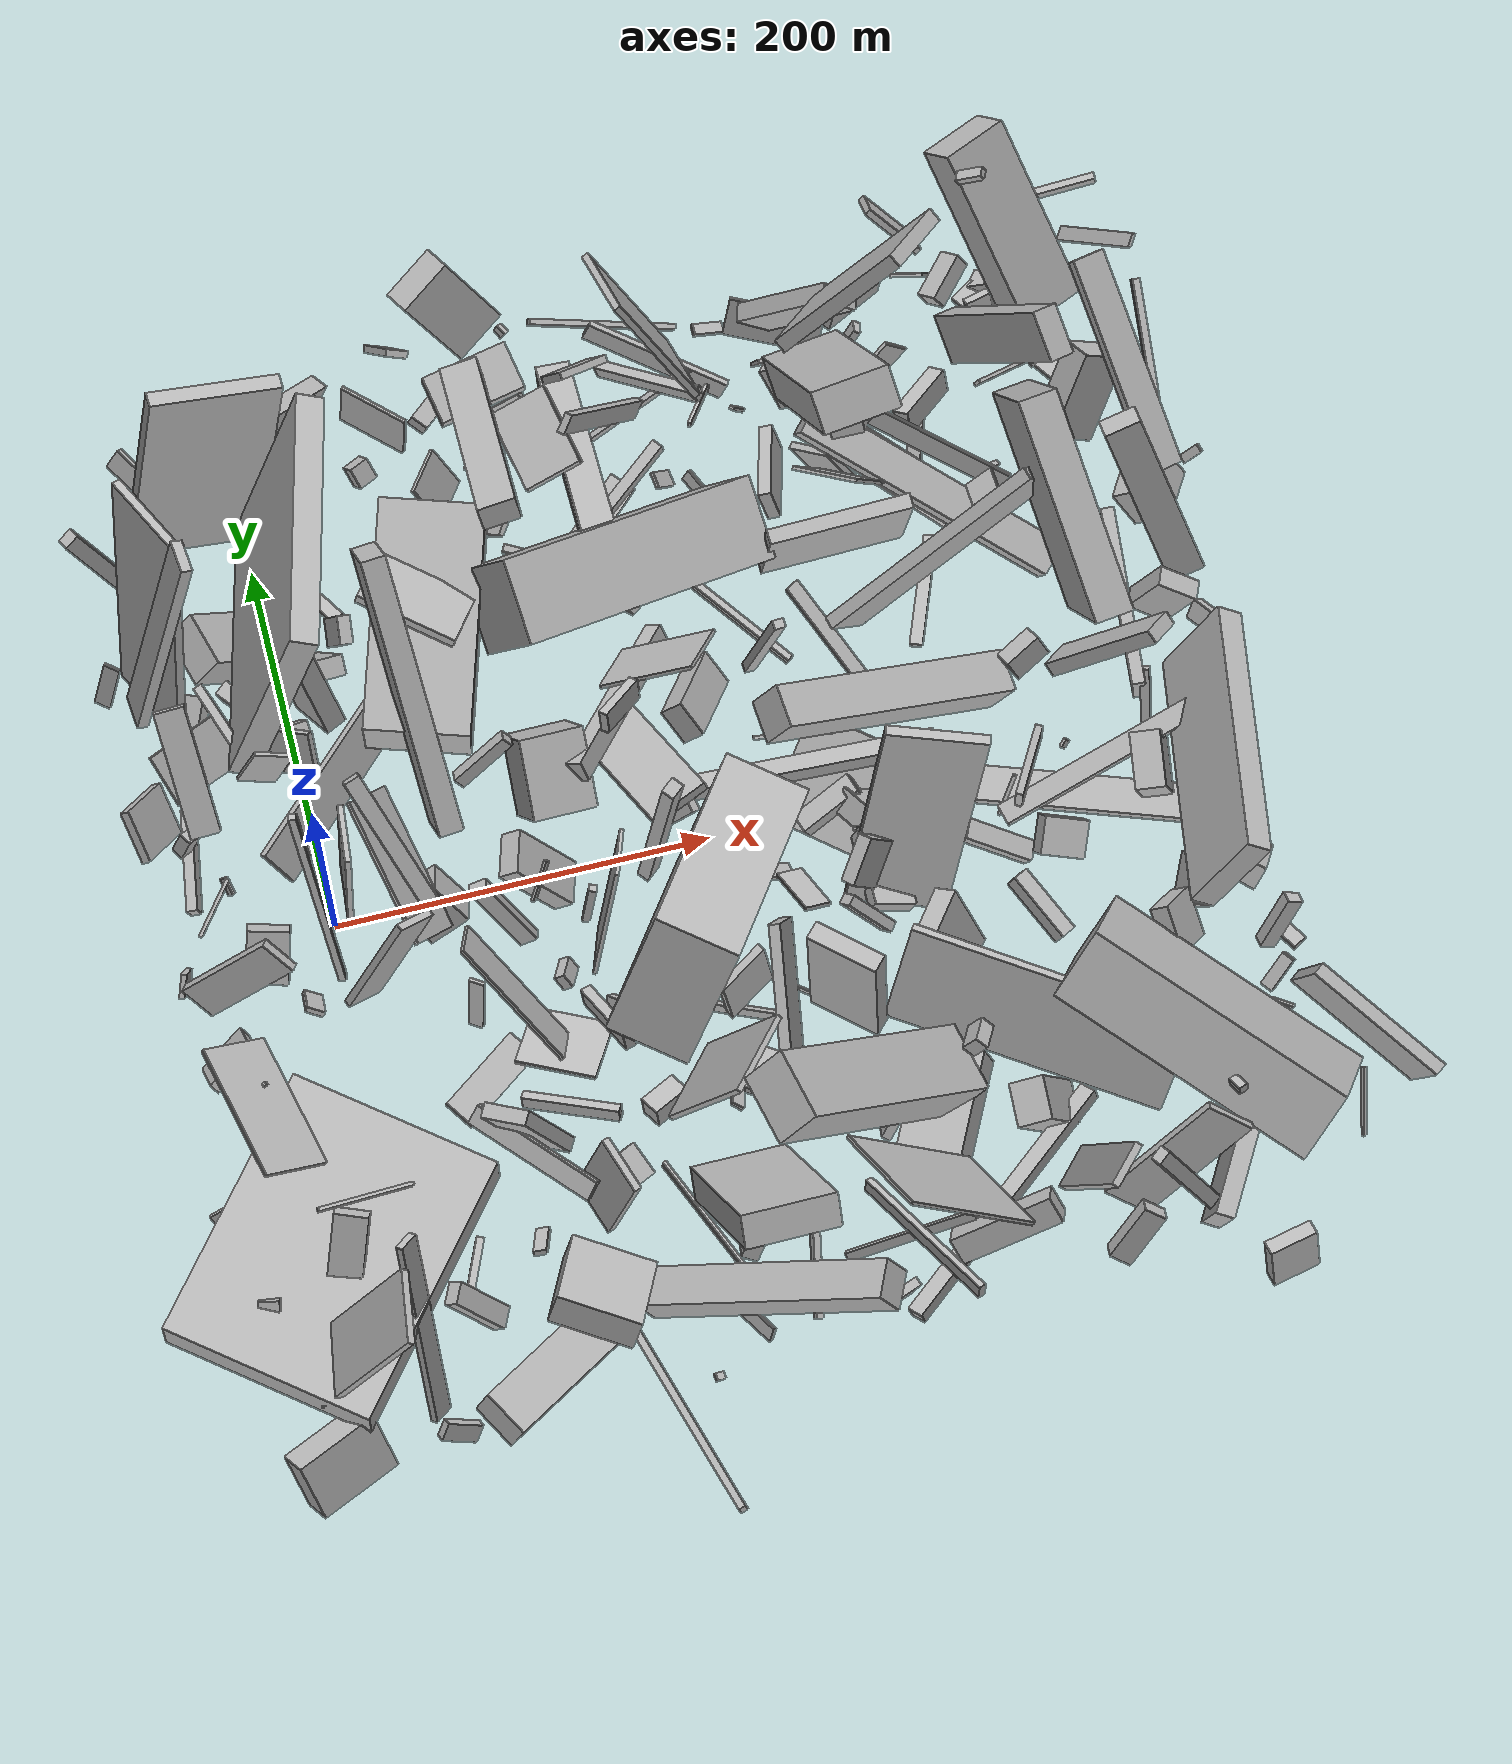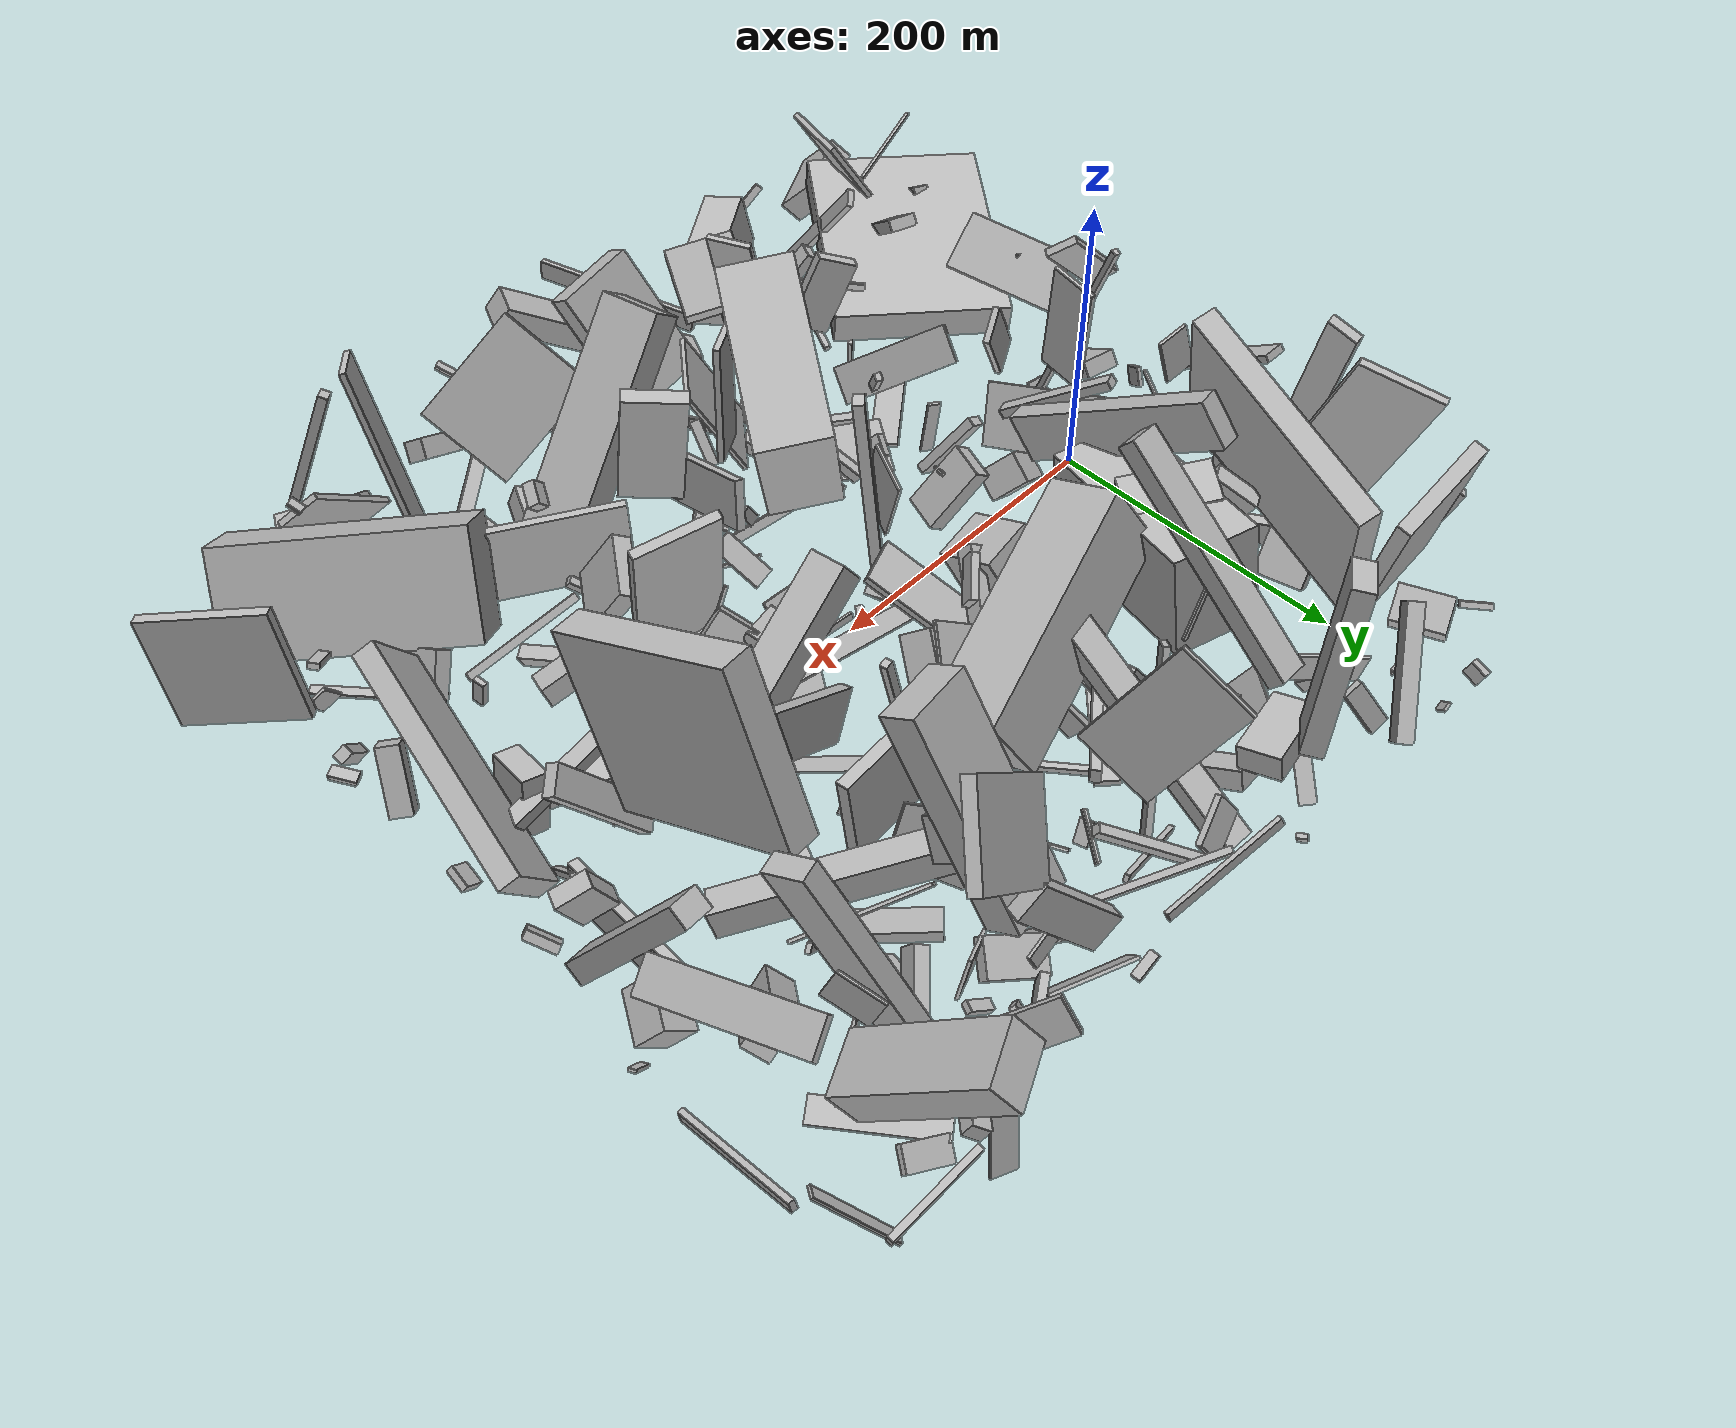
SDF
<sdf version="1.6">
 <world name="default">
  <scene>
   <sky><clouds><speed>12</speed></clouds></sky>
   <ambient>0.4 0.4 0.4 1</ambient>
   <background>0.7 0.7 0.7 1</background>
   <shadows>1</shadows>
  </scene>
  <gravity>0 0 -9.8066</gravity>
  <magnetic_field>6e-06 2.3e-05 -4.2e-05</magnetic_field>
  <physics default="0" name="default_physics" type="ode">
   <ode>
    <solver>
     <type>quick</type>
     <iters>10</iters>
     <sor>1.0</sor>
     <use_dynamic_moi_rescaling>0</use_dynamic_moi_rescaling>
    </solver>
    <constraints>
     <cfm>0</cfm>
     <erp>0.2</erp>
     <contact_max_correcting_vel>100</contact_max_correcting_vel>
     <contact_surface_layer>0.001</contact_surface_layer>
    </constraints>
   </ode>
   <max_step_size>0.004</max_step_size>
   <real_time_factor>1</real_time_factor>
   <real_time_update_rate>250</real_time_update_rate>
  </physics>
  <light name="sun" type="directional">
   <pose>0 0 10 0 0 0</pose>
   <diffuse>0.8 0.8 0.8 1</diffuse>
   <specular>0.2 0.2 0.2 1</specular>
   <attenuation>
    <range>1000</range>
    <constant>0.9</constant>
    <linear>0.01</linear>
    <quadratic>0.001</quadratic>
   </attenuation>
   <direction>-0.5 0.1 -0.9</direction>
  </light>
  <model name="building_1">
   <static>0</static>
   <pose>272.4165706536021 -54.26228623214429 72.06441700890518 -2.3123806209111533 0.9907104650469202 0.10993199374310866</pose>
   <link name="link">
    <gravity>0</gravity>
    <pose>0 0 4.0 0 0 0</pose>
    <collision name="collision"><geometry><box><size>22 26 8</size></box></geometry></collision>
    <visual name="visual">
     <cast_shadows>0</cast_shadows>
     <geometry><box><size>22 26 8</size></box></geometry>
     <material>
      <script>
       <uri>model://HANNAS_wall/materials/scripts</uri>
       <uri>model://HANNAS_wall/materials/textures</uri>
       <name>vrc/HANNAS_wall</name>
      </script>
     </material>
    </visual>
   </link>
  </model>
  <model name="building_2">
   <static>0</static>
   <pose>323.82430526786845 -47.18001517054745 79.09906799330403 -1.2248675999530452 -1.2489831980606851 0.9320766156826963</pose>
   <link name="link">
    <gravity>0</gravity>
    <pose>0 0 26.5 0 0 0</pose>
    <collision name="collision"><geometry><box><size>150 6 53</size></box></geometry></collision>
    <visual name="visual">
     <cast_shadows>0</cast_shadows>
     <geometry><box><size>150 6 53</size></box></geometry>
     <material>
      <script>
       <uri>model://HANNAS_wall/materials/scripts</uri>
       <uri>model://HANNAS_wall/materials/textures</uri>
       <name>vrc/HANNAS_wall</name>
      </script>
     </material>
    </visual>
   </link>
  </model>
  <model name="building_3">
   <static>0</static>
   <pose>5.835858461507819 -122.21662197756149 44.71238421912026 -0.4865778353604829 -1.474053561694862 1.3846577245615164</pose>
   <link name="link">
    <gravity>0</gravity>
    <pose>0 0 74.5 0 0 0</pose>
    <collision name="collision"><geometry><box><size>22 115 149</size></box></geometry></collision>
    <visual name="visual">
     <cast_shadows>0</cast_shadows>
     <geometry><box><size>22 115 149</size></box></geometry>
     <material>
      <script>
       <uri>model://HANNAS_wall/materials/scripts</uri>
       <uri>model://HANNAS_wall/materials/textures</uri>
       <name>vrc/HANNAS_wall</name>
      </script>
     </material>
    </visual>
   </link>
  </model>
  <model name="building_4">
   <static>0</static>
   <pose>-74.45677199136391 207.94244839956997 39.55125357585548 2.6483922736353818 -1.0286559498156338 2.5570631894765388</pose>
   <link name="link">
    <gravity>0</gravity>
    <pose>0 0 4.0 0 0 0</pose>
    <collision name="collision"><geometry><box><size>59 9 8</size></box></geometry></collision>
    <visual name="visual">
     <cast_shadows>0</cast_shadows>
     <geometry><box><size>59 9 8</size></box></geometry>
     <material>
      <script>
       <uri>model://HANNAS_wall/materials/scripts</uri>
       <uri>model://HANNAS_wall/materials/textures</uri>
       <name>vrc/HANNAS_wall</name>
      </script>
     </material>
    </visual>
   </link>
  </model>
  <model name="building_5">
   <static>0</static>
   <pose>65.79338038084802 15.389795078532417 80.16013095305803 -0.07329744564465657 -0.9631267049949173 -1.4160894481976734</pose>
   <link name="link">
    <gravity>0</gravity>
    <pose>0 0 75.0 0 0 0</pose>
    <collision name="collision"><geometry><box><size>31 13 150</size></box></geometry></collision>
    <visual name="visual">
     <cast_shadows>0</cast_shadows>
     <geometry><box><size>31 13 150</size></box></geometry>
     <material>
      <script>
       <uri>model://HANNAS_wall/materials/scripts</uri>
       <uri>model://HANNAS_wall/materials/textures</uri>
       <name>vrc/HANNAS_wall</name>
      </script>
     </material>
    </visual>
   </link>
  </model>
  <model name="building_6">
   <static>0</static>
   <pose>400.58906750568445 201.3353379388965 90.74872359586328 1.720728777278763 -0.4512644913367839 1.7328811887067521</pose>
   <link name="link">
    <gravity>0</gravity>
    <pose>0 0 6.5 0 0 0</pose>
    <collision name="collision"><geometry><box><size>27 150 13</size></box></geometry></collision>
    <visual name="visual">
     <cast_shadows>0</cast_shadows>
     <geometry><box><size>27 150 13</size></box></geometry>
     <material>
      <script>
       <uri>model://HANNAS_wall/materials/scripts</uri>
       <uri>model://HANNAS_wall/materials/textures</uri>
       <name>vrc/HANNAS_wall</name>
      </script>
     </material>
    </visual>
   </link>
  </model>
  <model name="building_7">
   <static>0</static>
   <pose>299.53094110872917 -233.97817949876355 25.650742074589843 1.98064890985388 -0.05651019234095352 -2.4577254015816905</pose>
   <link name="link">
    <gravity>0</gravity>
    <pose>0 0 4.5 0 0 0</pose>
    <collision name="collision"><geometry><box><size>150 7 9</size></box></geometry></collision>
    <visual name="visual">
     <cast_shadows>0</cast_shadows>
     <geometry><box><size>150 7 9</size></box></geometry>
     <material>
      <script>
       <uri>model://HANNAS_wall/materials/scripts</uri>
       <uri>model://HANNAS_wall/materials/textures</uri>
       <name>vrc/HANNAS_wall</name>
      </script>
     </material>
    </visual>
   </link>
  </model>
  <model name="building_8">
   <static>0</static>
   <pose>355.89411451288 -247.90377301242586 39.14202815098222 0.7057882572317773 0.44317083714370686 1.400607502678652</pose>
   <link name="link">
    <gravity>0</gravity>
    <pose>0 0 40.0 0 0 0</pose>
    <collision name="collision"><geometry><box><size>4 29 80</size></box></geometry></collision>
    <visual name="visual">
     <cast_shadows>0</cast_shadows>
     <geometry><box><size>4 29 80</size></box></geometry>
     <material>
      <script>
       <uri>model://HANNAS_wall/materials/scripts</uri>
       <uri>model://HANNAS_wall/materials/textures</uri>
       <name>vrc/HANNAS_wall</name>
      </script>
     </material>
    </visual>
   </link>
  </model>
  <model name="building_9">
   <static>0</static>
   <pose>17.978054973880703 104.83433261570043 32.83372752502623 0.5673115611624566 -0.05000095545751157 -2.685992951471049</pose>
   <link name="link">
    <gravity>0</gravity>
    <pose>0 0 24.0 0 0 0</pose>
    <collision name="collision"><geometry><box><size>12 31 48</size></box></geometry></collision>
    <visual name="visual">
     <cast_shadows>0</cast_shadows>
     <geometry><box><size>12 31 48</size></box></geometry>
     <material>
      <script>
       <uri>model://HANNAS_wall/materials/scripts</uri>
       <uri>model://HANNAS_wall/materials/textures</uri>
       <name>vrc/HANNAS_wall</name>
      </script>
     </material>
    </visual>
   </link>
  </model>
  <model name="building_10">
   <static>0</static>
   <pose>185.29424632737118 105.88076898427 84.4069443974222 1.178355297755103 -0.36533796081959596 -2.90046888446741</pose>
   <link name="link">
    <gravity>0</gravity>
    <pose>0 0 22.5 0 0 0</pose>
    <collision name="collision"><geometry><box><size>150 50 45</size></box></geometry></collision>
    <visual name="visual">
     <cast_shadows>0</cast_shadows>
     <geometry><box><size>150 50 45</size></box></geometry>
     <material>
      <script>
       <uri>model://HANNAS_wall/materials/scripts</uri>
       <uri>model://HANNAS_wall/materials/textures</uri>
       <name>vrc/HANNAS_wall</name>
      </script>
     </material>
    </visual>
   </link>
  </model>
  <model name="building_11">
   <static>0</static>
   <pose>272.50435108659383 -107.83186278597427 57.48532631388605 1.627277002997505 0.29188521207869556 1.013217597711566</pose>
   <link name="link">
    <gravity>0</gravity>
    <pose>0 0 75.0 0 0 0</pose>
    <collision name="collision"><geometry><box><size>4 86 150</size></box></geometry></collision>
    <visual name="visual">
     <cast_shadows>0</cast_shadows>
     <geometry><box><size>4 86 150</size></box></geometry>
     <material>
      <script>
       <uri>model://HANNAS_wall/materials/scripts</uri>
       <uri>model://HANNAS_wall/materials/textures</uri>
       <name>vrc/HANNAS_wall</name>
      </script>
     </material>
    </visual>
   </link>
  </model>
  <model name="building_12">
   <static>0</static>
   <pose>-67.1942225786789 55.6574327919041 34.76636416632705 1.638907363905264 -1.002846880795218 0.5183612143883055</pose>
   <link name="link">
    <gravity>0</gravity>
    <pose>0 0 3.5 0 0 0</pose>
    <collision name="collision"><geometry><box><size>13 9 7</size></box></geometry></collision>
    <visual name="visual">
     <cast_shadows>0</cast_shadows>
     <geometry><box><size>13 9 7</size></box></geometry>
     <material>
      <script>
       <uri>model://HANNAS_wall/materials/scripts</uri>
       <uri>model://HANNAS_wall/materials/textures</uri>
       <name>vrc/HANNAS_wall</name>
      </script>
     </material>
    </visual>
   </link>
  </model>
  <model name="building_13">
   <static>0</static>
   <pose>404.9555528926048 105.27259282947267 109.17483107461244 0.40766137444998574 -0.06404478932884705 0.10300423446091946</pose>
   <link name="link">
    <gravity>0</gravity>
    <pose>0 0 55.0 0 0 0</pose>
    <collision name="collision"><geometry><box><size>20 117 110</size></box></geometry></collision>
    <visual name="visual">
     <cast_shadows>0</cast_shadows>
     <geometry><box><size>20 117 110</size></box></geometry>
     <material>
      <script>
       <uri>model://HANNAS_wall/materials/scripts</uri>
       <uri>model://HANNAS_wall/materials/textures</uri>
       <name>vrc/HANNAS_wall</name>
      </script>
     </material>
    </visual>
   </link>
  </model>
  <model name="building_14">
   <static>0</static>
   <pose>402.9279213064581 -189.28894554053488 61.9914713612671 0.9855820688995628 -0.1330575160869668 2.329380423470177</pose>
   <link name="link">
    <gravity>0</gravity>
    <pose>0 0 20.0 0 0 0</pose>
    <collision name="collision"><geometry><box><size>150 68 40</size></box></geometry></collision>
    <visual name="visual">
     <cast_shadows>0</cast_shadows>
     <geometry><box><size>150 68 40</size></box></geometry>
     <material>
      <script>
       <uri>model://HANNAS_wall/materials/scripts</uri>
       <uri>model://HANNAS_wall/materials/textures</uri>
       <name>vrc/HANNAS_wall</name>
      </script>
     </material>
    </visual>
   </link>
  </model>
  <model name="building_15">
   <static>0</static>
   <pose>168.70893720154496 -190.80330866939033 55.37333430799978 -0.20980299649126538 0.5808129253188291 -1.6435773203934128</pose>
   <link name="link">
    <gravity>0</gravity>
    <pose>0 0 42.5 0 0 0</pose>
    <collision name="collision"><geometry><box><size>18 51 85</size></box></geometry></collision>
    <visual name="visual">
     <cast_shadows>0</cast_shadows>
     <geometry><box><size>18 51 85</size></box></geometry>
     <material>
      <script>
       <uri>model://HANNAS_wall/materials/scripts</uri>
       <uri>model://HANNAS_wall/materials/textures</uri>
       <name>vrc/HANNAS_wall</name>
      </script>
     </material>
    </visual>
   </link>
  </model>
  <model name="building_16">
   <static>0</static>
   <pose>172.4480563789559 -256.06530838762717 52.13919398344124 -0.10142437449352978 -0.6048599510881316 -0.36942929497885785</pose>
   <link name="link">
    <gravity>0</gravity>
    <pose>0 0 9.0 0 0 0</pose>
    <collision name="collision"><geometry><box><size>150 21 18</size></box></geometry></collision>
    <visual name="visual">
     <cast_shadows>0</cast_shadows>
     <geometry><box><size>150 21 18</size></box></geometry>
     <material>
      <script>
       <uri>model://HANNAS_wall/materials/scripts</uri>
       <uri>model://HANNAS_wall/materials/textures</uri>
       <name>vrc/HANNAS_wall</name>
      </script>
     </material>
    </visual>
   </link>
  </model>
  <model name="building_17">
   <static>0</static>
   <pose>333.928652176697 247.26571172892753 14.19385974856086 -2.2846399041964043 0.8644635436970637 -2.609018774751286</pose>
   <link name="link">
    <gravity>0</gravity>
    <pose>0 0 2.0 0 0 0</pose>
    <collision name="collision"><geometry><box><size>23 9 4</size></box></geometry></collision>
    <visual name="visual">
     <cast_shadows>0</cast_shadows>
     <geometry><box><size>23 9 4</size></box></geometry>
     <material>
      <script>
       <uri>model://HANNAS_wall/materials/scripts</uri>
       <uri>model://HANNAS_wall/materials/textures</uri>
       <name>vrc/HANNAS_wall</name>
      </script>
     </material>
    </visual>
   </link>
  </model>
  <model name="building_18">
   <static>0</static>
   <pose>172.58470879514888 73.79339232438144 30.630355834477015 2.157927794069207 -0.4387624092834741 -2.2294605914760046</pose>
   <link name="link">
    <gravity>0</gravity>
    <pose>0 0 4.5 0 0 0</pose>
    <collision name="collision"><geometry><box><size>110 12 9</size></box></geometry></collision>
    <visual name="visual">
     <cast_shadows>0</cast_shadows>
     <geometry><box><size>110 12 9</size></box></geometry>
     <material>
      <script>
       <uri>model://HANNAS_wall/materials/scripts</uri>
       <uri>model://HANNAS_wall/materials/textures</uri>
       <name>vrc/HANNAS_wall</name>
      </script>
     </material>
    </visual>
   </link>
  </model>
  <model name="building_19">
   <static>0</static>
   <pose>452.56117804282997 103.3349897625175 68.48537059684166 1.241224443477612 -0.9259921665959768 1.9693480970314834</pose>
   <link name="link">
    <gravity>0</gravity>
    <pose>0 0 10.0 0 0 0</pose>
    <collision name="collision"><geometry><box><size>104 14 20</size></box></geometry></collision>
    <visual name="visual">
     <cast_shadows>0</cast_shadows>
     <geometry><box><size>104 14 20</size></box></geometry>
     <material>
      <script>
       <uri>model://HANNAS_wall/materials/scripts</uri>
       <uri>model://HANNAS_wall/materials/textures</uri>
       <name>vrc/HANNAS_wall</name>
      </script>
     </material>
    </visual>
   </link>
  </model>
  <model name="building_20">
   <static>0</static>
   <pose>80.07979476006882 127.824510955347 47.10469755456855 -0.040824752026687484 0.16423273041170286 -1.8767921694358836</pose>
   <link name="link">
    <gravity>0</gravity>
    <pose>0 0 33.5 0 0 0</pose>
    <collision name="collision"><geometry><box><size>120 55 67</size></box></geometry></collision>
    <visual name="visual">
     <cast_shadows>0</cast_shadows>
     <geometry><box><size>120 55 67</size></box></geometry>
     <material>
      <script>
       <uri>model://HANNAS_wall/materials/scripts</uri>
       <uri>model://HANNAS_wall/materials/textures</uri>
       <name>vrc/HANNAS_wall</name>
      </script>
     </material>
    </visual>
   </link>
  </model>
  <model name="building_21">
   <static>0</static>
   <pose>249.59623431545262 -248.5707191138502 57.13827346581637 -0.3957613719345959 -0.41837577906019463 -1.1019933557663533</pose>
   <link name="link">
    <gravity>0</gravity>
    <pose>0 0 3.5 0 0 0</pose>
    <collision name="collision"><geometry><box><size>93 4 7</size></box></geometry></collision>
    <visual name="visual">
     <cast_shadows>0</cast_shadows>
     <geometry><box><size>93 4 7</size></box></geometry>
     <material>
      <script>
       <uri>model://HANNAS_wall/materials/scripts</uri>
       <uri>model://HANNAS_wall/materials/textures</uri>
       <name>vrc/HANNAS_wall</name>
      </script>
     </material>
    </visual>
   </link>
  </model>
  <model name="building_22">
   <static>0</static>
   <pose>330.1755720479846 -175.32609087321197 28.923262978509513 -1.8119866910495497 -1.131948626585235 -2.9596748544789415</pose>
   <link name="link">
    <gravity>0</gravity>
    <pose>0 0 11.5 0 0 0</pose>
    <collision name="collision"><geometry><box><size>42 19 23</size></box></geometry></collision>
    <visual name="visual">
     <cast_shadows>0</cast_shadows>
     <geometry><box><size>42 19 23</size></box></geometry>
     <material>
      <script>
       <uri>model://HANNAS_wall/materials/scripts</uri>
       <uri>model://HANNAS_wall/materials/textures</uri>
       <name>vrc/HANNAS_wall</name>
      </script>
     </material>
    </visual>
   </link>
  </model>
  <model name="building_23">
   <static>0</static>
   <pose>214.20025725259177 69.2321899512581 28.982133728075425 2.36427097274623 0.5834643408096105 -1.0614553253820256</pose>
   <link name="link">
    <gravity>0</gravity>
    <pose>0 0 6.5 0 0 0</pose>
    <collision name="collision"><geometry><box><size>21 50 13</size></box></geometry></collision>
    <visual name="visual">
     <cast_shadows>0</cast_shadows>
     <geometry><box><size>21 50 13</size></box></geometry>
     <material>
      <script>
       <uri>model://HANNAS_wall/materials/scripts</uri>
       <uri>model://HANNAS_wall/materials/textures</uri>
       <name>vrc/HANNAS_wall</name>
      </script>
     </material>
    </visual>
   </link>
  </model>
  <model name="building_24">
   <static>0</static>
   <pose>127.57483943052326 185.06371061172996 142.8643766640172 0.1416816433321335 -0.6985751615197036 -1.5987708633046258</pose>
   <link name="link">
    <gravity>0</gravity>
    <pose>0 0 6.0 0 0 0</pose>
    <collision name="collision"><geometry><box><size>150 20 12</size></box></geometry></collision>
    <visual name="visual">
     <cast_shadows>0</cast_shadows>
     <geometry><box><size>150 20 12</size></box></geometry>
     <material>
      <script>
       <uri>model://HANNAS_wall/materials/scripts</uri>
       <uri>model://HANNAS_wall/materials/textures</uri>
       <name>vrc/HANNAS_wall</name>
      </script>
     </material>
    </visual>
   </link>
  </model>
  <model name="building_25">
   <static>0</static>
   <pose>29.72997030836655 131.8980565701181 28.449520393849937 1.0426460473876165 -1.0751715418193473 -0.9791223638475639</pose>
   <link name="link">
    <gravity>0</gravity>
    <pose>0 0 9.0 0 0 0</pose>
    <collision name="collision"><geometry><box><size>41 11 18</size></box></geometry></collision>
    <visual name="visual">
     <cast_shadows>0</cast_shadows>
     <geometry><box><size>41 11 18</size></box></geometry>
     <material>
      <script>
       <uri>model://HANNAS_wall/materials/scripts</uri>
       <uri>model://HANNAS_wall/materials/textures</uri>
       <name>vrc/HANNAS_wall</name>
      </script>
     </material>
    </visual>
   </link>
  </model>
  <model name="building_26">
   <static>0</static>
   <pose>432.68558480805416 -86.23474516821247 22.97421442148746 -2.510820552903777 -1.2029055401955706 -1.035763901945189</pose>
   <link name="link">
    <gravity>0</gravity>
    <pose>0 0 5.0 0 0 0</pose>
    <collision name="collision"><geometry><box><size>33 28 10</size></box></geometry></collision>
    <visual name="visual">
     <cast_shadows>0</cast_shadows>
     <geometry><box><size>33 28 10</size></box></geometry>
     <material>
      <script>
       <uri>model://HANNAS_wall/materials/scripts</uri>
       <uri>model://HANNAS_wall/materials/textures</uri>
       <name>vrc/HANNAS_wall</name>
      </script>
     </material>
    </visual>
   </link>
  </model>
  <model name="building_27">
   <static>0</static>
   <pose>132.2567938228932 -82.57854683447687 13.670138133554069 0.829152997326332 0.5826017921094884 -1.844322049395809</pose>
   <link name="link">
    <gravity>0</gravity>
    <pose>0 0 2.5 0 0 0</pose>
    <collision name="collision"><geometry><box><size>15 11 5</size></box></geometry></collision>
    <visual name="visual">
     <cast_shadows>0</cast_shadows>
     <geometry><box><size>15 11 5</size></box></geometry>
     <material>
      <script>
       <uri>model://HANNAS_wall/materials/scripts</uri>
       <uri>model://HANNAS_wall/materials/textures</uri>
       <name>vrc/HANNAS_wall</name>
      </script>
     </material>
    </visual>
   </link>
  </model>
  <model name="building_28">
   <static>0</static>
   <pose>-15.430822300728103 158.05438500108716 29.199407450141297 2.2954427736452394 -0.0484061388359062 -1.2956543786922599</pose>
   <link name="link">
    <gravity>0</gravity>
    <pose>0 0 10.0 0 0 0</pose>
    <collision name="collision"><geometry><box><size>31 51 20</size></box></geometry></collision>
    <visual name="visual">
     <cast_shadows>0</cast_shadows>
     <geometry><box><size>31 51 20</size></box></geometry>
     <material>
      <script>
       <uri>model://HANNAS_wall/materials/scripts</uri>
       <uri>model://HANNAS_wall/materials/textures</uri>
       <name>vrc/HANNAS_wall</name>
      </script>
     </material>
    </visual>
   </link>
  </model>
  <model name="building_29">
   <static>0</static>
   <pose>378.1255114581803 270.80634514704843 66.35772896245645 0.6940584296487194 -0.8190794882800703 -1.5986323340027746</pose>
   <link name="link">
    <gravity>0</gravity>
    <pose>0 0 18.0 0 0 0</pose>
    <collision name="collision"><geometry><box><size>22 4 36</size></box></geometry></collision>
    <visual name="visual">
     <cast_shadows>0</cast_shadows>
     <geometry><box><size>22 4 36</size></box></geometry>
     <material>
      <script>
       <uri>model://HANNAS_wall/materials/scripts</uri>
       <uri>model://HANNAS_wall/materials/textures</uri>
       <name>vrc/HANNAS_wall</name>
      </script>
     </material>
    </visual>
   </link>
  </model>
  <model name="building_30">
   <static>0</static>
   <pose>445.4106323668765 -288.4377560115181 20.085211243128448 -1.5691695710257498 0.26708528053410757 1.7794913127640006</pose>
   <link name="link">
    <gravity>0</gravity>
    <pose>0 0 13.0 0 0 0</pose>
    <collision name="collision"><geometry><box><size>8 35 26</size></box></geometry></collision>
    <visual name="visual">
     <cast_shadows>0</cast_shadows>
     <geometry><box><size>8 35 26</size></box></geometry>
     <material>
      <script>
       <uri>model://HANNAS_wall/materials/scripts</uri>
       <uri>model://HANNAS_wall/materials/textures</uri>
       <name>vrc/HANNAS_wall</name>
      </script>
     </material>
    </visual>
   </link>
  </model>
  <model name="building_31">
   <static>0</static>
   <pose>436.0858934883784 226.75639786986216 52.35880131767577 0.863082404299195 -0.13612266646796062 -2.7027658244045902</pose>
   <link name="link">
    <gravity>0</gravity>
    <pose>0 0 52.5 0 0 0</pose>
    <collision name="collision"><geometry><box><size>37 24 105</size></box></geometry></collision>
    <visual name="visual">
     <cast_shadows>0</cast_shadows>
     <geometry><box><size>37 24 105</size></box></geometry>
     <material>
      <script>
       <uri>model://HANNAS_wall/materials/scripts</uri>
       <uri>model://HANNAS_wall/materials/textures</uri>
       <name>vrc/HANNAS_wall</name>
      </script>
     </material>
    </visual>
   </link>
  </model>
  <model name="building_32">
   <static>0</static>
   <pose>463.0518144538313 -42.21308406015045 66.90314749070225 1.0424813106014168 -0.3172337795324884 -1.7528937747881097</pose>
   <link name="link">
    <gravity>0</gravity>
    <pose>0 0 7.0 0 0 0</pose>
    <collision name="collision"><geometry><box><size>150 54 14</size></box></geometry></collision>
    <visual name="visual">
     <cast_shadows>0</cast_shadows>
     <geometry><box><size>150 54 14</size></box></geometry>
     <material>
      <script>
       <uri>model://HANNAS_wall/materials/scripts</uri>
       <uri>model://HANNAS_wall/materials/textures</uri>
       <name>vrc/HANNAS_wall</name>
      </script>
     </material>
    </visual>
   </link>
  </model>
  <model name="building_33">
   <static>0</static>
   <pose>200.41568147362213 192.89896609704041 27.644120616083498 1.6161998158145225 -1.4615504879100272 -0.8577555704498472</pose>
   <link name="link">
    <gravity>0</gravity>
    <pose>0 0 32.5 0 0 0</pose>
    <collision name="collision"><geometry><box><size>4 15 65</size></box></geometry></collision>
    <visual name="visual">
     <cast_shadows>0</cast_shadows>
     <geometry><box><size>4 15 65</size></box></geometry>
     <material>
      <script>
       <uri>model://HANNAS_wall/materials/scripts</uri>
       <uri>model://HANNAS_wall/materials/textures</uri>
       <name>vrc/HANNAS_wall</name>
      </script>
     </material>
    </visual>
   </link>
  </model>
  <model name="building_34">
   <static>0</static>
   <pose>164.1462934367311 -87.00258705766674 91.69687753364849 0.14673647543493426 0.40451893321257865 0.9899473387207495</pose>
   <link name="link">
    <gravity>0</gravity>
    <pose>0 0 48.5 0 0 0</pose>
    <collision name="collision"><geometry><box><size>114 45 97</size></box></geometry></collision>
    <visual name="visual">
     <cast_shadows>0</cast_shadows>
     <geometry><box><size>114 45 97</size></box></geometry>
     <material>
      <script>
       <uri>model://HANNAS_wall/materials/scripts</uri>
       <uri>model://HANNAS_wall/materials/textures</uri>
       <name>vrc/HANNAS_wall</name>
      </script>
     </material>
    </visual>
   </link>
  </model>
  <model name="building_35">
   <static>0</static>
   <pose>290.3912804903219 187.12471028104437 114.11389787698812 1.561164324346291 -0.5289422882370757 1.7015595074946457</pose>
   <link name="link">
    <gravity>0</gravity>
    <pose>0 0 21.0 0 0 0</pose>
    <collision name="collision"><geometry><box><size>23 137 42</size></box></geometry></collision>
    <visual name="visual">
     <cast_shadows>0</cast_shadows>
     <geometry><box><size>23 137 42</size></box></geometry>
     <material>
      <script>
       <uri>model://HANNAS_wall/materials/scripts</uri>
       <uri>model://HANNAS_wall/materials/textures</uri>
       <name>vrc/HANNAS_wall</name>
      </script>
     </material>
    </visual>
   </link>
  </model>
  <model name="building_36">
   <static>0</static>
   <pose>300.21555406296636 44.38534926954047 67.16677585907131 -1.641209844108178 -0.5704789458199622 -3.01159917272137</pose>
   <link name="link">
    <gravity>0</gravity>
    <pose>0 0 11.5 0 0 0</pose>
    <collision name="collision"><geometry><box><size>150 23 23</size></box></geometry></collision>
    <visual name="visual">
     <cast_shadows>0</cast_shadows>
     <geometry><box><size>150 23 23</size></box></geometry>
     <material>
      <script>
       <uri>model://HANNAS_wall/materials/scripts</uri>
       <uri>model://HANNAS_wall/materials/textures</uri>
       <name>vrc/HANNAS_wall</name>
      </script>
     </material>
    </visual>
   </link>
  </model>
  <model name="building_37">
   <static>0</static>
   <pose>166.95054671278797 -17.908595503135512 85.73106465991597 1.6184008188012624 -0.08403401055581426 2.273886820849268</pose>
   <link name="link">
    <gravity>0</gravity>
    <pose>0 0 4.5 0 0 0</pose>
    <collision name="collision"><geometry><box><size>7 150 9</size></box></geometry></collision>
    <visual name="visual">
     <cast_shadows>0</cast_shadows>
     <geometry><box><size>7 150 9</size></box></geometry>
     <material>
      <script>
       <uri>model://HANNAS_wall/materials/scripts</uri>
       <uri>model://HANNAS_wall/materials/textures</uri>
       <name>vrc/HANNAS_wall</name>
      </script>
     </material>
    </visual>
   </link>
  </model>
  <model name="building_38">
   <static>0</static>
   <pose>248.59608517578522 20.025460723789642 31.408909467554523 2.647425657725896 -0.12892269191884337 -0.08147044329171586</pose>
   <link name="link">
    <gravity>0</gravity>
    <pose>0 0 3.5 0 0 0</pose>
    <collision name="collision"><geometry><box><size>150 12 7</size></box></geometry></collision>
    <visual name="visual">
     <cast_shadows>0</cast_shadows>
     <geometry><box><size>150 12 7</size></box></geometry>
     <material>
      <script>
       <uri>model://HANNAS_wall/materials/scripts</uri>
       <uri>model://HANNAS_wall/materials/textures</uri>
       <name>vrc/HANNAS_wall</name>
      </script>
     </material>
    </visual>
   </link>
  </model>
  <model name="building_39">
   <static>0</static>
   <pose>429.8933502145881 160.04105392337613 40.926628430205234 0.6483564356068493 -0.6909892722969965 -3.1372712939364686</pose>
   <link name="link">
    <gravity>0</gravity>
    <pose>0 0 24.5 0 0 0</pose>
    <collision name="collision"><geometry><box><size>28 17 49</size></box></geometry></collision>
    <visual name="visual">
     <cast_shadows>0</cast_shadows>
     <geometry><box><size>28 17 49</size></box></geometry>
     <material>
      <script>
       <uri>model://HANNAS_wall/materials/scripts</uri>
       <uri>model://HANNAS_wall/materials/textures</uri>
       <name>vrc/HANNAS_wall</name>
      </script>
     </material>
    </visual>
   </link>
  </model>
  <model name="building_40">
   <static>0</static>
   <pose>61.7476811791285 -3.8057593474671014 27.311445873402633 2.3194962549879037 0.7091316333260866 -0.8224988985748612</pose>
   <link name="link">
    <gravity>0</gravity>
    <pose>0 0 12.5 0 0 0</pose>
    <collision name="collision"><geometry><box><size>27 20 25</size></box></geometry></collision>
    <visual name="visual">
     <cast_shadows>0</cast_shadows>
     <geometry><box><size>27 20 25</size></box></geometry>
     <material>
      <script>
       <uri>model://HANNAS_wall/materials/scripts</uri>
       <uri>model://HANNAS_wall/materials/textures</uri>
       <name>vrc/HANNAS_wall</name>
      </script>
     </material>
    </visual>
   </link>
  </model>
  <model name="building_41">
   <static>0</static>
   <pose>16.866909825559862 150.28984347591364 106.71477533509268 -0.70087341347727 -1.176562851867607 0.4341626629790535</pose>
   <link name="link">
    <gravity>0</gravity>
    <pose>0 0 7.5 0 0 0</pose>
    <collision name="collision"><geometry><box><size>128 150 15</size></box></geometry></collision>
    <visual name="visual">
     <cast_shadows>0</cast_shadows>
     <geometry><box><size>128 150 15</size></box></geometry>
     <material>
      <script>
       <uri>model://HANNAS_wall/materials/scripts</uri>
       <uri>model://HANNAS_wall/materials/textures</uri>
       <name>vrc/HANNAS_wall</name>
      </script>
     </material>
    </visual>
   </link>
  </model>
  <model name="building_42">
   <static>0</static>
   <pose>44.557624142193085 -137.68530981630192 90.19917211873633 1.4890378663278445 -0.5933160094880301 0.7728392749617885</pose>
   <link name="link">
    <gravity>0</gravity>
    <pose>0 0 36.5 0 0 0</pose>
    <collision name="collision"><geometry><box><size>11 4 73</size></box></geometry></collision>
    <visual name="visual">
     <cast_shadows>0</cast_shadows>
     <geometry><box><size>11 4 73</size></box></geometry>
     <material>
      <script>
       <uri>model://HANNAS_wall/materials/scripts</uri>
       <uri>model://HANNAS_wall/materials/textures</uri>
       <name>vrc/HANNAS_wall</name>
      </script>
     </material>
    </visual>
   </link>
  </model>
  <model name="building_43">
   <static>0</static>
   <pose>296.0174654424926 128.0221410166297 36.9947980773058 0.09256489169194941 0.05724867130260059 0.042920246653902726</pose>
   <link name="link">
    <gravity>0</gravity>
    <pose>0 0 29.0 0 0 0</pose>
    <collision name="collision"><geometry><box><size>77 8 58</size></box></geometry></collision>
    <visual name="visual">
     <cast_shadows>0</cast_shadows>
     <geometry><box><size>77 8 58</size></box></geometry>
     <material>
      <script>
       <uri>model://HANNAS_wall/materials/scripts</uri>
       <uri>model://HANNAS_wall/materials/textures</uri>
       <name>vrc/HANNAS_wall</name>
      </script>
     </material>
    </visual>
   </link>
  </model>
  <model name="building_44">
   <static>0</static>
   <pose>125.6374754572452 -50.624787801604384 115.42600439560675 0.24975198675539606 -1.00457783113855 0.9896721516190242</pose>
   <link name="link">
    <gravity>0</gravity>
    <pose>0 0 2.5 0 0 0</pose>
    <collision name="collision"><geometry><box><size>21 4 5</size></box></geometry></collision>
    <visual name="visual">
     <cast_shadows>0</cast_shadows>
     <geometry><box><size>21 4 5</size></box></geometry>
     <material>
      <script>
       <uri>model://HANNAS_wall/materials/scripts</uri>
       <uri>model://HANNAS_wall/materials/textures</uri>
       <name>vrc/HANNAS_wall</name>
      </script>
     </material>
    </visual>
   </link>
  </model>
  <model name="building_45">
   <static>0</static>
   <pose>-22.747495784544853 27.307556544061146 36.744086166199914 1.511279796984068 -0.8784675674803873 2.382704882822578</pose>
   <link name="link">
    <gravity>0</gravity>
    <pose>0 0 75.0 0 0 0</pose>
    <collision name="collision"><geometry><box><size>25 4 150</size></box></geometry></collision>
    <visual name="visual">
     <cast_shadows>0</cast_shadows>
     <geometry><box><size>25 4 150</size></box></geometry>
     <material>
      <script>
       <uri>model://HANNAS_wall/materials/scripts</uri>
       <uri>model://HANNAS_wall/materials/textures</uri>
       <name>vrc/HANNAS_wall</name>
      </script>
     </material>
    </visual>
   </link>
  </model>
  <model name="building_46">
   <static>0</static>
   <pose>246.1859006012444 82.27732094601211 42.49364978558728 -2.5969373498946213 -1.377409207437211 -0.46187814407301775</pose>
   <link name="link">
    <gravity>0</gravity>
    <pose>0 0 3.0 0 0 0</pose>
    <collision name="collision"><geometry><box><size>82 5 6</size></box></geometry></collision>
    <visual name="visual">
     <cast_shadows>0</cast_shadows>
     <geometry><box><size>82 5 6</size></box></geometry>
     <material>
      <script>
       <uri>model://HANNAS_wall/materials/scripts</uri>
       <uri>model://HANNAS_wall/materials/textures</uri>
       <name>vrc/HANNAS_wall</name>
      </script>
     </material>
    </visual>
   </link>
  </model>
  <model name="building_47">
   <static>0</static>
   <pose>122.16583384751591 50.57232487508045 27.007879287932735 0.48537081636371293 0.21591489810907308 0.07180935491673637</pose>
   <link name="link">
    <gravity>0</gravity>
    <pose>0 0 15.0 0 0 0</pose>
    <collision name="collision"><geometry><box><size>35 43 30</size></box></geometry></collision>
    <visual name="visual">
     <cast_shadows>0</cast_shadows>
     <geometry><box><size>35 43 30</size></box></geometry>
     <material>
      <script>
       <uri>model://HANNAS_wall/materials/scripts</uri>
       <uri>model://HANNAS_wall/materials/textures</uri>
       <name>vrc/HANNAS_wall</name>
      </script>
     </material>
    </visual>
   </link>
  </model>
  <model name="building_48">
   <static>0</static>
   <pose>181.15345760904563 136.98491753784737 28.02272493933745 1.7195432955729344 -0.8248104269505879 -1.059218893279828</pose>
   <link name="link">
    <gravity>0</gravity>
    <pose>0 0 3.0 0 0 0</pose>
    <collision name="collision"><geometry><box><size>48 14 6</size></box></geometry></collision>
    <visual name="visual">
     <cast_shadows>0</cast_shadows>
     <geometry><box><size>48 14 6</size></box></geometry>
     <material>
      <script>
       <uri>model://HANNAS_wall/materials/scripts</uri>
       <uri>model://HANNAS_wall/materials/textures</uri>
       <name>vrc/HANNAS_wall</name>
      </script>
     </material>
    </visual>
   </link>
  </model>
  <model name="building_49">
   <static>0</static>
   <pose>22.213456180696234 231.83362541899422 81.35205831934411 1.334955823161173 -0.2483829394416432 -1.5135354277932942</pose>
   <link name="link">
    <gravity>0</gravity>
    <pose>0 0 35.0 0 0 0</pose>
    <collision name="collision"><geometry><box><size>9 128 70</size></box></geometry></collision>
    <visual name="visual">
     <cast_shadows>0</cast_shadows>
     <geometry><box><size>9 128 70</size></box></geometry>
     <material>
      <script>
       <uri>model://HANNAS_wall/materials/scripts</uri>
       <uri>model://HANNAS_wall/materials/textures</uri>
       <name>vrc/HANNAS_wall</name>
      </script>
     </material>
    </visual>
   </link>
  </model>
  <model name="building_50">
   <static>0</static>
   <pose>266.8485876791395 -201.04726991455078 22.487208587755237 -1.6423376085944326 -0.3676302391868262 -0.44023519375550174</pose>
   <link name="link">
    <gravity>0</gravity>
    <pose>0 0 30.0 0 0 0</pose>
    <collision name="collision"><geometry><box><size>36 15 60</size></box></geometry></collision>
    <visual name="visual">
     <cast_shadows>0</cast_shadows>
     <geometry><box><size>36 15 60</size></box></geometry>
     <material>
      <script>
       <uri>model://HANNAS_wall/materials/scripts</uri>
       <uri>model://HANNAS_wall/materials/textures</uri>
       <name>vrc/HANNAS_wall</name>
      </script>
     </material>
    </visual>
   </link>
  </model>
  <model name="building_51">
   <static>0</static>
   <pose>220.12619470832834 142.2658438100947 15.28995868736041 0.1738998977522765 -1.4495143823509187 0.4635368004001845</pose>
   <link name="link">
    <gravity>0</gravity>
    <pose>0 0 2.0 0 0 0</pose>
    <collision name="collision"><geometry><box><size>5 150 4</size></box></geometry></collision>
    <visual name="visual">
     <cast_shadows>0</cast_shadows>
     <geometry><box><size>5 150 4</size></box></geometry>
     <material>
      <script>
       <uri>model://HANNAS_wall/materials/scripts</uri>
       <uri>model://HANNAS_wall/materials/textures</uri>
       <name>vrc/HANNAS_wall</name>
      </script>
     </material>
    </visual>
   </link>
  </model>
  <model name="building_52">
   <static>0</static>
   <pose>-61.26637195700637 -164.86441903570622 12.054112701412631 0.691815409237093 0.6642489602142283 0.9489822027963504</pose>
   <link name="link">
    <gravity>0</gravity>
    <pose>0 0 5.5 0 0 0</pose>
    <collision name="collision"><geometry><box><size>5 9 11</size></box></geometry></collision>
    <visual name="visual">
     <cast_shadows>0</cast_shadows>
     <geometry><box><size>5 9 11</size></box></geometry>
     <material>
      <script>
       <uri>model://HANNAS_wall/materials/scripts</uri>
       <uri>model://HANNAS_wall/materials/textures</uri>
       <name>vrc/HANNAS_wall</name>
      </script>
     </material>
    </visual>
   </link>
  </model>
  <model name="building_53">
   <static>0</static>
   <pose>76.31578601873169 125.49454528381747 111.59965988581546 -0.13743222430615112 -0.17284348309636652 -2.201991320594714</pose>
   <link name="link">
    <gravity>0</gravity>
    <pose>0 0 4.0 0 0 0</pose>
    <collision name="collision"><geometry><box><size>28 55 8</size></box></geometry></collision>
    <visual name="visual">
     <cast_shadows>0</cast_shadows>
     <geometry><box><size>28 55 8</size></box></geometry>
     <material>
      <script>
       <uri>model://HANNAS_wall/materials/scripts</uri>
       <uri>model://HANNAS_wall/materials/textures</uri>
       <name>vrc/HANNAS_wall</name>
      </script>
     </material>
    </visual>
   </link>
  </model>
  <model name="building_54">
   <static>0</static>
   <pose>334.7251128299853 -245.45912888274557 76.63511146403529 -1.0094414192756203 -1.3050314058060704 -1.3066842023898335</pose>
   <link name="link">
    <gravity>0</gravity>
    <pose>0 0 12.0 0 0 0</pose>
    <collision name="collision"><geometry><box><size>148 4 24</size></box></geometry></collision>
    <visual name="visual">
     <cast_shadows>0</cast_shadows>
     <geometry><box><size>148 4 24</size></box></geometry>
     <material>
      <script>
       <uri>model://HANNAS_wall/materials/scripts</uri>
       <uri>model://HANNAS_wall/materials/textures</uri>
       <name>vrc/HANNAS_wall</name>
      </script>
     </material>
    </visual>
   </link>
  </model>
  <model name="building_55">
   <static>0</static>
   <pose>444.9769608813528 117.61010649640107 16.124431301137065 -1.9831184103699608 -1.4688015950155175 -2.8189802086306406</pose>
   <link name="link">
    <gravity>0</gravity>
    <pose>0 0 48.5 0 0 0</pose>
    <collision name="collision"><geometry><box><size>27 7 97</size></box></geometry></collision>
    <visual name="visual">
     <cast_shadows>0</cast_shadows>
     <geometry><box><size>27 7 97</size></box></geometry>
     <material>
      <script>
       <uri>model://HANNAS_wall/materials/scripts</uri>
       <uri>model://HANNAS_wall/materials/textures</uri>
       <name>vrc/HANNAS_wall</name>
      </script>
     </material>
    </visual>
   </link>
  </model>
  <model name="building_56">
   <static>0</static>
   <pose>338.8735277007294 156.17363651808893 13.101742288615426 1.1998560978652764 -0.0684158469648663 2.323401888259988</pose>
   <link name="link">
    <gravity>0</gravity>
    <pose>0 0 11.5 0 0 0</pose>
    <collision name="collision"><geometry><box><size>63 6 23</size></box></geometry></collision>
    <visual name="visual">
     <cast_shadows>0</cast_shadows>
     <geometry><box><size>63 6 23</size></box></geometry>
     <material>
      <script>
       <uri>model://HANNAS_wall/materials/scripts</uri>
       <uri>model://HANNAS_wall/materials/textures</uri>
       <name>vrc/HANNAS_wall</name>
      </script>
     </material>
    </visual>
   </link>
  </model>
  <model name="building_57">
   <static>0</static>
   <pose>290.2434401939438 76.87162981255854 68.1823263896456 0.9214021146378613 -0.05669500444543594 1.845798415012286</pose>
   <link name="link">
    <gravity>0</gravity>
    <pose>0 0 70.0 0 0 0</pose>
    <collision name="collision"><geometry><box><size>7 32 140</size></box></geometry></collision>
    <visual name="visual">
     <cast_shadows>0</cast_shadows>
     <geometry><box><size>7 32 140</size></box></geometry>
     <material>
      <script>
       <uri>model://HANNAS_wall/materials/scripts</uri>
       <uri>model://HANNAS_wall/materials/textures</uri>
       <name>vrc/HANNAS_wall</name>
      </script>
     </material>
    </visual>
   </link>
  </model>
  <model name="building_58">
   <static>0</static>
   <pose>142.62874946501347 171.16456678458428 19.824701892713726 -2.612584172810359 1.333517488354918 1.6167786720923487</pose>
   <link name="link">
    <gravity>0</gravity>
    <pose>0 0 2.0 0 0 0</pose>
    <collision name="collision"><geometry><box><size>11 24 4</size></box></geometry></collision>
    <visual name="visual">
     <cast_shadows>0</cast_shadows>
     <geometry><box><size>11 24 4</size></box></geometry>
     <material>
      <script>
       <uri>model://HANNAS_wall/materials/scripts</uri>
       <uri>model://HANNAS_wall/materials/textures</uri>
       <name>vrc/HANNAS_wall</name>
      </script>
     </material>
    </visual>
   </link>
  </model>
  <model name="building_59">
   <static>0</static>
   <pose>348.30504748870476 -32.4790671085981 26.346421425165563 0.37977118150858613 1.3636720048765962 0.6318101782393931</pose>
   <link name="link">
    <gravity>0</gravity>
    <pose>0 0 62.0 0 0 0</pose>
    <collision name="collision"><geometry><box><size>8 11 124</size></box></geometry></collision>
    <visual name="visual">
     <cast_shadows>0</cast_shadows>
     <geometry><box><size>8 11 124</size></box></geometry>
     <material>
      <script>
       <uri>model://HANNAS_wall/materials/scripts</uri>
       <uri>model://HANNAS_wall/materials/textures</uri>
       <name>vrc/HANNAS_wall</name>
      </script>
     </material>
    </visual>
   </link>
  </model>
  <model name="building_60">
   <static>0</static>
   <pose>474.45323255626346 176.69282191344482 81.52367289497677 -0.999016910628857 -0.3879656692691506 1.7209854666668243</pose>
   <link name="link">
    <gravity>0</gravity>
    <pose>0 0 11.5 0 0 0</pose>
    <collision name="collision"><geometry><box><size>118 4 23</size></box></geometry></collision>
    <visual name="visual">
     <cast_shadows>0</cast_shadows>
     <geometry><box><size>118 4 23</size></box></geometry>
     <material>
      <script>
       <uri>model://HANNAS_wall/materials/scripts</uri>
       <uri>model://HANNAS_wall/materials/textures</uri>
       <name>vrc/HANNAS_wall</name>
      </script>
     </material>
    </visual>
   </link>
  </model>
  <model name="building_61">
   <static>0</static>
   <pose>-55.3433955736428 -46.91709046263416 106.78212802316574 2.0883565669995905 -0.5677516668173401 2.3089985949704084</pose>
   <link name="link">
    <gravity>0</gravity>
    <pose>0 0 2.5 0 0 0</pose>
    <collision name="collision"><geometry><box><size>21 66 5</size></box></geometry></collision>
    <visual name="visual">
     <cast_shadows>0</cast_shadows>
     <geometry><box><size>21 66 5</size></box></geometry>
     <material>
      <script>
       <uri>model://HANNAS_wall/materials/scripts</uri>
       <uri>model://HANNAS_wall/materials/textures</uri>
       <name>vrc/HANNAS_wall</name>
      </script>
     </material>
    </visual>
   </link>
  </model>
  <model name="building_62">
   <static>0</static>
   <pose>319.1479844791854 175.08101974954377 81.36379476337575 0.43508069423318907 -0.8158266151248662 -2.0156602245478727</pose>
   <link name="link">
    <gravity>0</gravity>
    <pose>0 0 7.5 0 0 0</pose>
    <collision name="collision"><geometry><box><size>25 18 15</size></box></geometry></collision>
    <visual name="visual">
     <cast_shadows>0</cast_shadows>
     <geometry><box><size>25 18 15</size></box></geometry>
     <material>
      <script>
       <uri>model://HANNAS_wall/materials/scripts</uri>
       <uri>model://HANNAS_wall/materials/textures</uri>
       <name>vrc/HANNAS_wall</name>
      </script>
     </material>
    </visual>
   </link>
  </model>
  <model name="building_63">
   <static>0</static>
   <pose>140.66141516803472 274.3653076232795 82.76021942558081 -0.2523229151586668 0.08537510222099899 2.117538824825052</pose>
   <link name="link">
    <gravity>0</gravity>
    <pose>0 0 52.0 0 0 0</pose>
    <collision name="collision"><geometry><box><size>13 31 104</size></box></geometry></collision>
    <visual name="visual">
     <cast_shadows>0</cast_shadows>
     <geometry><box><size>13 31 104</size></box></geometry>
     <material>
      <script>
       <uri>model://HANNAS_wall/materials/scripts</uri>
       <uri>model://HANNAS_wall/materials/textures</uri>
       <name>vrc/HANNAS_wall</name>
      </script>
     </material>
    </visual>
   </link>
  </model>
  <model name="building_64">
   <static>0</static>
   <pose>-58.892343599622954 -239.5138276054895 54.62001503964828 0.16882700801248593 -0.5515858604315718 2.9187474153281405</pose>
   <link name="link">
    <gravity>0</gravity>
    <pose>0 0 45.0 0 0 0</pose>
    <collision name="collision"><geometry><box><size>4 39 90</size></box></geometry></collision>
    <visual name="visual">
     <cast_shadows>0</cast_shadows>
     <geometry><box><size>4 39 90</size></box></geometry>
     <material>
      <script>
       <uri>model://HANNAS_wall/materials/scripts</uri>
       <uri>model://HANNAS_wall/materials/textures</uri>
       <name>vrc/HANNAS_wall</name>
      </script>
     </material>
    </visual>
   </link>
  </model>
  <model name="building_65">
   <static>0</static>
   <pose>245.27968948636106 156.21141487440704 19.072886363960613 -1.2584742352521032 -0.7144566553594044 -2.9978815820166878</pose>
   <link name="link">
    <gravity>0</gravity>
    <pose>0 0 4.5 0 0 0</pose>
    <collision name="collision"><geometry><box><size>35 4 9</size></box></geometry></collision>
    <visual name="visual">
     <cast_shadows>0</cast_shadows>
     <geometry><box><size>35 4 9</size></box></geometry>
     <material>
      <script>
       <uri>model://HANNAS_wall/materials/scripts</uri>
       <uri>model://HANNAS_wall/materials/textures</uri>
       <name>vrc/HANNAS_wall</name>
      </script>
     </material>
    </visual>
   </link>
  </model>
  <model name="building_66">
   <static>0</static>
   <pose>362.34650578906485 -17.974493220015663 59.25987490030174 1.591349534543425 -0.1709936866481186 1.0402396660214364</pose>
   <link name="link">
    <gravity>0</gravity>
    <pose>0 0 2.0 0 0 0</pose>
    <collision name="collision"><geometry><box><size>37 47 4</size></box></geometry></collision>
    <visual name="visual">
     <cast_shadows>0</cast_shadows>
     <geometry><box><size>37 47 4</size></box></geometry>
     <material>
      <script>
       <uri>model://HANNAS_wall/materials/scripts</uri>
       <uri>model://HANNAS_wall/materials/textures</uri>
       <name>vrc/HANNAS_wall</name>
      </script>
     </material>
    </visual>
   </link>
  </model>
  <model name="building_67">
   <static>0</static>
   <pose>177.93843125018935 197.42043498972842 53.79618180022933 0.5637363992911971 -0.02693423483252306 3.1032364382326003</pose>
   <link name="link">
    <gravity>0</gravity>
    <pose>0 0 6.5 0 0 0</pose>
    <collision name="collision"><geometry><box><size>18 150 13</size></box></geometry></collision>
    <visual name="visual">
     <cast_shadows>0</cast_shadows>
     <geometry><box><size>18 150 13</size></box></geometry>
     <material>
      <script>
       <uri>model://HANNAS_wall/materials/scripts</uri>
       <uri>model://HANNAS_wall/materials/textures</uri>
       <name>vrc/HANNAS_wall</name>
      </script>
     </material>
    </visual>
   </link>
  </model>
  <model name="building_68">
   <static>0</static>
   <pose>316.6888178402675 247.40681470743743 67.25540043720997 0.8476733651066017 0.12102196593709412 -1.864492438569003</pose>
   <link name="link">
    <gravity>0</gravity>
    <pose>0 0 11.5 0 0 0</pose>
    <collision name="collision"><geometry><box><size>10 68 23</size></box></geometry></collision>
    <visual name="visual">
     <cast_shadows>0</cast_shadows>
     <geometry><box><size>10 68 23</size></box></geometry>
     <material>
      <script>
       <uri>model://HANNAS_wall/materials/scripts</uri>
       <uri>model://HANNAS_wall/materials/textures</uri>
       <name>vrc/HANNAS_wall</name>
      </script>
     </material>
    </visual>
   </link>
  </model>
  <model name="building_69">
   <static>0</static>
   <pose>295.5151809721021 -95.54121584701332 41.83359936101713 0.40264331787859936 -1.0402920007554957 2.1527282207635134</pose>
   <link name="link">
    <gravity>0</gravity>
    <pose>0 0 6.0 0 0 0</pose>
    <collision name="collision"><geometry><box><size>44 41 12</size></box></geometry></collision>
    <visual name="visual">
     <cast_shadows>0</cast_shadows>
     <geometry><box><size>44 41 12</size></box></geometry>
     <material>
      <script>
       <uri>model://HANNAS_wall/materials/scripts</uri>
       <uri>model://HANNAS_wall/materials/textures</uri>
       <name>vrc/HANNAS_wall</name>
      </script>
     </material>
    </visual>
   </link>
  </model>
  <model name="building_70">
   <static>0</static>
   <pose>385.06504005541086 -13.542357240946401 11.882106798851314 1.575241294233193 -0.005774536526160705 -0.3410195749871662</pose>
   <link name="link">
    <gravity>0</gravity>
    <pose>0 0 9.5 0 0 0</pose>
    <collision name="collision"><geometry><box><size>147 7 19</size></box></geometry></collision>
    <visual name="visual">
     <cast_shadows>0</cast_shadows>
     <geometry><box><size>147 7 19</size></box></geometry>
     <material>
      <script>
       <uri>model://HANNAS_wall/materials/scripts</uri>
       <uri>model://HANNAS_wall/materials/textures</uri>
       <name>vrc/HANNAS_wall</name>
      </script>
     </material>
    </visual>
   </link>
  </model>
  <model name="building_71">
   <static>0</static>
   <pose>-28.0672150231148 135.96927420472363 12.462876970588246 -1.4316008818436576 0.14730811496870616 -2.4634617465286714</pose>
   <link name="link">
    <gravity>0</gravity>
    <pose>0 0 18.0 0 0 0</pose>
    <collision name="collision"><geometry><box><size>9 15 36</size></box></geometry></collision>
    <visual name="visual">
     <cast_shadows>0</cast_shadows>
     <geometry><box><size>9 15 36</size></box></geometry>
     <material>
      <script>
       <uri>model://HANNAS_wall/materials/scripts</uri>
       <uri>model://HANNAS_wall/materials/textures</uri>
       <name>vrc/HANNAS_wall</name>
      </script>
     </material>
    </visual>
   </link>
  </model>
  <model name="building_72">
   <static>0</static>
   <pose>438.142857861029 260.384718097709 14.975354790825925 2.315928761138907 0.8499982514562878 -1.2585689782205938</pose>
   <link name="link">
    <gravity>0</gravity>
    <pose>0 0 16.0 0 0 0</pose>
    <collision name="collision"><geometry><box><size>4 15 32</size></box></geometry></collision>
    <visual name="visual">
     <cast_shadows>0</cast_shadows>
     <geometry><box><size>4 15 32</size></box></geometry>
     <material>
      <script>
       <uri>model://HANNAS_wall/materials/scripts</uri>
       <uri>model://HANNAS_wall/materials/textures</uri>
       <name>vrc/HANNAS_wall</name>
      </script>
     </material>
    </visual>
   </link>
  </model>
  <model name="building_73">
   <static>0</static>
   <pose>29.263174742191957 -197.66194921209524 10.078805967845 -1.0097486028174925 -1.2960443461740192 0.6047440230803144</pose>
   <link name="link">
    <gravity>0</gravity>
    <pose>0 0 2.0 0 0 0</pose>
    <collision name="collision"><geometry><box><size>4 36 4</size></box></geometry></collision>
    <visual name="visual">
     <cast_shadows>0</cast_shadows>
     <geometry><box><size>4 36 4</size></box></geometry>
     <material>
      <script>
       <uri>model://HANNAS_wall/materials/scripts</uri>
       <uri>model://HANNAS_wall/materials/textures</uri>
       <name>vrc/HANNAS_wall</name>
      </script>
     </material>
    </visual>
   </link>
  </model>
  <model name="building_74">
   <static>0</static>
   <pose>36.37914651228871 10.724045002297046 90.12629533299794 3.0283762311111904 -0.6043471146054245 1.9710083740269009</pose>
   <link name="link">
    <gravity>0</gravity>
    <pose>0 0 3.0 0 0 0</pose>
    <collision name="collision"><geometry><box><size>78 9 6</size></box></geometry></collision>
    <visual name="visual">
     <cast_shadows>0</cast_shadows>
     <geometry><box><size>78 9 6</size></box></geometry>
     <material>
      <script>
       <uri>model://HANNAS_wall/materials/scripts</uri>
       <uri>model://HANNAS_wall/materials/textures</uri>
       <name>vrc/HANNAS_wall</name>
      </script>
     </material>
    </visual>
   </link>
  </model>
  <model name="building_75">
   <static>0</static>
   <pose>109.82374644230782 -170.07132339790942 20.549063269265368 -2.061028093933584 0.25749235485077476 -1.1677177966445669</pose>
   <link name="link">
    <gravity>0</gravity>
    <pose>0 0 9.5 0 0 0</pose>
    <collision name="collision"><geometry><box><size>19 4 19</size></box></geometry></collision>
    <visual name="visual">
     <cast_shadows>0</cast_shadows>
     <geometry><box><size>19 4 19</size></box></geometry>
     <material>
      <script>
       <uri>model://HANNAS_wall/materials/scripts</uri>
       <uri>model://HANNAS_wall/materials/textures</uri>
       <name>vrc/HANNAS_wall</name>
      </script>
     </material>
    </visual>
   </link>
  </model>
  <model name="building_76">
   <static>0</static>
   <pose>231.20951671327938 -161.60638350409948 54.28791934573558 -0.37893719455684943 -0.8404397373415851 0.8876210741805104</pose>
   <link name="link">
    <gravity>0</gravity>
    <pose>0 0 20.5 0 0 0</pose>
    <collision name="collision"><geometry><box><size>24 11 41</size></box></geometry></collision>
    <visual name="visual">
     <cast_shadows>0</cast_shadows>
     <geometry><box><size>24 11 41</size></box></geometry>
     <material>
      <script>
       <uri>model://HANNAS_wall/materials/scripts</uri>
       <uri>model://HANNAS_wall/materials/textures</uri>
       <name>vrc/HANNAS_wall</name>
      </script>
     </material>
    </visual>
   </link>
  </model>
  <model name="building_77">
   <static>0</static>
   <pose>440.95078785406366 16.307119961046386 14.604149155080801 1.7968680760133555 0.7375732570313581 -1.7499561509839627</pose>
   <link name="link">
    <gravity>0</gravity>
    <pose>0 0 2.5 0 0 0</pose>
    <collision name="collision"><geometry><box><size>31 4 5</size></box></geometry></collision>
    <visual name="visual">
     <cast_shadows>0</cast_shadows>
     <geometry><box><size>31 4 5</size></box></geometry>
     <material>
      <script>
       <uri>model://HANNAS_wall/materials/scripts</uri>
       <uri>model://HANNAS_wall/materials/textures</uri>
       <name>vrc/HANNAS_wall</name>
      </script>
     </material>
    </visual>
   </link>
  </model>
  <model name="building_78">
   <static>0</static>
   <pose>332.5279929357337 231.00481161606157 148.61462659088014 2.1173123108367644 -0.7890447882388395 0.11941091168303905</pose>
   <link name="link">
    <gravity>0</gravity>
    <pose>0 0 4.0 0 0 0</pose>
    <collision name="collision"><geometry><box><size>88 56 8</size></box></geometry></collision>
    <visual name="visual">
     <cast_shadows>0</cast_shadows>
     <geometry><box><size>88 56 8</size></box></geometry>
     <material>
      <script>
       <uri>model://HANNAS_wall/materials/scripts</uri>
       <uri>model://HANNAS_wall/materials/textures</uri>
       <name>vrc/HANNAS_wall</name>
      </script>
     </material>
    </visual>
   </link>
  </model>
  <model name="building_79">
   <static>0</static>
   <pose>-73.96524555059737 116.63576251349137 68.5299426308236 -0.35551350744754384 -0.27850390243811224 -1.476525956868513</pose>
   <link name="link">
    <gravity>0</gravity>
    <pose>0 0 63.0 0 0 0</pose>
    <collision name="collision"><geometry><box><size>20 6 126</size></box></geometry></collision>
    <visual name="visual">
     <cast_shadows>0</cast_shadows>
     <geometry><box><size>20 6 126</size></box></geometry>
     <material>
      <script>
       <uri>model://HANNAS_wall/materials/scripts</uri>
       <uri>model://HANNAS_wall/materials/textures</uri>
       <name>vrc/HANNAS_wall</name>
      </script>
     </material>
    </visual>
   </link>
  </model>
  <model name="building_80">
   <static>0</static>
   <pose>342.00814851752807 265.33678284825453 36.62615904958547 1.4629560209450634 0.3489393606156517 0.5674443058107668</pose>
   <link name="link">
    <gravity>0</gravity>
    <pose>0 0 2.5 0 0 0</pose>
    <collision name="collision"><geometry><box><size>40 24 5</size></box></geometry></collision>
    <visual name="visual">
     <cast_shadows>0</cast_shadows>
     <geometry><box><size>40 24 5</size></box></geometry>
     <material>
      <script>
       <uri>model://HANNAS_wall/materials/scripts</uri>
       <uri>model://HANNAS_wall/materials/textures</uri>
       <name>vrc/HANNAS_wall</name>
      </script>
     </material>
    </visual>
   </link>
  </model>
  <model name="building_81">
   <static>0</static>
   <pose>286.1913316409841 -15.697845868416167 47.74943884224068 -2.2719134780765513 0.4990954342939583 2.033391992171522</pose>
   <link name="link">
    <gravity>0</gravity>
    <pose>0 0 7.0 0 0 0</pose>
    <collision name="collision"><geometry><box><size>26 30 14</size></box></geometry></collision>
    <visual name="visual">
     <cast_shadows>0</cast_shadows>
     <geometry><box><size>26 30 14</size></box></geometry>
     <material>
      <script>
       <uri>model://HANNAS_wall/materials/scripts</uri>
       <uri>model://HANNAS_wall/materials/textures</uri>
       <name>vrc/HANNAS_wall</name>
      </script>
     </material>
    </visual>
   </link>
  </model>
  <model name="building_82">
   <static>0</static>
   <pose>96.48357447327915 -243.01251896439027 30.24616295032284 -1.5543337678098073 0.127654479815554 -2.8499054985259953</pose>
   <link name="link">
    <gravity>0</gravity>
    <pose>0 0 58.0 0 0 0</pose>
    <collision name="collision"><geometry><box><size>4 13 116</size></box></geometry></collision>
    <visual name="visual">
     <cast_shadows>0</cast_shadows>
     <geometry><box><size>4 13 116</size></box></geometry>
     <material>
      <script>
       <uri>model://HANNAS_wall/materials/scripts</uri>
       <uri>model://HANNAS_wall/materials/textures</uri>
       <name>vrc/HANNAS_wall</name>
      </script>
     </material>
    </visual>
   </link>
  </model>
  <model name="building_83">
   <static>0</static>
   <pose>275.3528814069554 185.18643013811473 33.21021069068483 -2.728132658963545 0.2790925058646908 3.000048167491507</pose>
   <link name="link">
    <gravity>0</gravity>
    <pose>0 0 9.5 0 0 0</pose>
    <collision name="collision"><geometry><box><size>7 49 19</size></box></geometry></collision>
    <visual name="visual">
     <cast_shadows>0</cast_shadows>
     <geometry><box><size>7 49 19</size></box></geometry>
     <material>
      <script>
       <uri>model://HANNAS_wall/materials/scripts</uri>
       <uri>model://HANNAS_wall/materials/textures</uri>
       <name>vrc/HANNAS_wall</name>
      </script>
     </material>
    </visual>
   </link>
  </model>
  <model name="building_84">
   <static>0</static>
   <pose>206.79260134448518 -154.0768740287623 36.157502499357804 1.1760015206423167 0.22417685566211265 2.9014895473320643</pose>
   <link name="link">
    <gravity>0</gravity>
    <pose>0 0 45.0 0 0 0</pose>
    <collision name="collision"><geometry><box><size>6 31 90</size></box></geometry></collision>
    <visual name="visual">
     <cast_shadows>0</cast_shadows>
     <geometry><box><size>6 31 90</size></box></geometry>
     <material>
      <script>
       <uri>model://HANNAS_wall/materials/scripts</uri>
       <uri>model://HANNAS_wall/materials/textures</uri>
       <name>vrc/HANNAS_wall</name>
      </script>
     </material>
    </visual>
   </link>
  </model>
  <model name="building_85">
   <static>0</static>
   <pose>-3.3899985874973098 -231.18204135208944 53.07196314889046 2.01111027238802 -0.4294297173551492 -2.454491044709764</pose>
   <link name="link">
    <gravity>0</gravity>
    <pose>0 0 2.0 0 0 0</pose>
    <collision name="collision"><geometry><box><size>12 120 4</size></box></geometry></collision>
    <visual name="visual">
     <cast_shadows>0</cast_shadows>
     <geometry><box><size>12 120 4</size></box></geometry>
     <material>
      <script>
       <uri>model://HANNAS_wall/materials/scripts</uri>
       <uri>model://HANNAS_wall/materials/textures</uri>
       <name>vrc/HANNAS_wall</name>
      </script>
     </material>
    </visual>
   </link>
  </model>
  <model name="building_86">
   <static>0</static>
   <pose>492.8375286723758 241.75348807334433 19.611768134551305 -1.8711729267823514 -0.05039741963288452 3.0851920414834586</pose>
   <link name="link">
    <gravity>0</gravity>
    <pose>0 0 44.5 0 0 0</pose>
    <collision name="collision"><geometry><box><size>4 7 89</size></box></geometry></collision>
    <visual name="visual">
     <cast_shadows>0</cast_shadows>
     <geometry><box><size>4 7 89</size></box></geometry>
     <material>
      <script>
       <uri>model://HANNAS_wall/materials/scripts</uri>
       <uri>model://HANNAS_wall/materials/textures</uri>
       <name>vrc/HANNAS_wall</name>
      </script>
     </material>
    </visual>
   </link>
  </model>
  <model name="building_87">
   <static>0</static>
   <pose>468.48031247606093 -120.16888971337647 27.873357361961776 2.4489455801473694 -0.8746554496738708 0.6731248386623152</pose>
   <link name="link">
    <gravity>0</gravity>
    <pose>0 0 4.5 0 0 0</pose>
    <collision name="collision"><geometry><box><size>33 7 9</size></box></geometry></collision>
    <visual name="visual">
     <cast_shadows>0</cast_shadows>
     <geometry><box><size>33 7 9</size></box></geometry>
     <material>
      <script>
       <uri>model://HANNAS_wall/materials/scripts</uri>
       <uri>model://HANNAS_wall/materials/textures</uri>
       <name>vrc/HANNAS_wall</name>
      </script>
     </material>
    </visual>
   </link>
  </model>
  <model name="building_88">
   <static>0</static>
   <pose>250.16417230099225 -166.56417208241993 94.80128771979537 -3.1159406693989338 -0.8447400220250769 -2.9277389412482497</pose>
   <link name="link">
    <gravity>0</gravity>
    <pose>0 0 13.5 0 0 0</pose>
    <collision name="collision"><geometry><box><size>150 38 27</size></box></geometry></collision>
    <visual name="visual">
     <cast_shadows>0</cast_shadows>
     <geometry><box><size>150 38 27</size></box></geometry>
     <material>
      <script>
       <uri>model://HANNAS_wall/materials/scripts</uri>
       <uri>model://HANNAS_wall/materials/textures</uri>
       <name>vrc/HANNAS_wall</name>
      </script>
     </material>
    </visual>
   </link>
  </model>
  <model name="building_89">
   <static>0</static>
   <pose>195.3224987451411 -236.1339045592012 13.498993124525631 2.5166109546312683 1.0579943025762824 2.3850651425296387</pose>
   <link name="link">
    <gravity>0</gravity>
    <pose>0 0 2.0 0 0 0</pose>
    <collision name="collision"><geometry><box><size>4 56 4</size></box></geometry></collision>
    <visual name="visual">
     <cast_shadows>0</cast_shadows>
     <geometry><box><size>4 56 4</size></box></geometry>
     <material>
      <script>
       <uri>model://HANNAS_wall/materials/scripts</uri>
       <uri>model://HANNAS_wall/materials/textures</uri>
       <name>vrc/HANNAS_wall</name>
      </script>
     </material>
    </visual>
   </link>
  </model>
  <model name="building_90">
   <static>0</static>
   <pose>351.9747597941083 146.1656772565706 39.75339185367905 -0.15371312838684487 -0.3069545011999567 2.4450929931727026</pose>
   <link name="link">
    <gravity>0</gravity>
    <pose>0 0 9.0 0 0 0</pose>
    <collision name="collision"><geometry><box><size>150 19 18</size></box></geometry></collision>
    <visual name="visual">
     <cast_shadows>0</cast_shadows>
     <geometry><box><size>150 19 18</size></box></geometry>
     <material>
      <script>
       <uri>model://HANNAS_wall/materials/scripts</uri>
       <uri>model://HANNAS_wall/materials/textures</uri>
       <name>vrc/HANNAS_wall</name>
      </script>
     </material>
    </visual>
   </link>
  </model>
  <model name="building_91">
   <static>0</static>
   <pose>-6.971768701030069 -13.800051808755896 99.03814590157036 2.7582999718754277 -1.2587470759005448 1.718607070906877</pose>
   <link name="link">
    <gravity>0</gravity>
    <pose>0 0 2.0 0 0 0</pose>
    <collision name="collision"><geometry><box><size>150 4 4</size></box></geometry></collision>
    <visual name="visual">
     <cast_shadows>0</cast_shadows>
     <geometry><box><size>150 4 4</size></box></geometry>
     <material>
      <script>
       <uri>model://HANNAS_wall/materials/scripts</uri>
       <uri>model://HANNAS_wall/materials/textures</uri>
       <name>vrc/HANNAS_wall</name>
      </script>
     </material>
    </visual>
   </link>
  </model>
  <model name="building_92">
   <static>0</static>
   <pose>417.1063805961343 -221.08406544444577 107.92799656635208 0.20747293926986096 0.5163690394634395 1.9760441432843359</pose>
   <link name="link">
    <gravity>0</gravity>
    <pose>0 0 2.0 0 0 0</pose>
    <collision name="collision"><geometry><box><size>9 5 4</size></box></geometry></collision>
    <visual name="visual">
     <cast_shadows>0</cast_shadows>
     <geometry><box><size>9 5 4</size></box></geometry>
     <material>
      <script>
       <uri>model://HANNAS_wall/materials/scripts</uri>
       <uri>model://HANNAS_wall/materials/textures</uri>
       <name>vrc/HANNAS_wall</name>
      </script>
     </material>
    </visual>
   </link>
  </model>
  <model name="building_93">
   <static>0</static>
   <pose>242.08518112951535 -123.8398614540074 61.952470892703644 -0.08983439698702551 0.09246607444512286 0.8147045740805351</pose>
   <link name="link">
    <gravity>0</gravity>
    <pose>0 0 41.5 0 0 0</pose>
    <collision name="collision"><geometry><box><size>10 39 83</size></box></geometry></collision>
    <visual name="visual">
     <cast_shadows>0</cast_shadows>
     <geometry><box><size>10 39 83</size></box></geometry>
     <material>
      <script>
       <uri>model://HANNAS_wall/materials/scripts</uri>
       <uri>model://HANNAS_wall/materials/textures</uri>
       <name>vrc/HANNAS_wall</name>
      </script>
     </material>
    </visual>
   </link>
  </model>
  <model name="building_94">
   <static>0</static>
   <pose>406.5820847072131 244.6084304719927 27.395730181847416 -0.10521687678296962 -1.2677664574961953 1.8873017089853714</pose>
   <link name="link">
    <gravity>0</gravity>
    <pose>0 0 2.0 0 0 0</pose>
    <collision name="collision"><geometry><box><size>21 14 4</size></box></geometry></collision>
    <visual name="visual">
     <cast_shadows>0</cast_shadows>
     <geometry><box><size>21 14 4</size></box></geometry>
     <material>
      <script>
       <uri>model://HANNAS_wall/materials/scripts</uri>
       <uri>model://HANNAS_wall/materials/textures</uri>
       <name>vrc/HANNAS_wall</name>
      </script>
     </material>
    </visual>
   </link>
  </model>
  <model name="building_95">
   <static>0</static>
   <pose>191.47813155567044 210.86178161394287 72.77714515720285 0.1576625211943519 -1.040219080034761 -2.477074683614082</pose>
   <link name="link">
    <gravity>0</gravity>
    <pose>0 0 5.5 0 0 0</pose>
    <collision name="collision"><geometry><box><size>111 4 11</size></box></geometry></collision>
    <visual name="visual">
     <cast_shadows>0</cast_shadows>
     <geometry><box><size>111 4 11</size></box></geometry>
     <material>
      <script>
       <uri>model://HANNAS_wall/materials/scripts</uri>
       <uri>model://HANNAS_wall/materials/textures</uri>
       <name>vrc/HANNAS_wall</name>
      </script>
     </material>
    </visual>
   </link>
  </model>
  <model name="building_96">
   <static>0</static>
   <pose>406.0149016390091 272.9049517164934 133.8258325949904 -1.8844256927006988 0.9757344482104306 -0.6783378335128332</pose>
   <link name="link">
    <gravity>0</gravity>
    <pose>0 0 3.0 0 0 0</pose>
    <collision name="collision"><geometry><box><size>4 15 6</size></box></geometry></collision>
    <visual name="visual">
     <cast_shadows>0</cast_shadows>
     <geometry><box><size>4 15 6</size></box></geometry>
     <material>
      <script>
       <uri>model://HANNAS_wall/materials/scripts</uri>
       <uri>model://HANNAS_wall/materials/textures</uri>
       <name>vrc/HANNAS_wall</name>
      </script>
     </material>
    </visual>
   </link>
  </model>
  <model name="building_97">
   <static>0</static>
   <pose>204.9002610952822 11.93367757232237 28.294073485154854 -0.4534662274468112 0.2727865309434531 -0.8301716518800814</pose>
   <link name="link">
    <gravity>0</gravity>
    <pose>0 0 2.0 0 0 0</pose>
    <collision name="collision"><geometry><box><size>4 9 4</size></box></geometry></collision>
    <visual name="visual">
     <cast_shadows>0</cast_shadows>
     <geometry><box><size>4 9 4</size></box></geometry>
     <material>
      <script>
       <uri>model://HANNAS_wall/materials/scripts</uri>
       <uri>model://HANNAS_wall/materials/textures</uri>
       <name>vrc/HANNAS_wall</name>
      </script>
     </material>
    </visual>
   </link>
  </model>
  <model name="building_98">
   <static>0</static>
   <pose>-58.26550788957262 160.99075630663714 88.33784600433752 2.307832352170403 -1.1814497285726089 1.221664571650746</pose>
   <link name="link">
    <gravity>0</gravity>
    <pose>0 0 2.5 0 0 0</pose>
    <collision name="collision"><geometry><box><size>150 54 5</size></box></geometry></collision>
    <visual name="visual">
     <cast_shadows>0</cast_shadows>
     <geometry><box><size>150 54 5</size></box></geometry>
     <material>
      <script>
       <uri>model://HANNAS_wall/materials/scripts</uri>
       <uri>model://HANNAS_wall/materials/textures</uri>
       <name>vrc/HANNAS_wall</name>
      </script>
     </material>
    </visual>
   </link>
  </model>
  <model name="building_99">
   <static>0</static>
   <pose>20.52833487286761 -45.71792418396285 85.97217253223404 1.553842675139221 0.58668818284419 0.4198085516550854</pose>
   <link name="link">
    <gravity>0</gravity>
    <pose>0 0 2.0 0 0 0</pose>
    <collision name="collision"><geometry><box><size>23 68 4</size></box></geometry></collision>
    <visual name="visual">
     <cast_shadows>0</cast_shadows>
     <geometry><box><size>23 68 4</size></box></geometry>
     <material>
      <script>
       <uri>model://HANNAS_wall/materials/scripts</uri>
       <uri>model://HANNAS_wall/materials/textures</uri>
       <name>vrc/HANNAS_wall</name>
      </script>
     </material>
    </visual>
   </link>
  </model>
  <model name="building_100">
   <static>0</static>
   <pose>179.15003574394075 -136.78032333127882 16.121021043916848 -2.0267733511376993 -0.4415992919007495 -0.6832553546947748</pose>
   <link name="link">
    <gravity>0</gravity>
    <pose>0 0 15.5 0 0 0</pose>
    <collision name="collision"><geometry><box><size>23 4 31</size></box></geometry></collision>
    <visual name="visual">
     <cast_shadows>0</cast_shadows>
     <geometry><box><size>23 4 31</size></box></geometry>
     <material>
      <script>
       <uri>model://HANNAS_wall/materials/scripts</uri>
       <uri>model://HANNAS_wall/materials/textures</uri>
       <name>vrc/HANNAS_wall</name>
      </script>
     </material>
    </visual>
   </link>
  </model>
  <model name="building_101">
   <static>0</static>
   <pose>-36.92626948439068 -16.199778150722643 42.49182938178544 0.05666310473620387 -0.6310907037945896 1.2823759743043501</pose>
   <link name="link">
    <gravity>0</gravity>
    <pose>0 0 5.5 0 0 0</pose>
    <collision name="collision"><geometry><box><size>29 22 11</size></box></geometry></collision>
    <visual name="visual">
     <cast_shadows>0</cast_shadows>
     <geometry><box><size>29 22 11</size></box></geometry>
     <material>
      <script>
       <uri>model://HANNAS_wall/materials/scripts</uri>
       <uri>model://HANNAS_wall/materials/textures</uri>
       <name>vrc/HANNAS_wall</name>
      </script>
     </material>
    </visual>
   </link>
  </model>
  <model name="building_102">
   <static>0</static>
   <pose>158.60217879960095 216.80560194896097 25.526991181573226 -0.763635601480305 1.0647670362322421 1.024360697192859</pose>
   <link name="link">
    <gravity>0</gravity>
    <pose>0 0 17.5 0 0 0</pose>
    <collision name="collision"><geometry><box><size>12 20 35</size></box></geometry></collision>
    <visual name="visual">
     <cast_shadows>0</cast_shadows>
     <geometry><box><size>12 20 35</size></box></geometry>
     <material>
      <script>
       <uri>model://HANNAS_wall/materials/scripts</uri>
       <uri>model://HANNAS_wall/materials/textures</uri>
       <name>vrc/HANNAS_wall</name>
      </script>
     </material>
    </visual>
   </link>
  </model>
  <model name="building_103">
   <static>0</static>
   <pose>215.97435098452388 236.56566744913596 19.502902747270486 1.4875813730354484 1.094783507863908 0.15075283354431643</pose>
   <link name="link">
    <gravity>0</gravity>
    <pose>0 0 1.5 0 0 0</pose>
    <collision name="collision"><geometry><box><size>5 73 3</size></box></geometry></collision>
    <visual name="visual">
     <cast_shadows>0</cast_shadows>
     <geometry><box><size>5 73 3</size></box></geometry>
     <material>
      <script>
       <uri>model://HANNAS_wall/materials/scripts</uri>
       <uri>model://HANNAS_wall/materials/textures</uri>
       <name>vrc/HANNAS_wall</name>
      </script>
     </material>
    </visual>
   </link>
  </model>
  <model name="building_104">
   <static>0</static>
   <pose>-38.42239977648779 238.74359171529528 26.481152512551926 3.087092438389732 1.0062976572007116 -2.8204837130449025</pose>
   <link name="link">
    <gravity>0</gravity>
    <pose>0 0 11.5 0 0 0</pose>
    <collision name="collision"><geometry><box><size>21 34 23</size></box></geometry></collision>
    <visual name="visual">
     <cast_shadows>0</cast_shadows>
     <geometry><box><size>21 34 23</size></box></geometry>
     <material>
      <script>
       <uri>model://HANNAS_wall/materials/scripts</uri>
       <uri>model://HANNAS_wall/materials/textures</uri>
       <name>vrc/HANNAS_wall</name>
      </script>
     </material>
    </visual>
   </link>
  </model>
  <model name="building_105">
   <static>0</static>
   <pose>119.35325733201266 -14.976122948151325 28.93979419906449 -0.18246758645311192 -0.6452068392558997 -0.17241133505266648</pose>
   <link name="link">
    <gravity>0</gravity>
    <pose>0 0 23.0 0 0 0</pose>
    <collision name="collision"><geometry><box><size>12 24 46</size></box></geometry></collision>
    <visual name="visual">
     <cast_shadows>0</cast_shadows>
     <geometry><box><size>12 24 46</size></box></geometry>
     <material>
      <script>
       <uri>model://HANNAS_wall/materials/scripts</uri>
       <uri>model://HANNAS_wall/materials/textures</uri>
       <name>vrc/HANNAS_wall</name>
      </script>
     </material>
    </visual>
   </link>
  </model>
  <model name="building_106">
   <static>0</static>
   <pose>194.56915995998065 -107.52096577001663 75.06870462631275 -0.02477677075115317 0.11192753015624639 -2.584102283265075</pose>
   <link name="link">
    <gravity>0</gravity>
    <pose>0 0 40.0 0 0 0</pose>
    <collision name="collision"><geometry><box><size>29 4 80</size></box></geometry></collision>
    <visual name="visual">
     <cast_shadows>0</cast_shadows>
     <geometry><box><size>29 4 80</size></box></geometry>
     <material>
      <script>
       <uri>model://HANNAS_wall/materials/scripts</uri>
       <uri>model://HANNAS_wall/materials/textures</uri>
       <name>vrc/HANNAS_wall</name>
      </script>
     </material>
    </visual>
   </link>
  </model>
  <model name="building_107">
   <static>0</static>
   <pose>471.98783756430316 -161.94670867295247 68.51768978638121 -2.5700176841711553 -1.3320297466568016 -1.4937650222367462</pose>
   <link name="link">
    <gravity>0</gravity>
    <pose>0 0 40.0 0 0 0</pose>
    <collision name="collision"><geometry><box><size>76 7 80</size></box></geometry></collision>
    <visual name="visual">
     <cast_shadows>0</cast_shadows>
     <geometry><box><size>76 7 80</size></box></geometry>
     <material>
      <script>
       <uri>model://HANNAS_wall/materials/scripts</uri>
       <uri>model://HANNAS_wall/materials/textures</uri>
       <name>vrc/HANNAS_wall</name>
      </script>
     </material>
    </visual>
   </link>
  </model>
  <model name="building_108">
   <static>0</static>
   <pose>356.9067125419104 226.50817693666943 44.644277937698284 2.0913951216197666 -0.1226315140104021 -1.1712604993094586</pose>
   <link name="link">
    <gravity>0</gravity>
    <pose>0 0 19.0 0 0 0</pose>
    <collision name="collision"><geometry><box><size>2 23 38</size></box></geometry></collision>
    <visual name="visual">
     <cast_shadows>0</cast_shadows>
     <geometry><box><size>2 23 38</size></box></geometry>
     <material>
      <script>
       <uri>model://HANNAS_wall/materials/scripts</uri>
       <uri>model://HANNAS_wall/materials/textures</uri>
       <name>vrc/HANNAS_wall</name>
      </script>
     </material>
    </visual>
   </link>
  </model>
  <model name="building_109">
   <static>0</static>
   <pose>304.1336155451566 -156.6852905147423 81.67474473626548 -2.5596682743202566 0.43603400859945723 1.0797975203839605</pose>
   <link name="link">
    <gravity>0</gravity>
    <pose>0 0 5.5 0 0 0</pose>
    <collision name="collision"><geometry><box><size>15 8 11</size></box></geometry></collision>
    <visual name="visual">
     <cast_shadows>0</cast_shadows>
     <geometry><box><size>15 8 11</size></box></geometry>
     <material>
      <script>
       <uri>model://HANNAS_wall/materials/scripts</uri>
       <uri>model://HANNAS_wall/materials/textures</uri>
       <name>vrc/HANNAS_wall</name>
      </script>
     </material>
    </visual>
   </link>
  </model>
  <model name="building_110">
   <static>0</static>
   <pose>29.584455501714135 42.81654095049727 75.42166479050334 2.0504924542064558 0.9082530960068225 0.6187347480305221</pose>
   <link name="link">
    <gravity>0</gravity>
    <pose>0 0 40.0 0 0 0</pose>
    <collision name="collision"><geometry><box><size>40 2 80</size></box></geometry></collision>
    <visual name="visual">
     <cast_shadows>0</cast_shadows>
     <geometry><box><size>40 2 80</size></box></geometry>
     <material>
      <script>
       <uri>model://HANNAS_wall/materials/scripts</uri>
       <uri>model://HANNAS_wall/materials/textures</uri>
       <name>vrc/HANNAS_wall</name>
      </script>
     </material>
    </visual>
   </link>
  </model>
  <model name="building_111">
   <static>0</static>
   <pose>172.00972480435314 55.966356551997876 3.8152570852312087 -1.086731944141119 1.25367329907048 -2.082652135230906</pose>
   <link name="link">
    <gravity>0</gravity>
    <pose>0 0 1.5 0 0 0</pose>
    <collision name="collision"><geometry><box><size>6 4 3</size></box></geometry></collision>
    <visual name="visual">
     <cast_shadows>0</cast_shadows>
     <geometry><box><size>6 4 3</size></box></geometry>
     <material>
      <script>
       <uri>model://HANNAS_wall/materials/scripts</uri>
       <uri>model://HANNAS_wall/materials/textures</uri>
       <name>vrc/HANNAS_wall</name>
      </script>
     </material>
    </visual>
   </link>
  </model>
  <model name="building_112">
   <static>0</static>
   <pose>471.786835492529 -92.10025492110007 27.332116328544537 1.3220317504219659 -0.9481626595227934 -2.096692627279783</pose>
   <link name="link">
    <gravity>0</gravity>
    <pose>0 0 7.0 0 0 0</pose>
    <collision name="collision"><geometry><box><size>41 13 14</size></box></geometry></collision>
    <visual name="visual">
     <cast_shadows>0</cast_shadows>
     <geometry><box><size>41 13 14</size></box></geometry>
     <material>
      <script>
       <uri>model://HANNAS_wall/materials/scripts</uri>
       <uri>model://HANNAS_wall/materials/textures</uri>
       <name>vrc/HANNAS_wall</name>
      </script>
     </material>
    </visual>
   </link>
  </model>
  <model name="building_113">
   <static>0</static>
   <pose>477.8470549618419 -15.484068607919621 21.123967574161625 -2.3948702480489037 -0.3402044348110859 -1.6533346260984398</pose>
   <link name="link">
    <gravity>0</gravity>
    <pose>0 0 2.5 0 0 0</pose>
    <collision name="collision"><geometry><box><size>14 14 5</size></box></geometry></collision>
    <visual name="visual">
     <cast_shadows>0</cast_shadows>
     <geometry><box><size>14 14 5</size></box></geometry>
     <material>
      <script>
       <uri>model://HANNAS_wall/materials/scripts</uri>
       <uri>model://HANNAS_wall/materials/textures</uri>
       <name>vrc/HANNAS_wall</name>
      </script>
     </material>
    </visual>
   </link>
  </model>
  <model name="building_114">
   <static>0</static>
   <pose>6.317539681973262 -176.2732418387083 133.18617349557042 1.1746435450948718 -0.0547407093461478 -1.408424669301164</pose>
   <link name="link">
    <gravity>0</gravity>
    <pose>0 0 26.5 0 0 0</pose>
    <collision name="collision"><geometry><box><size>2 2 53</size></box></geometry></collision>
    <visual name="visual">
     <cast_shadows>0</cast_shadows>
     <geometry><box><size>2 2 53</size></box></geometry>
     <material>
      <script>
       <uri>model://HANNAS_wall/materials/scripts</uri>
       <uri>model://HANNAS_wall/materials/textures</uri>
       <name>vrc/HANNAS_wall</name>
      </script>
     </material>
    </visual>
   </link>
  </model>
  <model name="building_115">
   <static>0</static>
   <pose>353.01309819761644 -19.64668493168085 20.567334297185724 1.6486258766489386 0.974522223007169 0.9962730558333288</pose>
   <link name="link">
    <gravity>0</gravity>
    <pose>0 0 1.0 0 0 0</pose>
    <collision name="collision"><geometry><box><size>2 23 2</size></box></geometry></collision>
    <visual name="visual">
     <cast_shadows>0</cast_shadows>
     <geometry><box><size>2 23 2</size></box></geometry>
     <material>
      <script>
       <uri>model://HANNAS_wall/materials/scripts</uri>
       <uri>model://HANNAS_wall/materials/textures</uri>
       <name>vrc/HANNAS_wall</name>
      </script>
     </material>
    </visual>
   </link>
  </model>
  <model name="building_116">
   <static>0</static>
   <pose>139.4772387058802 -133.53305393892185 26.108055964541883 0.4323171599113918 -1.2074452802274132 1.6388779635557722</pose>
   <link name="link">
    <gravity>0</gravity>
    <pose>0 0 6.0 0 0 0</pose>
    <collision name="collision"><geometry><box><size>12 21 12</size></box></geometry></collision>
    <visual name="visual">
     <cast_shadows>0</cast_shadows>
     <geometry><box><size>12 21 12</size></box></geometry>
     <material>
      <script>
       <uri>model://HANNAS_wall/materials/scripts</uri>
       <uri>model://HANNAS_wall/materials/textures</uri>
       <name>vrc/HANNAS_wall</name>
      </script>
     </material>
    </visual>
   </link>
  </model>
  <model name="building_117">
   <static>0</static>
   <pose>105.65227817616835 -16.52782892693941 54.47133637446119 -0.9333286394039083 0.5854845523666287 -2.188928638848896</pose>
   <link name="link">
    <gravity>0</gravity>
    <pose>0 0 1.0 0 0 0</pose>
    <collision name="collision"><geometry><box><size>23 2 2</size></box></geometry></collision>
    <visual name="visual">
     <cast_shadows>0</cast_shadows>
     <geometry><box><size>23 2 2</size></box></geometry>
     <material>
      <script>
       <uri>model://HANNAS_wall/materials/scripts</uri>
       <uri>model://HANNAS_wall/materials/textures</uri>
       <name>vrc/HANNAS_wall</name>
      </script>
     </material>
    </visual>
   </link>
  </model>
  <model name="building_118">
   <static>0</static>
   <pose>154.36604198986362 231.12777881606505 79.56000111763167 1.769741825650838 1.2617540657031798 0.391748298018576</pose>
   <link name="link">
    <gravity>0</gravity>
    <pose>0 0 22.5 0 0 0</pose>
    <collision name="collision"><geometry><box><size>6 32 45</size></box></geometry></collision>
    <visual name="visual">
     <cast_shadows>0</cast_shadows>
     <geometry><box><size>6 32 45</size></box></geometry>
     <material>
      <script>
       <uri>model://HANNAS_wall/materials/scripts</uri>
       <uri>model://HANNAS_wall/materials/textures</uri>
       <name>vrc/HANNAS_wall</name>
      </script>
     </material>
    </visual>
   </link>
  </model>
  <model name="building_119">
   <static>0</static>
   <pose>430.77141010985406 -11.7515633238248 39.1825777791138 1.752064523722054 -0.18484110964661682 -0.17041859934727197</pose>
   <link name="link">
    <gravity>0</gravity>
    <pose>0 0 15.0 0 0 0</pose>
    <collision name="collision"><geometry><box><size>16 38 30</size></box></geometry></collision>
    <visual name="visual">
     <cast_shadows>0</cast_shadows>
     <geometry><box><size>16 38 30</size></box></geometry>
     <material>
      <script>
       <uri>model://HANNAS_wall/materials/scripts</uri>
       <uri>model://HANNAS_wall/materials/textures</uri>
       <name>vrc/HANNAS_wall</name>
      </script>
     </material>
    </visual>
   </link>
  </model>
  <model name="building_120">
   <static>0</static>
   <pose>93.5991870917038 -190.21721835040742 54.807370267244295 0.16780530924934944 -0.07693040965982058 1.900781245938578</pose>
   <link name="link">
    <gravity>0</gravity>
    <pose>0 0 40.0 0 0 0</pose>
    <collision name="collision"><geometry><box><size>30 4 80</size></box></geometry></collision>
    <visual name="visual">
     <cast_shadows>0</cast_shadows>
     <geometry><box><size>30 4 80</size></box></geometry>
     <material>
      <script>
       <uri>model://HANNAS_wall/materials/scripts</uri>
       <uri>model://HANNAS_wall/materials/textures</uri>
       <name>vrc/HANNAS_wall</name>
      </script>
     </material>
    </visual>
   </link>
  </model>
  <model name="building_121">
   <static>0</static>
   <pose>362.5126549069287 -103.56632856804325 31.35300545219346 1.3322981459759493 -0.28767061067778343 -2.604710417797711</pose>
   <link name="link">
    <gravity>0</gravity>
    <pose>0 0 19.5 0 0 0</pose>
    <collision name="collision"><geometry><box><size>9 10 39</size></box></geometry></collision>
    <visual name="visual">
     <cast_shadows>0</cast_shadows>
     <geometry><box><size>9 10 39</size></box></geometry>
     <material>
      <script>
       <uri>model://HANNAS_wall/materials/scripts</uri>
       <uri>model://HANNAS_wall/materials/textures</uri>
       <name>vrc/HANNAS_wall</name>
      </script>
     </material>
    </visual>
   </link>
  </model>
  <model name="building_122">
   <static>0</static>
   <pose>127.37090178505605 192.28651458236428 18.733206770733446 2.2791289783942092 -0.09976116053887334 0.9644824502591155</pose>
   <link name="link">
    <gravity>0</gravity>
    <pose>0 0 1.5 0 0 0</pose>
    <collision name="collision"><geometry><box><size>15 29 3</size></box></geometry></collision>
    <visual name="visual">
     <cast_shadows>0</cast_shadows>
     <geometry><box><size>15 29 3</size></box></geometry>
     <material>
      <script>
       <uri>model://HANNAS_wall/materials/scripts</uri>
       <uri>model://HANNAS_wall/materials/textures</uri>
       <name>vrc/HANNAS_wall</name>
      </script>
     </material>
    </visual>
   </link>
  </model>
  <model name="building_123">
   <static>0</static>
   <pose>208.94258206536847 278.0553536204156 37.29373751396081 0.2306664495095015 0.2746253004959728 -0.171141193777441</pose>
   <link name="link">
    <gravity>0</gravity>
    <pose>0 0 3.0 0 0 0</pose>
    <collision name="collision"><geometry><box><size>80 3 6</size></box></geometry></collision>
    <visual name="visual">
     <cast_shadows>0</cast_shadows>
     <geometry><box><size>80 3 6</size></box></geometry>
     <material>
      <script>
       <uri>model://HANNAS_wall/materials/scripts</uri>
       <uri>model://HANNAS_wall/materials/textures</uri>
       <name>vrc/HANNAS_wall</name>
      </script>
     </material>
    </visual>
   </link>
  </model>
  <model name="building_124">
   <static>0</static>
   <pose>135.14424015752206 161.29749996223433 29.423625725459384 1.752077130169929 -0.9825228014205546 -0.071119686003678</pose>
   <link name="link">
    <gravity>0</gravity>
    <pose>0 0 2.5 0 0 0</pose>
    <collision name="collision"><geometry><box><size>25 12 5</size></box></geometry></collision>
    <visual name="visual">
     <cast_shadows>0</cast_shadows>
     <geometry><box><size>25 12 5</size></box></geometry>
     <material>
      <script>
       <uri>model://HANNAS_wall/materials/scripts</uri>
       <uri>model://HANNAS_wall/materials/textures</uri>
       <name>vrc/HANNAS_wall</name>
      </script>
     </material>
    </visual>
   </link>
  </model>
  <model name="building_125">
   <static>0</static>
   <pose>478.6075398012589 267.7581079567554 24.59421152518495 0.8508166657379588 0.21125593407027843 -2.148818592308173</pose>
   <link name="link">
    <gravity>0</gravity>
    <pose>0 0 1.0 0 0 0</pose>
    <collision name="collision"><geometry><box><size>8 62 2</size></box></geometry></collision>
    <visual name="visual">
     <cast_shadows>0</cast_shadows>
     <geometry><box><size>8 62 2</size></box></geometry>
     <material>
      <script>
       <uri>model://HANNAS_wall/materials/scripts</uri>
       <uri>model://HANNAS_wall/materials/textures</uri>
       <name>vrc/HANNAS_wall</name>
      </script>
     </material>
    </visual>
   </link>
  </model>
  <model name="building_126">
   <static>0</static>
   <pose>482.0204464749688 -131.50363423665362 9.053333840879532 -2.758881141840941 -1.4707591011032302 1.7298000176734758</pose>
   <link name="link">
    <gravity>0</gravity>
    <pose>0 0 8.5 0 0 0</pose>
    <collision name="collision"><geometry><box><size>4 8 17</size></box></geometry></collision>
    <visual name="visual">
     <cast_shadows>0</cast_shadows>
     <geometry><box><size>4 8 17</size></box></geometry>
     <material>
      <script>
       <uri>model://HANNAS_wall/materials/scripts</uri>
       <uri>model://HANNAS_wall/materials/textures</uri>
       <name>vrc/HANNAS_wall</name>
      </script>
     </material>
    </visual>
   </link>
  </model>
  <model name="building_127">
   <static>0</static>
   <pose>395.5986446505686 37.85233918728768 41.63766256067301 0.5431941487980706 0.4133142498879904 0.6769648598533967</pose>
   <link name="link">
    <gravity>0</gravity>
    <pose>0 0 40.0 0 0 0</pose>
    <collision name="collision"><geometry><box><size>18 8 80</size></box></geometry></collision>
    <visual name="visual">
     <cast_shadows>0</cast_shadows>
     <geometry><box><size>18 8 80</size></box></geometry>
     <material>
      <script>
       <uri>model://HANNAS_wall/materials/scripts</uri>
       <uri>model://HANNAS_wall/materials/textures</uri>
       <name>vrc/HANNAS_wall</name>
      </script>
     </material>
    </visual>
   </link>
  </model>
  <model name="building_128">
   <static>0</static>
   <pose>-56.357365353678986 -103.3450022569539 70.84601044754343 -3.040402128490503 -0.6420102758760411 -2.9761333135115557</pose>
   <link name="link">
    <gravity>0</gravity>
    <pose>0 0 1.0 0 0 0</pose>
    <collision name="collision"><geometry><box><size>39 75 2</size></box></geometry></collision>
    <visual name="visual">
     <cast_shadows>0</cast_shadows>
     <geometry><box><size>39 75 2</size></box></geometry>
     <material>
      <script>
       <uri>model://HANNAS_wall/materials/scripts</uri>
       <uri>model://HANNAS_wall/materials/textures</uri>
       <name>vrc/HANNAS_wall</name>
      </script>
     </material>
    </visual>
   </link>
  </model>
  <model name="building_129">
   <static>0</static>
   <pose>14.774744234106688 287.77366266584534 11.32694236931506 -2.474377477539095 -0.7879935979804941 1.116889905572546</pose>
   <link name="link">
    <gravity>0</gravity>
    <pose>0 0 1.0 0 0 0</pose>
    <collision name="collision"><geometry><box><size>9 6 2</size></box></geometry></collision>
    <visual name="visual">
     <cast_shadows>0</cast_shadows>
     <geometry><box><size>9 6 2</size></box></geometry>
     <material>
      <script>
       <uri>model://HANNAS_wall/materials/scripts</uri>
       <uri>model://HANNAS_wall/materials/textures</uri>
       <name>vrc/HANNAS_wall</name>
      </script>
     </material>
    </visual>
   </link>
  </model>
  <model name="building_130">
   <static>0</static>
   <pose>268.8143486315505 220.45071148716886 19.99963267559566 1.0465834248901786 0.3572629992207802 2.2276456979689834</pose>
   <link name="link">
    <gravity>0</gravity>
    <pose>0 0 1.0 0 0 0</pose>
    <collision name="collision"><geometry><box><size>3 10 2</size></box></geometry></collision>
    <visual name="visual">
     <cast_shadows>0</cast_shadows>
     <geometry><box><size>3 10 2</size></box></geometry>
     <material>
      <script>
       <uri>model://HANNAS_wall/materials/scripts</uri>
       <uri>model://HANNAS_wall/materials/textures</uri>
       <name>vrc/HANNAS_wall</name>
      </script>
     </material>
    </visual>
   </link>
  </model>
  <model name="building_131">
   <static>0</static>
   <pose>-6.964942147919858 291.0363460794031 20.731680152498214 0.33111334161604883 0.3014930226637436 -3.0969855689873333</pose>
   <link name="link">
    <gravity>0</gravity>
    <pose>0 0 4.5 0 0 0</pose>
    <collision name="collision"><geometry><box><size>7 11 9</size></box></geometry></collision>
    <visual name="visual">
     <cast_shadows>0</cast_shadows>
     <geometry><box><size>7 11 9</size></box></geometry>
     <material>
      <script>
       <uri>model://HANNAS_wall/materials/scripts</uri>
       <uri>model://HANNAS_wall/materials/textures</uri>
       <name>vrc/HANNAS_wall</name>
      </script>
     </material>
    </visual>
   </link>
  </model>
  <model name="building_132">
   <static>0</static>
   <pose>-55.95782422574153 71.42937279549848 93.71685105991503 0.59026225045079 -0.059474353059551795 0.024820258807333708</pose>
   <link name="link">
    <gravity>0</gravity>
    <pose>0 0 2.5 0 0 0</pose>
    <collision name="collision"><geometry><box><size>16 69 5</size></box></geometry></collision>
    <visual name="visual">
     <cast_shadows>0</cast_shadows>
     <geometry><box><size>16 69 5</size></box></geometry>
     <material>
      <script>
       <uri>model://HANNAS_wall/materials/scripts</uri>
       <uri>model://HANNAS_wall/materials/textures</uri>
       <name>vrc/HANNAS_wall</name>
      </script>
     </material>
    </visual>
   </link>
  </model>
  <model name="building_133">
   <static>0</static>
   <pose>37.18451911980282 169.709125332795 9.924874016628369 -0.9030935407835852 -1.1596016293574856 1.364662078329431</pose>
   <link name="link">
    <gravity>0</gravity>
    <pose>0 0 4.0 0 0 0</pose>
    <collision name="collision"><geometry><box><size>2 19 8</size></box></geometry></collision>
    <visual name="visual">
     <cast_shadows>0</cast_shadows>
     <geometry><box><size>2 19 8</size></box></geometry>
     <material>
      <script>
       <uri>model://HANNAS_wall/materials/scripts</uri>
       <uri>model://HANNAS_wall/materials/textures</uri>
       <name>vrc/HANNAS_wall</name>
      </script>
     </material>
    </visual>
   </link>
  </model>
  <model name="building_134">
   <static>0</static>
   <pose>-1.268712215430042 -288.94079780663867 53.031909042777514 -0.8022366090224123 -0.5958616014765871 -1.1854161778805807</pose>
   <link name="link">
    <gravity>0</gravity>
    <pose>0 0 5.0 0 0 0</pose>
    <collision name="collision"><geometry><box><size>5 21 10</size></box></geometry></collision>
    <visual name="visual">
     <cast_shadows>0</cast_shadows>
     <geometry><box><size>5 21 10</size></box></geometry>
     <material>
      <script>
       <uri>model://HANNAS_wall/materials/scripts</uri>
       <uri>model://HANNAS_wall/materials/textures</uri>
       <name>vrc/HANNAS_wall</name>
      </script>
     </material>
    </visual>
   </link>
  </model>
  <model name="building_135">
   <static>0</static>
   <pose>173.9592742359445 36.92599736776648 31.869016696611276 0.06055195949369374 -0.5188397882889274 -1.2083799321410957</pose>
   <link name="link">
    <gravity>0</gravity>
    <pose>0 0 2.5 0 0 0</pose>
    <collision name="collision"><geometry><box><size>80 33 5</size></box></geometry></collision>
    <visual name="visual">
     <cast_shadows>0</cast_shadows>
     <geometry><box><size>80 33 5</size></box></geometry>
     <material>
      <script>
       <uri>model://HANNAS_wall/materials/scripts</uri>
       <uri>model://HANNAS_wall/materials/textures</uri>
       <name>vrc/HANNAS_wall</name>
      </script>
     </material>
    </visual>
   </link>
  </model>
  <model name="building_136">
   <static>0</static>
   <pose>-67.91235281918154 -212.17788477907868 18.64241902549604 -1.509110478471502 -0.37097218544958394 2.7016254888694697</pose>
   <link name="link">
    <gravity>0</gravity>
    <pose>0 0 7.5 0 0 0</pose>
    <collision name="collision"><geometry><box><size>53 3 15</size></box></geometry></collision>
    <visual name="visual">
     <cast_shadows>0</cast_shadows>
     <geometry><box><size>53 3 15</size></box></geometry>
     <material>
      <script>
       <uri>model://HANNAS_wall/materials/scripts</uri>
       <uri>model://HANNAS_wall/materials/textures</uri>
       <name>vrc/HANNAS_wall</name>
      </script>
     </material>
    </visual>
   </link>
  </model>
  <model name="building_137">
   <static>0</static>
   <pose>-86.28929797232752 151.13985929168143 20.5231931151856 -0.0059665619857931255 -0.9183296484541912 0.8995920843196935</pose>
   <link name="link">
    <gravity>0</gravity>
    <pose>0 0 1.0 0 0 0</pose>
    <collision name="collision"><geometry><box><size>25 9 2</size></box></geometry></collision>
    <visual name="visual">
     <cast_shadows>0</cast_shadows>
     <geometry><box><size>25 9 2</size></box></geometry>
     <material>
      <script>
       <uri>model://HANNAS_wall/materials/scripts</uri>
       <uri>model://HANNAS_wall/materials/textures</uri>
       <name>vrc/HANNAS_wall</name>
      </script>
     </material>
    </visual>
   </link>
  </model>
  <model name="building_138">
   <static>0</static>
   <pose>-22.669271255501535 57.368958870368466 97.17546499620553 0.035152694113729704 -0.3122316358242787 2.951330400045667</pose>
   <link name="link">
    <gravity>0</gravity>
    <pose>0 0 19.0 0 0 0</pose>
    <collision name="collision"><geometry><box><size>20 2 38</size></box></geometry></collision>
    <visual name="visual">
     <cast_shadows>0</cast_shadows>
     <geometry><box><size>20 2 38</size></box></geometry>
     <material>
      <script>
       <uri>model://HANNAS_wall/materials/scripts</uri>
       <uri>model://HANNAS_wall/materials/textures</uri>
       <name>vrc/HANNAS_wall</name>
      </script>
     </material>
    </visual>
   </link>
  </model>
  <model name="building_139">
   <static>0</static>
   <pose>476.48746775857666 43.63650636952486 22.495259672369674 -0.7871578904606622 -0.3979605285591976 -1.0447201863169966</pose>
   <link name="link">
    <gravity>0</gravity>
    <pose>0 0 5.5 0 0 0</pose>
    <collision name="collision"><geometry><box><size>20 6 11</size></box></geometry></collision>
    <visual name="visual">
     <cast_shadows>0</cast_shadows>
     <geometry><box><size>20 6 11</size></box></geometry>
     <material>
      <script>
       <uri>model://HANNAS_wall/materials/scripts</uri>
       <uri>model://HANNAS_wall/materials/textures</uri>
       <name>vrc/HANNAS_wall</name>
      </script>
     </material>
    </visual>
   </link>
  </model>
  <model name="building_140">
   <static>0</static>
   <pose>306.93976059499903 92.66404399118242 14.122139198330574 2.976133538285814 1.3404143827735773 -1.2954573609023188</pose>
   <link name="link">
    <gravity>0</gravity>
    <pose>0 0 4.5 0 0 0</pose>
    <collision name="collision"><geometry><box><size>6 3 9</size></box></geometry></collision>
    <visual name="visual">
     <cast_shadows>0</cast_shadows>
     <geometry><box><size>6 3 9</size></box></geometry>
     <material>
      <script>
       <uri>model://HANNAS_wall/materials/scripts</uri>
       <uri>model://HANNAS_wall/materials/textures</uri>
       <name>vrc/HANNAS_wall</name>
      </script>
     </material>
    </visual>
   </link>
  </model>
  <model name="building_141">
   <static>0</static>
   <pose>53.51416339574563 -95.75491045260205 16.285657403976106 -1.7610261890515566 -0.17060603293818657 -2.4843605526536723</pose>
   <link name="link">
    <gravity>0</gravity>
    <pose>0 0 9.0 0 0 0</pose>
    <collision name="collision"><geometry><box><size>52 3 18</size></box></geometry></collision>
    <visual name="visual">
     <cast_shadows>0</cast_shadows>
     <geometry><box><size>52 3 18</size></box></geometry>
     <material>
      <script>
       <uri>model://HANNAS_wall/materials/scripts</uri>
       <uri>model://HANNAS_wall/materials/textures</uri>
       <name>vrc/HANNAS_wall</name>
      </script>
     </material>
    </visual>
   </link>
  </model>
  <model name="building_142">
   <static>0</static>
   <pose>60.00356231525827 -65.9634852975602 28.91624590082394 3.0194260157562414 -1.3717235022639511 1.122095181261449</pose>
   <link name="link">
    <gravity>0</gravity>
    <pose>0 0 1.0 0 0 0</pose>
    <collision name="collision"><geometry><box><size>49 8 2</size></box></geometry></collision>
    <visual name="visual">
     <cast_shadows>0</cast_shadows>
     <geometry><box><size>49 8 2</size></box></geometry>
     <material>
      <script>
       <uri>model://HANNAS_wall/materials/scripts</uri>
       <uri>model://HANNAS_wall/materials/textures</uri>
       <name>vrc/HANNAS_wall</name>
      </script>
     </material>
    </visual>
   </link>
  </model>
  <model name="building_143">
   <static>0</static>
   <pose>411.3037829769222 -142.93552527532992 31.390155059582355 -0.9537717465340391 0.4682771576180776 2.843831526238619</pose>
   <link name="link">
    <gravity>0</gravity>
    <pose>0 0 11.0 0 0 0</pose>
    <collision name="collision"><geometry><box><size>21 18 22</size></box></geometry></collision>
    <visual name="visual">
     <cast_shadows>0</cast_shadows>
     <geometry><box><size>21 18 22</size></box></geometry>
     <material>
      <script>
       <uri>model://HANNAS_wall/materials/scripts</uri>
       <uri>model://HANNAS_wall/materials/textures</uri>
       <name>vrc/HANNAS_wall</name>
      </script>
     </material>
    </visual>
   </link>
  </model>
  <model name="building_144">
   <static>0</static>
   <pose>294.3157191370073 169.58224042696406 48.24256241875695 1.1074101405890242 -0.3930542119964331 1.1388675006061366</pose>
   <link name="link">
    <gravity>0</gravity>
    <pose>0 0 19.5 0 0 0</pose>
    <collision name="collision"><geometry><box><size>2 31 39</size></box></geometry></collision>
    <visual name="visual">
     <cast_shadows>0</cast_shadows>
     <geometry><box><size>2 31 39</size></box></geometry>
     <material>
      <script>
       <uri>model://HANNAS_wall/materials/scripts</uri>
       <uri>model://HANNAS_wall/materials/textures</uri>
       <name>vrc/HANNAS_wall</name>
      </script>
     </material>
    </visual>
   </link>
  </model>
  <model name="building_145">
   <static>0</static>
   <pose>93.0704823970939 57.569512409484545 49.78629884559239 0.9021403586719605 -0.5647430056557935 0.33334688902199877</pose>
   <link name="link">
    <gravity>0</gravity>
    <pose>0 0 3.5 0 0 0</pose>
    <collision name="collision"><geometry><box><size>36 7 7</size></box></geometry></collision>
    <visual name="visual">
     <cast_shadows>0</cast_shadows>
     <geometry><box><size>36 7 7</size></box></geometry>
     <material>
      <script>
       <uri>model://HANNAS_wall/materials/scripts</uri>
       <uri>model://HANNAS_wall/materials/textures</uri>
       <name>vrc/HANNAS_wall</name>
      </script>
     </material>
    </visual>
   </link>
  </model>
  <model name="building_146">
   <static>0</static>
   <pose>254.78223670419123 -171.11964581761936 18.83630260855442 -0.6009238546557901 -0.3327963380467498 2.5436353988476554</pose>
   <link name="link">
    <gravity>0</gravity>
    <pose>0 0 5.0 0 0 0</pose>
    <collision name="collision"><geometry><box><size>5 22 10</size></box></geometry></collision>
    <visual name="visual">
     <cast_shadows>0</cast_shadows>
     <geometry><box><size>5 22 10</size></box></geometry>
     <material>
      <script>
       <uri>model://HANNAS_wall/materials/scripts</uri>
       <uri>model://HANNAS_wall/materials/textures</uri>
       <name>vrc/HANNAS_wall</name>
      </script>
     </material>
    </visual>
   </link>
  </model>
  <model name="building_147">
   <static>0</static>
   <pose>357.79349342693786 184.04313259784251 8.267893130389549 0.4320102414583941 0.31539678764674456 -1.8885002933572548</pose>
   <link name="link">
    <gravity>0</gravity>
    <pose>0 0 1.0 0 0 0</pose>
    <collision name="collision"><geometry><box><size>27 8 2</size></box></geometry></collision>
    <visual name="visual">
     <cast_shadows>0</cast_shadows>
     <geometry><box><size>27 8 2</size></box></geometry>
     <material>
      <script>
       <uri>model://HANNAS_wall/materials/scripts</uri>
       <uri>model://HANNAS_wall/materials/textures</uri>
       <name>vrc/HANNAS_wall</name>
      </script>
     </material>
    </visual>
   </link>
  </model>
  <model name="building_148">
   <static>0</static>
   <pose>-78.08360688517408 -208.35850938423624 62.9932138141467 2.55125686068064 0.17984389306172194 2.8948955098153903</pose>
   <link name="link">
    <gravity>0</gravity>
    <pose>0 0 4.5 0 0 0</pose>
    <collision name="collision"><geometry><box><size>11 17 9</size></box></geometry></collision>
    <visual name="visual">
     <cast_shadows>0</cast_shadows>
     <geometry><box><size>11 17 9</size></box></geometry>
     <material>
      <script>
       <uri>model://HANNAS_wall/materials/scripts</uri>
       <uri>model://HANNAS_wall/materials/textures</uri>
       <name>vrc/HANNAS_wall</name>
      </script>
     </material>
    </visual>
   </link>
  </model>
  <model name="building_149">
   <static>0</static>
   <pose>338.2261918892586 -48.58712283249509 39.31817094539959 0.514202147392451 0.00025033448332950875 1.1432279904469524</pose>
   <link name="link">
    <gravity>0</gravity>
    <pose>0 0 4.0 0 0 0</pose>
    <collision name="collision"><geometry><box><size>11 40 8</size></box></geometry></collision>
    <visual name="visual">
     <cast_shadows>0</cast_shadows>
     <geometry><box><size>11 40 8</size></box></geometry>
     <material>
      <script>
       <uri>model://HANNAS_wall/materials/scripts</uri>
       <uri>model://HANNAS_wall/materials/textures</uri>
       <name>vrc/HANNAS_wall</name>
      </script>
     </material>
    </visual>
   </link>
  </model>
  <model name="building_150">
   <static>0</static>
   <pose>373.2791124348531 268.2818319701742 32.97975698330037 2.93442252204968 -0.38559679904868494 1.337831533449871</pose>
   <link name="link">
    <gravity>0</gravity>
    <pose>0 0 32.0 0 0 0</pose>
    <collision name="collision"><geometry><box><size>2 17 64</size></box></geometry></collision>
    <visual name="visual">
     <cast_shadows>0</cast_shadows>
     <geometry><box><size>2 17 64</size></box></geometry>
     <material>
      <script>
       <uri>model://HANNAS_wall/materials/scripts</uri>
       <uri>model://HANNAS_wall/materials/textures</uri>
       <name>vrc/HANNAS_wall</name>
      </script>
     </material>
    </visual>
   </link>
  </model>
  <model name="building_151">
   <static>0</static>
   <pose>398.88753922413025 -268.32858460443714 33.033025440867625 1.4717367009983264 -0.12643676745590526 2.6250011699687064</pose>
   <link name="link">
    <gravity>0</gravity>
    <pose>0 0 27.5 0 0 0</pose>
    <collision name="collision"><geometry><box><size>10 46 55</size></box></geometry></collision>
    <visual name="visual">
     <cast_shadows>0</cast_shadows>
     <geometry><box><size>10 46 55</size></box></geometry>
     <material>
      <script>
       <uri>model://HANNAS_wall/materials/scripts</uri>
       <uri>model://HANNAS_wall/materials/textures</uri>
       <name>vrc/HANNAS_wall</name>
      </script>
     </material>
    </visual>
   </link>
  </model>
  <model name="building_152">
   <static>0</static>
   <pose>96.70972766722336 -124.59834590544806 15.19560699587775 -0.4101680363073496 -1.1325891760108002 1.5141393072712013</pose>
   <link name="link">
    <gravity>0</gravity>
    <pose>0 0 2.5 0 0 0</pose>
    <collision name="collision"><geometry><box><size>8 52 5</size></box></geometry></collision>
    <visual name="visual">
     <cast_shadows>0</cast_shadows>
     <geometry><box><size>8 52 5</size></box></geometry>
     <material>
      <script>
       <uri>model://HANNAS_wall/materials/scripts</uri>
       <uri>model://HANNAS_wall/materials/textures</uri>
       <name>vrc/HANNAS_wall</name>
      </script>
     </material>
    </visual>
   </link>
  </model>
  <model name="building_153">
   <static>0</static>
   <pose>-82.84281024024699 69.73752908969819 27.299172798465236 -0.7877456409856033 -0.7457665976927661 -2.3397569554361466</pose>
   <link name="link">
    <gravity>0</gravity>
    <pose>0 0 2.5 0 0 0</pose>
    <collision name="collision"><geometry><box><size>37 29 5</size></box></geometry></collision>
    <visual name="visual">
     <cast_shadows>0</cast_shadows>
     <geometry><box><size>37 29 5</size></box></geometry>
     <material>
      <script>
       <uri>model://HANNAS_wall/materials/scripts</uri>
       <uri>model://HANNAS_wall/materials/textures</uri>
       <name>vrc/HANNAS_wall</name>
      </script>
     </material>
    </visual>
   </link>
  </model>
  <model name="building_154">
   <static>0</static>
   <pose>291.48153952958046 81.4950932841726 22.616156971776796 0.8425378548082828 -1.0354936509152204 -0.30363331617591555</pose>
   <link name="link">
    <gravity>0</gravity>
    <pose>0 0 4.5 0 0 0</pose>
    <collision name="collision"><geometry><box><size>2 80 9</size></box></geometry></collision>
    <visual name="visual">
     <cast_shadows>0</cast_shadows>
     <geometry><box><size>2 80 9</size></box></geometry>
     <material>
      <script>
       <uri>model://HANNAS_wall/materials/scripts</uri>
       <uri>model://HANNAS_wall/materials/textures</uri>
       <name>vrc/HANNAS_wall</name>
      </script>
     </material>
    </visual>
   </link>
  </model>
  <model name="building_155">
   <static>0</static>
   <pose>34.78574455814165 -228.05472802518344 25.49723136767581 -0.06122727143695152 -0.6647944384842174 -0.3939602315092116</pose>
   <link name="link">
    <gravity>0</gravity>
    <pose>0 0 19.5 0 0 0</pose>
    <collision name="collision"><geometry><box><size>8 12 39</size></box></geometry></collision>
    <visual name="visual">
     <cast_shadows>0</cast_shadows>
     <geometry><box><size>8 12 39</size></box></geometry>
     <material>
      <script>
       <uri>model://HANNAS_wall/materials/scripts</uri>
       <uri>model://HANNAS_wall/materials/textures</uri>
       <name>vrc/HANNAS_wall</name>
      </script>
     </material>
    </visual>
   </link>
  </model>
  <model name="building_156">
   <static>0</static>
   <pose>194.83779080708803 -94.99685341065737 30.421895287935396 2.6191738801102495 0.09474538432446446 -1.5113322552935415</pose>
   <link name="link">
    <gravity>0</gravity>
    <pose>0 0 7.5 0 0 0</pose>
    <collision name="collision"><geometry><box><size>2 8 15</size></box></geometry></collision>
    <visual name="visual">
     <cast_shadows>0</cast_shadows>
     <geometry><box><size>2 8 15</size></box></geometry>
     <material>
      <script>
       <uri>model://HANNAS_wall/materials/scripts</uri>
       <uri>model://HANNAS_wall/materials/textures</uri>
       <name>vrc/HANNAS_wall</name>
      </script>
     </material>
    </visual>
   </link>
  </model>
  <model name="building_157">
   <static>0</static>
   <pose>137.51783157296768 240.08978185300202 58.68619147422044 0.21166265260986855 -1.3489898826243099 -1.5886974132074223</pose>
   <link name="link">
    <gravity>0</gravity>
    <pose>0 0 13.0 0 0 0</pose>
    <collision name="collision"><geometry><box><size>16 47 26</size></box></geometry></collision>
    <visual name="visual">
     <cast_shadows>0</cast_shadows>
     <geometry><box><size>16 47 26</size></box></geometry>
     <material>
      <script>
       <uri>model://HANNAS_wall/materials/scripts</uri>
       <uri>model://HANNAS_wall/materials/textures</uri>
       <name>vrc/HANNAS_wall</name>
      </script>
     </material>
    </visual>
   </link>
  </model>
  <model name="building_158">
   <static>0</static>
   <pose>366.2840520367249 32.523263616468284 67.61303957298685 -1.3615514193764635 -0.5934832151190367 -1.219599366671014</pose>
   <link name="link">
    <gravity>0</gravity>
    <pose>0 0 10.5 0 0 0</pose>
    <collision name="collision"><geometry><box><size>11 13 21</size></box></geometry></collision>
    <visual name="visual">
     <cast_shadows>0</cast_shadows>
     <geometry><box><size>11 13 21</size></box></geometry>
     <material>
      <script>
       <uri>model://HANNAS_wall/materials/scripts</uri>
       <uri>model://HANNAS_wall/materials/textures</uri>
       <name>vrc/HANNAS_wall</name>
      </script>
     </material>
    </visual>
   </link>
  </model>
  <model name="building_159">
   <static>0</static>
   <pose>394.7675844611054 142.79246433050557 32.582297045496524 0.9133118878325165 0.9171709827059548 -2.724454955627939</pose>
   <link name="link">
    <gravity>0</gravity>
    <pose>0 0 40.0 0 0 0</pose>
    <collision name="collision"><geometry><box><size>12 2 80</size></box></geometry></collision>
    <visual name="visual">
     <cast_shadows>0</cast_shadows>
     <geometry><box><size>12 2 80</size></box></geometry>
     <material>
      <script>
       <uri>model://HANNAS_wall/materials/scripts</uri>
       <uri>model://HANNAS_wall/materials/textures</uri>
       <name>vrc/HANNAS_wall</name>
      </script>
     </material>
    </visual>
   </link>
  </model>
  <model name="building_160">
   <static>0</static>
   <pose>276.03395126921396 272.09853692509733 25.119155550313813 1.7012089533715375 0.5981553523359364 1.2292079608098194</pose>
   <link name="link">
    <gravity>0</gravity>
    <pose>0 0 25.5 0 0 0</pose>
    <collision name="collision"><geometry><box><size>2 23 51</size></box></geometry></collision>
    <visual name="visual">
     <cast_shadows>0</cast_shadows>
     <geometry><box><size>2 23 51</size></box></geometry>
     <material>
      <script>
       <uri>model://HANNAS_wall/materials/scripts</uri>
       <uri>model://HANNAS_wall/materials/textures</uri>
       <name>vrc/HANNAS_wall</name>
      </script>
     </material>
    </visual>
   </link>
  </model>
  <model name="building_161">
   <static>0</static>
   <pose>-52.56941274279409 262.8658367969876 26.603961525612657 -2.3643423249243676 0.08235751796968994 -1.0017237465162034</pose>
   <link name="link">
    <gravity>0</gravity>
    <pose>0 0 2.0 0 0 0</pose>
    <collision name="collision"><geometry><box><size>19 12 4</size></box></geometry></collision>
    <visual name="visual">
     <cast_shadows>0</cast_shadows>
     <geometry><box><size>19 12 4</size></box></geometry>
     <material>
      <script>
       <uri>model://HANNAS_wall/materials/scripts</uri>
       <uri>model://HANNAS_wall/materials/textures</uri>
       <name>vrc/HANNAS_wall</name>
      </script>
     </material>
    </visual>
   </link>
  </model>
  <model name="building_162">
   <static>0</static>
   <pose>-35.58922403453748 104.56071815340984 53.23025689385538 1.4522322126698812 0.02430142427671433 1.9013200339113963</pose>
   <link name="link">
    <gravity>0</gravity>
    <pose>0 0 2.5 0 0 0</pose>
    <collision name="collision"><geometry><box><size>36 35 5</size></box></geometry></collision>
    <visual name="visual">
     <cast_shadows>0</cast_shadows>
     <geometry><box><size>36 35 5</size></box></geometry>
     <material>
      <script>
       <uri>model://HANNAS_wall/materials/scripts</uri>
       <uri>model://HANNAS_wall/materials/textures</uri>
       <name>vrc/HANNAS_wall</name>
      </script>
     </material>
    </visual>
   </link>
  </model>
  <model name="building_163">
   <static>0</static>
   <pose>367.6430553511609 -66.95000779791155 51.09827096648612 -0.7179516903933189 -1.0728663075476645 -1.1770931818168844</pose>
   <link name="link">
    <gravity>0</gravity>
    <pose>0 0 10.0 0 0 0</pose>
    <collision name="collision"><geometry><box><size>12 24 20</size></box></geometry></collision>
    <visual name="visual">
     <cast_shadows>0</cast_shadows>
     <geometry><box><size>12 24 20</size></box></geometry>
     <material>
      <script>
       <uri>model://HANNAS_wall/materials/scripts</uri>
       <uri>model://HANNAS_wall/materials/textures</uri>
       <name>vrc/HANNAS_wall</name>
      </script>
     </material>
    </visual>
   </link>
  </model>
  <model name="building_164">
   <static>0</static>
   <pose>51.92002940799563 -262.68114163610244 27.551997127797136 0.15429191538921208 0.11461741274165403 0.5461427248540964</pose>
   <link name="link">
    <gravity>0</gravity>
    <pose>0 0 19.5 0 0 0</pose>
    <collision name="collision"><geometry><box><size>80 26 39</size></box></geometry></collision>
    <visual name="visual">
     <cast_shadows>0</cast_shadows>
     <geometry><box><size>80 26 39</size></box></geometry>
     <material>
      <script>
       <uri>model://HANNAS_wall/materials/scripts</uri>
       <uri>model://HANNAS_wall/materials/textures</uri>
       <name>vrc/HANNAS_wall</name>
      </script>
     </material>
    </visual>
   </link>
  </model>
  <model name="building_165">
   <static>0</static>
   <pose>463.50037197014666 -166.72435132156312 18.723077260003553 0.2633043459364751 0.9061849683531417 3.114096929117027</pose>
   <link name="link">
    <gravity>0</gravity>
    <pose>0 0 7.5 0 0 0</pose>
    <collision name="collision"><geometry><box><size>15 2 15</size></box></geometry></collision>
    <visual name="visual">
     <cast_shadows>0</cast_shadows>
     <geometry><box><size>15 2 15</size></box></geometry>
     <material>
      <script>
       <uri>model://HANNAS_wall/materials/scripts</uri>
       <uri>model://HANNAS_wall/materials/textures</uri>
       <name>vrc/HANNAS_wall</name>
      </script>
     </material>
    </visual>
   </link>
  </model>
  <model name="building_166">
   <static>0</static>
   <pose>414.4525767989069 203.74756490682267 31.346265402120547 -1.302885882376064 0.7050559523177102 0.49533578517045335</pose>
   <link name="link">
    <gravity>0</gravity>
    <pose>0 0 1.0 0 0 0</pose>
    <collision name="collision"><geometry><box><size>66 4 2</size></box></geometry></collision>
    <visual name="visual">
     <cast_shadows>0</cast_shadows>
     <geometry><box><size>66 4 2</size></box></geometry>
     <material>
      <script>
       <uri>model://HANNAS_wall/materials/scripts</uri>
       <uri>model://HANNAS_wall/materials/textures</uri>
       <name>vrc/HANNAS_wall</name>
      </script>
     </material>
    </visual>
   </link>
  </model>
  <model name="building_167">
   <static>0</static>
   <pose>263.7257716801585 -225.4909103596185 85.15951162221147 2.272829052414609 -0.6139839154533926 -1.1930417873700345</pose>
   <link name="link">
    <gravity>0</gravity>
    <pose>0 0 1.0 0 0 0</pose>
    <collision name="collision"><geometry><box><size>65 80 2</size></box></geometry></collision>
    <visual name="visual">
     <cast_shadows>0</cast_shadows>
     <geometry><box><size>65 80 2</size></box></geometry>
     <material>
      <script>
       <uri>model://HANNAS_wall/materials/scripts</uri>
       <uri>model://HANNAS_wall/materials/textures</uri>
       <name>vrc/HANNAS_wall</name>
      </script>
     </material>
    </visual>
   </link>
  </model>
  <model name="building_168">
   <static>0</static>
   <pose>346.43290919925926 -272.17295651105064 25.08182125359557 0.7974432244944076 -0.47936154125475816 2.58817115923491</pose>
   <link name="link">
    <gravity>0</gravity>
    <pose>0 0 16.5 0 0 0</pose>
    <collision name="collision"><geometry><box><size>13 9 33</size></box></geometry></collision>
    <visual name="visual">
     <cast_shadows>0</cast_shadows>
     <geometry><box><size>13 9 33</size></box></geometry>
     <material>
      <script>
       <uri>model://HANNAS_wall/materials/scripts</uri>
       <uri>model://HANNAS_wall/materials/textures</uri>
       <name>vrc/HANNAS_wall</name>
      </script>
     </material>
    </visual>
   </link>
  </model>
  <model name="building_169">
   <static>0</static>
   <pose>78.10612916249474 -79.92867552380949 82.7364725391432 0.9278569528053925 -0.5901252127598116 2.173762366943676</pose>
   <link name="link">
    <gravity>0</gravity>
    <pose>0 0 1.0 0 0 0</pose>
    <collision name="collision"><geometry><box><size>80 24 2</size></box></geometry></collision>
    <visual name="visual">
     <cast_shadows>0</cast_shadows>
     <geometry><box><size>80 24 2</size></box></geometry>
     <material>
      <script>
       <uri>model://HANNAS_wall/materials/scripts</uri>
       <uri>model://HANNAS_wall/materials/textures</uri>
       <name>vrc/HANNAS_wall</name>
      </script>
     </material>
    </visual>
   </link>
  </model>
  <model name="building_170">
   <static>0</static>
   <pose>-49.23560458235937 32.87252056257068 9.228078094009359 0.9730755947869796 0.5588010124034462 -1.2945314831208612</pose>
   <link name="link">
    <gravity>0</gravity>
    <pose>0 0 1.0 0 0 0</pose>
    <collision name="collision"><geometry><box><size>10 4 2</size></box></geometry></collision>
    <visual name="visual">
     <cast_shadows>0</cast_shadows>
     <geometry><box><size>10 4 2</size></box></geometry>
     <material>
      <script>
       <uri>model://HANNAS_wall/materials/scripts</uri>
       <uri>model://HANNAS_wall/materials/textures</uri>
       <name>vrc/HANNAS_wall</name>
      </script>
     </material>
    </visual>
   </link>
  </model>
  <model name="building_171">
   <static>0</static>
   <pose>150.8112766996759 -202.58059200771353 10.956837550199635 3.068058560233254 -0.004590262554175821 -2.7256896606806835</pose>
   <link name="link">
    <gravity>0</gravity>
    <pose>0 0 5.0 0 0 0</pose>
    <collision name="collision"><geometry><box><size>2 80 10</size></box></geometry></collision>
    <visual name="visual">
     <cast_shadows>0</cast_shadows>
     <geometry><box><size>2 80 10</size></box></geometry>
     <material>
      <script>
       <uri>model://HANNAS_wall/materials/scripts</uri>
       <uri>model://HANNAS_wall/materials/textures</uri>
       <name>vrc/HANNAS_wall</name>
      </script>
     </material>
    </visual>
   </link>
  </model>
  <model name="building_172">
   <static>0</static>
   <pose>118.34495990379946 255.87942859686572 29.058810947473685 1.2251025160827154 0.8976612717627757 -2.682408655615247</pose>
   <link name="link">
    <gravity>0</gravity>
    <pose>0 0 5.0 0 0 0</pose>
    <collision name="collision"><geometry><box><size>5 51 10</size></box></geometry></collision>
    <visual name="visual">
     <cast_shadows>0</cast_shadows>
     <geometry><box><size>5 51 10</size></box></geometry>
     <material>
      <script>
       <uri>model://HANNAS_wall/materials/scripts</uri>
       <uri>model://HANNAS_wall/materials/textures</uri>
       <name>vrc/HANNAS_wall</name>
      </script>
     </material>
    </visual>
   </link>
  </model>
  <model name="building_173">
   <static>0</static>
   <pose>383.4783848215449 -255.9811296479235 103.18926411556986 1.7810715754041238 -0.33012250766901513 -0.973488422602257</pose>
   <link name="link">
    <gravity>0</gravity>
    <pose>0 0 4.0 0 0 0</pose>
    <collision name="collision"><geometry><box><size>6 80 8</size></box></geometry></collision>
    <visual name="visual">
     <cast_shadows>0</cast_shadows>
     <geometry><box><size>6 80 8</size></box></geometry>
     <material>
      <script>
       <uri>model://HANNAS_wall/materials/scripts</uri>
       <uri>model://HANNAS_wall/materials/textures</uri>
       <name>vrc/HANNAS_wall</name>
      </script>
     </material>
    </visual>
   </link>
  </model>
  <model name="building_174">
   <static>0</static>
   <pose>433.5644176006345 -149.22711417532173 16.236520452204235 1.6769744744259005 0.009672479234129727 -0.8848293560520406</pose>
   <link name="link">
    <gravity>0</gravity>
    <pose>0 0 3.5 0 0 0</pose>
    <collision name="collision"><geometry><box><size>80 2 7</size></box></geometry></collision>
    <visual name="visual">
     <cast_shadows>0</cast_shadows>
     <geometry><box><size>80 2 7</size></box></geometry>
     <material>
      <script>
       <uri>model://HANNAS_wall/materials/scripts</uri>
       <uri>model://HANNAS_wall/materials/textures</uri>
       <name>vrc/HANNAS_wall</name>
      </script>
     </material>
    </visual>
   </link>
  </model>
  <model name="building_175">
   <static>0</static>
   <pose>158.6387697475199 149.44948378353965 46.192171249937395 -0.011693798764372576 -1.4266919822079533 -2.471287076621076</pose>
   <link name="link">
    <gravity>0</gravity>
    <pose>0 0 40.0 0 0 0</pose>
    <collision name="collision"><geometry><box><size>9 6 80</size></box></geometry></collision>
    <visual name="visual">
     <cast_shadows>0</cast_shadows>
     <geometry><box><size>9 6 80</size></box></geometry>
     <material>
      <script>
       <uri>model://HANNAS_wall/materials/scripts</uri>
       <uri>model://HANNAS_wall/materials/textures</uri>
       <name>vrc/HANNAS_wall</name>
      </script>
     </material>
    </visual>
   </link>
  </model>
  <model name="building_176">
   <static>0</static>
   <pose>473.14320708289165 117.93135378315355 22.808705262793417 0.7053616450708021 -0.28845730094115796 -2.105242596767296</pose>
   <link name="link">
    <gravity>0</gravity>
    <pose>0 0 11.5 0 0 0</pose>
    <collision name="collision"><geometry><box><size>30 23 23</size></box></geometry></collision>
    <visual name="visual">
     <cast_shadows>0</cast_shadows>
     <geometry><box><size>30 23 23</size></box></geometry>
     <material>
      <script>
       <uri>model://HANNAS_wall/materials/scripts</uri>
       <uri>model://HANNAS_wall/materials/textures</uri>
       <name>vrc/HANNAS_wall</name>
      </script>
     </material>
    </visual>
   </link>
  </model>
  <model name="building_177">
   <static>0</static>
   <pose>294.15561984248825 -118.7543412744974 17.404751470276345 -0.970339744925065 -0.03389351537815417 -2.3959624939430233</pose>
   <link name="link">
    <gravity>0</gravity>
    <pose>0 0 9.5 0 0 0</pose>
    <collision name="collision"><geometry><box><size>6 5 19</size></box></geometry></collision>
    <visual name="visual">
     <cast_shadows>0</cast_shadows>
     <geometry><box><size>6 5 19</size></box></geometry>
     <material>
      <script>
       <uri>model://HANNAS_wall/materials/scripts</uri>
       <uri>model://HANNAS_wall/materials/textures</uri>
       <name>vrc/HANNAS_wall</name>
      </script>
     </material>
    </visual>
   </link>
  </model>
  <model name="building_178">
   <static>0</static>
   <pose>246.14088534823406 -242.5649831841564 41.9848754301874 -0.8810721715461207 -0.6321429749475272 -0.07627871604285248</pose>
   <link name="link">
    <gravity>0</gravity>
    <pose>0 0 2.5 0 0 0</pose>
    <collision name="collision"><geometry><box><size>80 3 5</size></box></geometry></collision>
    <visual name="visual">
     <cast_shadows>0</cast_shadows>
     <geometry><box><size>80 3 5</size></box></geometry>
     <material>
      <script>
       <uri>model://HANNAS_wall/materials/scripts</uri>
       <uri>model://HANNAS_wall/materials/textures</uri>
       <name>vrc/HANNAS_wall</name>
      </script>
     </material>
    </visual>
   </link>
  </model>
  <model name="building_179">
   <static>0</static>
   <pose>157.11514881919544 52.51072264492118 71.2238784949037 2.4224185978039103 -1.06724967337274 1.508113571614433</pose>
   <link name="link">
    <gravity>0</gravity>
    <pose>0 0 14.5 0 0 0</pose>
    <collision name="collision"><geometry><box><size>13 5 29</size></box></geometry></collision>
    <visual name="visual">
     <cast_shadows>0</cast_shadows>
     <geometry><box><size>13 5 29</size></box></geometry>
     <material>
      <script>
       <uri>model://HANNAS_wall/materials/scripts</uri>
       <uri>model://HANNAS_wall/materials/textures</uri>
       <name>vrc/HANNAS_wall</name>
      </script>
     </material>
    </visual>
   </link>
  </model>
  <model name="building_180">
   <static>0</static>
   <pose>187.13299791823061 -92.78522333363244 12.30140559900657 -2.2050308788974595 -0.2760098050893498 2.817054307828458</pose>
   <link name="link">
    <gravity>0</gravity>
    <pose>0 0 2.0 0 0 0</pose>
    <collision name="collision"><geometry><box><size>57 6 4</size></box></geometry></collision>
    <visual name="visual">
     <cast_shadows>0</cast_shadows>
     <geometry><box><size>57 6 4</size></box></geometry>
     <material>
      <script>
       <uri>model://HANNAS_wall/materials/scripts</uri>
       <uri>model://HANNAS_wall/materials/textures</uri>
       <name>vrc/HANNAS_wall</name>
      </script>
     </material>
    </visual>
   </link>
  </model>
  <model name="building_181">
   <static>0</static>
   <pose>244.73992311384063 -16.011636609049717 38.284841183888844 0.7455303296860918 -1.1374386007354889 2.711372789096353</pose>
   <link name="link">
    <gravity>0</gravity>
    <pose>0 0 17.5 0 0 0</pose>
    <collision name="collision"><geometry><box><size>7 12 35</size></box></geometry></collision>
    <visual name="visual">
     <cast_shadows>0</cast_shadows>
     <geometry><box><size>7 12 35</size></box></geometry>
     <material>
      <script>
       <uri>model://HANNAS_wall/materials/scripts</uri>
       <uri>model://HANNAS_wall/materials/textures</uri>
       <name>vrc/HANNAS_wall</name>
      </script>
     </material>
    </visual>
   </link>
  </model>
  <model name="building_182">
   <static>0</static>
   <pose>179.16676383065294 -145.21648627453033 42.92970415849442 2.334961761131234 0.4061917839359878 -0.6396554686529267</pose>
   <link name="link">
    <gravity>0</gravity>
    <pose>0 0 1.0 0 0 0</pose>
    <collision name="collision"><geometry><box><size>7 30 2</size></box></geometry></collision>
    <visual name="visual">
     <cast_shadows>0</cast_shadows>
     <geometry><box><size>7 30 2</size></box></geometry>
     <material>
      <script>
       <uri>model://HANNAS_wall/materials/scripts</uri>
       <uri>model://HANNAS_wall/materials/textures</uri>
       <name>vrc/HANNAS_wall</name>
      </script>
     </material>
    </visual>
   </link>
  </model>
  <model name="building_183">
   <static>0</static>
   <pose>215.38418807910008 -85.71078239161194 6.975946432601246 0.9425824316297268 -0.1961724586448138 2.540587122541891</pose>
   <link name="link">
    <gravity>0</gravity>
    <pose>0 0 1.0 0 0 0</pose>
    <collision name="collision"><geometry><box><size>37 2 2</size></box></geometry></collision>
    <visual name="visual">
     <cast_shadows>0</cast_shadows>
     <geometry><box><size>37 2 2</size></box></geometry>
     <material>
      <script>
       <uri>model://HANNAS_wall/materials/scripts</uri>
       <uri>model://HANNAS_wall/materials/textures</uri>
       <name>vrc/HANNAS_wall</name>
      </script>
     </material>
    </visual>
   </link>
  </model>
  <model name="building_184">
   <static>0</static>
   <pose>-81.06122852054129 -14.247819657294981 10.83455134052759 1.6919659520291126 -1.0127716881451487 -2.0834256190751694</pose>
   <link name="link">
    <gravity>0</gravity>
    <pose>0 0 1.5 0 0 0</pose>
    <collision name="collision"><geometry><box><size>13 13 3</size></box></geometry></collision>
    <visual name="visual">
     <cast_shadows>0</cast_shadows>
     <geometry><box><size>13 13 3</size></box></geometry>
     <material>
      <script>
       <uri>model://HANNAS_wall/materials/scripts</uri>
       <uri>model://HANNAS_wall/materials/textures</uri>
       <name>vrc/HANNAS_wall</name>
      </script>
     </material>
    </visual>
   </link>
  </model>
  <model name="building_185">
   <static>0</static>
   <pose>66.16451415441134 -186.67410108280524 17.20497234869282 -0.3664035278880844 -0.8389400392621159 1.7321264076213607</pose>
   <link name="link">
    <gravity>0</gravity>
    <pose>0 0 9.5 0 0 0</pose>
    <collision name="collision"><geometry><box><size>3 7 19</size></box></geometry></collision>
    <visual name="visual">
     <cast_shadows>0</cast_shadows>
     <geometry><box><size>3 7 19</size></box></geometry>
     <material>
      <script>
       <uri>model://HANNAS_wall/materials/scripts</uri>
       <uri>model://HANNAS_wall/materials/textures</uri>
       <name>vrc/HANNAS_wall</name>
      </script>
     </material>
    </visual>
   </link>
  </model>
  <model name="building_186">
   <static>0</static>
   <pose>105.53828255220822 -247.50333398251405 62.6544104422827 1.3777853577235806 -0.5842940684022799 -1.9946650681262132</pose>
   <link name="link">
    <gravity>0</gravity>
    <pose>0 0 22.5 0 0 0</pose>
    <collision name="collision"><geometry><box><size>46 18 45</size></box></geometry></collision>
    <visual name="visual">
     <cast_shadows>0</cast_shadows>
     <geometry><box><size>46 18 45</size></box></geometry>
     <material>
      <script>
       <uri>model://HANNAS_wall/materials/scripts</uri>
       <uri>model://HANNAS_wall/materials/textures</uri>
       <name>vrc/HANNAS_wall</name>
      </script>
     </material>
    </visual>
   </link>
  </model>
  <model name="building_187">
   <static>0</static>
   <pose>266.5103163990457 273.8679349794142 8.78891623882705 3.1260777363130727 -0.3783043868570296 -3.123280435309285</pose>
   <link name="link">
    <gravity>0</gravity>
    <pose>0 0 1.5 0 0 0</pose>
    <collision name="collision"><geometry><box><size>17 6 3</size></box></geometry></collision>
    <visual name="visual">
     <cast_shadows>0</cast_shadows>
     <geometry><box><size>17 6 3</size></box></geometry>
     <material>
      <script>
       <uri>model://HANNAS_wall/materials/scripts</uri>
       <uri>model://HANNAS_wall/materials/textures</uri>
       <name>vrc/HANNAS_wall</name>
      </script>
     </material>
    </visual>
   </link>
  </model>
  <model name="building_188">
   <static>0</static>
   <pose>-67.45297299665475 -66.2169491100833 27.47438764040141 0.4738099375551583 -0.9931155094660873 -1.420171860039519</pose>
   <link name="link">
    <gravity>0</gravity>
    <pose>0 0 3.0 0 0 0</pose>
    <collision name="collision"><geometry><box><size>32 29 6</size></box></geometry></collision>
    <visual name="visual">
     <cast_shadows>0</cast_shadows>
     <geometry><box><size>32 29 6</size></box></geometry>
     <material>
      <script>
       <uri>model://HANNAS_wall/materials/scripts</uri>
       <uri>model://HANNAS_wall/materials/textures</uri>
       <name>vrc/HANNAS_wall</name>
      </script>
     </material>
    </visual>
   </link>
  </model>
  <model name="building_189">
   <static>0</static>
   <pose>-49.730445278862035 -227.30683937202605 31.472876945648522 -0.037158959834891654 -0.8751849129564484 -1.9150625333128333</pose>
   <link name="link">
    <gravity>0</gravity>
    <pose>0 0 40.0 0 0 0</pose>
    <collision name="collision"><geometry><box><size>8 18 80</size></box></geometry></collision>
    <visual name="visual">
     <cast_shadows>0</cast_shadows>
     <geometry><box><size>8 18 80</size></box></geometry>
     <material>
      <script>
       <uri>model://HANNAS_wall/materials/scripts</uri>
       <uri>model://HANNAS_wall/materials/textures</uri>
       <name>vrc/HANNAS_wall</name>
      </script>
     </material>
    </visual>
   </link>
  </model>
  <model name="building_190">
   <static>0</static>
   <pose>329.07383684308115 72.62883942727599 13.751696902457578 -2.6619817072383793 1.2545265191648498 -1.4392332708435636</pose>
   <link name="link">
    <gravity>0</gravity>
    <pose>0 0 35.5 0 0 0</pose>
    <collision name="collision"><geometry><box><size>2 7 71</size></box></geometry></collision>
    <visual name="visual">
     <cast_shadows>0</cast_shadows>
     <geometry><box><size>2 7 71</size></box></geometry>
     <material>
      <script>
       <uri>model://HANNAS_wall/materials/scripts</uri>
       <uri>model://HANNAS_wall/materials/textures</uri>
       <name>vrc/HANNAS_wall</name>
      </script>
     </material>
    </visual>
   </link>
  </model>
  <model name="building_191">
   <static>0</static>
   <pose>-46.05606951226053 112.20081835550334 17.10424153830922 2.721715523702545 -0.9114601127842122 3.0721270357107713</pose>
   <link name="link">
    <gravity>0</gravity>
    <pose>0 0 6.5 0 0 0</pose>
    <collision name="collision"><geometry><box><size>6 43 13</size></box></geometry></collision>
    <visual name="visual">
     <cast_shadows>0</cast_shadows>
     <geometry><box><size>6 43 13</size></box></geometry>
     <material>
      <script>
       <uri>model://HANNAS_wall/materials/scripts</uri>
       <uri>model://HANNAS_wall/materials/textures</uri>
       <name>vrc/HANNAS_wall</name>
      </script>
     </material>
    </visual>
   </link>
  </model>
  <model name="building_192">
   <static>0</static>
   <pose>396.1762781853831 266.1847318339215 11.514508049817689 0.6008052576470053 0.07279256963286546 -2.3060432638562673</pose>
   <link name="link">
    <gravity>0</gravity>
    <pose>0 0 5.0 0 0 0</pose>
    <collision name="collision"><geometry><box><size>27 12 10</size></box></geometry></collision>
    <visual name="visual">
     <cast_shadows>0</cast_shadows>
     <geometry><box><size>27 12 10</size></box></geometry>
     <material>
      <script>
       <uri>model://HANNAS_wall/materials/scripts</uri>
       <uri>model://HANNAS_wall/materials/textures</uri>
       <name>vrc/HANNAS_wall</name>
      </script>
     </material>
    </visual>
   </link>
  </model>
  <model name="building_193">
   <static>0</static>
   <pose>153.48292789624153 -245.82796401709803 10.44436348083883 -0.963572611036804 0.7850019809872566 -2.188511387395987</pose>
   <link name="link">
    <gravity>0</gravity>
    <pose>0 0 14.5 0 0 0</pose>
    <collision name="collision"><geometry><box><size>8 2 29</size></box></geometry></collision>
    <visual name="visual">
     <cast_shadows>0</cast_shadows>
     <geometry><box><size>8 2 29</size></box></geometry>
     <material>
      <script>
       <uri>model://HANNAS_wall/materials/scripts</uri>
       <uri>model://HANNAS_wall/materials/textures</uri>
       <name>vrc/HANNAS_wall</name>
      </script>
     </material>
    </visual>
   </link>
  </model>
  <model name="building_194">
   <static>0</static>
   <pose>168.4847925298393 -223.3183800408435 27.10457091998793 -2.7005212111220405 -0.7277651254844456 0.8214585684343366</pose>
   <link name="link">
    <gravity>0</gravity>
    <pose>0 0 13.5 0 0 0</pose>
    <collision name="collision"><geometry><box><size>17 9 27</size></box></geometry></collision>
    <visual name="visual">
     <cast_shadows>0</cast_shadows>
     <geometry><box><size>17 9 27</size></box></geometry>
     <material>
      <script>
       <uri>model://HANNAS_wall/materials/scripts</uri>
       <uri>model://HANNAS_wall/materials/textures</uri>
       <name>vrc/HANNAS_wall</name>
      </script>
     </material>
    </visual>
   </link>
  </model>
  <model name="building_195">
   <static>0</static>
   <pose>62.57055244927072 227.1644779181416 33.78620221707235 1.7372925635726306 0.870299174675997 2.1629520150495303</pose>
   <link name="link">
    <gravity>0</gravity>
    <pose>0 0 5.5 0 0 0</pose>
    <collision name="collision"><geometry><box><size>9 12 11</size></box></geometry></collision>
    <visual name="visual">
     <cast_shadows>0</cast_shadows>
     <geometry><box><size>9 12 11</size></box></geometry>
     <material>
      <script>
       <uri>model://HANNAS_wall/materials/scripts</uri>
       <uri>model://HANNAS_wall/materials/textures</uri>
       <name>vrc/HANNAS_wall</name>
      </script>
     </material>
    </visual>
   </link>
  </model>
  <model name="building_196">
   <static>0</static>
   <pose>424.75394590814994 233.62274748666917 5.3197645692569235 -2.945685085135501 -0.023169892068615538 2.18927689929544</pose>
   <link name="link">
    <gravity>0</gravity>
    <pose>0 0 1.0 0 0 0</pose>
    <collision name="collision"><geometry><box><size>74 16 2</size></box></geometry></collision>
    <visual name="visual">
     <cast_shadows>0</cast_shadows>
     <geometry><box><size>74 16 2</size></box></geometry>
     <material>
      <script>
       <uri>model://HANNAS_wall/materials/scripts</uri>
       <uri>model://HANNAS_wall/materials/textures</uri>
       <name>vrc/HANNAS_wall</name>
      </script>
     </material>
    </visual>
   </link>
  </model>
  <model name="building_197">
   <static>0</static>
   <pose>272.8299972607399 23.36795478862288 58.04421520403615 -1.4897126526046072 -0.28978495401557325 1.415007205886457</pose>
   <link name="link">
    <gravity>0</gravity>
    <pose>0 0 21.5 0 0 0</pose>
    <collision name="collision"><geometry><box><size>2 4 43</size></box></geometry></collision>
    <visual name="visual">
     <cast_shadows>0</cast_shadows>
     <geometry><box><size>2 4 43</size></box></geometry>
     <material>
      <script>
       <uri>model://HANNAS_wall/materials/scripts</uri>
       <uri>model://HANNAS_wall/materials/textures</uri>
       <name>vrc/HANNAS_wall</name>
      </script>
     </material>
    </visual>
   </link>
  </model>
  <model name="building_198">
   <static>0</static>
   <pose>490.3998485789897 136.3863357643117 21.524778372225114 0.3676628146314648 0.8522096114257965 0.624196605034041</pose>
   <link name="link">
    <gravity>0</gravity>
    <pose>0 0 6.0 0 0 0</pose>
    <collision name="collision"><geometry><box><size>2 5 12</size></box></geometry></collision>
    <visual name="visual">
     <cast_shadows>0</cast_shadows>
     <geometry><box><size>2 5 12</size></box></geometry>
     <material>
      <script>
       <uri>model://HANNAS_wall/materials/scripts</uri>
       <uri>model://HANNAS_wall/materials/textures</uri>
       <name>vrc/HANNAS_wall</name>
      </script>
     </material>
    </visual>
   </link>
  </model>
  <model name="building_199">
   <static>0</static>
   <pose>290.94620478176466 230.35742424899462 18.029396077899342 0.90398983027517 0.5349650426591642 0.9915930174761172</pose>
   <link name="link">
    <gravity>0</gravity>
    <pose>0 0 4.0 0 0 0</pose>
    <collision name="collision"><geometry><box><size>10 25 8</size></box></geometry></collision>
    <visual name="visual">
     <cast_shadows>0</cast_shadows>
     <geometry><box><size>10 25 8</size></box></geometry>
     <material>
      <script>
       <uri>model://HANNAS_wall/materials/scripts</uri>
       <uri>model://HANNAS_wall/materials/textures</uri>
       <name>vrc/HANNAS_wall</name>
      </script>
     </material>
    </visual>
   </link>
  </model>
  <model name="building_200">
   <static>0</static>
   <pose>455.06639615898035 -61.272157812227675 29.336391894066 1.7551484604085719 -0.4468496916812218 -1.8784071407555192</pose>
   <link name="link">
    <gravity>0</gravity>
    <pose>0 0 6.5 0 0 0</pose>
    <collision name="collision"><geometry><box><size>2 18 13</size></box></geometry></collision>
    <visual name="visual">
     <cast_shadows>0</cast_shadows>
     <geometry><box><size>2 18 13</size></box></geometry>
     <material>
      <script>
       <uri>model://HANNAS_wall/materials/scripts</uri>
       <uri>model://HANNAS_wall/materials/textures</uri>
       <name>vrc/HANNAS_wall</name>
      </script>
     </material>
    </visual>
   </link>
  </model>
  <model name="building_201">
   <static>0</static>
   <pose>-69.7810643973324 20.88128084136909 15.468957406075441 1.596532584880634 -1.2984179307431614 2.9552386641633257</pose>
   <link name="link">
    <gravity>0</gravity>
    <pose>0 0 27.5 0 0 0</pose>
    <collision name="collision"><geometry><box><size>8 6 55</size></box></geometry></collision>
    <visual name="visual">
     <cast_shadows>0</cast_shadows>
     <geometry><box><size>8 6 55</size></box></geometry>
     <material>
      <script>
       <uri>model://HANNAS_wall/materials/scripts</uri>
       <uri>model://HANNAS_wall/materials/textures</uri>
       <name>vrc/HANNAS_wall</name>
      </script>
     </material>
    </visual>
   </link>
  </model>
  <model name="building_202">
   <static>0</static>
   <pose>421.51172199212783 -117.25901174879743 54.1656765556843 -2.415953209229553 0.7497130380448954 0.6822010551069434</pose>
   <link name="link">
    <gravity>0</gravity>
    <pose>0 0 5.0 0 0 0</pose>
    <collision name="collision"><geometry><box><size>28 27 10</size></box></geometry></collision>
    <visual name="visual">
     <cast_shadows>0</cast_shadows>
     <geometry><box><size>28 27 10</size></box></geometry>
     <material>
      <script>
       <uri>model://HANNAS_wall/materials/scripts</uri>
       <uri>model://HANNAS_wall/materials/textures</uri>
       <name>vrc/HANNAS_wall</name>
      </script>
     </material>
    </visual>
   </link>
  </model>
  <model name="building_203">
   <static>0</static>
   <pose>388.6335734648602 -110.041894027423 17.96260667779375 0.8037437409455165 -1.4467930958838353 2.460974453132665</pose>
   <link name="link">
    <gravity>0</gravity>
    <pose>0 0 2.0 0 0 0</pose>
    <collision name="collision"><geometry><box><size>17 8 4</size></box></geometry></collision>
    <visual name="visual">
     <cast_shadows>0</cast_shadows>
     <geometry><box><size>17 8 4</size></box></geometry>
     <material>
      <script>
       <uri>model://HANNAS_wall/materials/scripts</uri>
       <uri>model://HANNAS_wall/materials/textures</uri>
       <name>vrc/HANNAS_wall</name>
      </script>
     </material>
    </visual>
   </link>
  </model>
  <model name="building_204">
   <static>0</static>
   <pose>386.94617225750034 -125.64801066371037 13.74738159800644 1.346892684932233 -0.7834746716937666 -1.4980305013132567</pose>
   <link name="link">
    <gravity>0</gravity>
    <pose>0 0 40.0 0 0 0</pose>
    <collision name="collision"><geometry><box><size>5 2 80</size></box></geometry></collision>
    <visual name="visual">
     <cast_shadows>0</cast_shadows>
     <geometry><box><size>5 2 80</size></box></geometry>
     <material>
      <script>
       <uri>model://HANNAS_wall/materials/scripts</uri>
       <uri>model://HANNAS_wall/materials/textures</uri>
       <name>vrc/HANNAS_wall</name>
      </script>
     </material>
    </visual>
   </link>
  </model>
  <model name="building_205">
   <static>0</static>
   <pose>-1.7140426517017366 103.91448526676409 29.607130474935275 2.7844448518422364 -1.1182009747837753 -1.1069647612223665</pose>
   <link name="link">
    <gravity>0</gravity>
    <pose>0 0 4.5 0 0 0</pose>
    <collision name="collision"><geometry><box><size>13 21 9</size></box></geometry></collision>
    <visual name="visual">
     <cast_shadows>0</cast_shadows>
     <geometry><box><size>13 21 9</size></box></geometry>
     <material>
      <script>
       <uri>model://HANNAS_wall/materials/scripts</uri>
       <uri>model://HANNAS_wall/materials/textures</uri>
       <name>vrc/HANNAS_wall</name>
      </script>
     </material>
    </visual>
   </link>
  </model>
  <model name="building_206">
   <static>0</static>
   <pose>318.7707220054531 224.66783992131172 20.584224405391602 0.47123565233831577 -0.4938421163157686 -2.2564436304927806</pose>
   <link name="link">
    <gravity>0</gravity>
    <pose>0 0 4.0 0 0 0</pose>
    <collision name="collision"><geometry><box><size>23 40 8</size></box></geometry></collision>
    <visual name="visual">
     <cast_shadows>0</cast_shadows>
     <geometry><box><size>23 40 8</size></box></geometry>
     <material>
      <script>
       <uri>model://HANNAS_wall/materials/scripts</uri>
       <uri>model://HANNAS_wall/materials/textures</uri>
       <name>vrc/HANNAS_wall</name>
      </script>
     </material>
    </visual>
   </link>
  </model>
  <model name="building_207">
   <static>0</static>
   <pose>-39.26574198203524 -273.2168506508863 36.04082661321766 -1.3822123935935064 -0.8453604735815535 1.8609270263897557</pose>
   <link name="link">
    <gravity>0</gravity>
    <pose>0 0 23.0 0 0 0</pose>
    <collision name="collision"><geometry><box><size>34 17 46</size></box></geometry></collision>
    <visual name="visual">
     <cast_shadows>0</cast_shadows>
     <geometry><box><size>34 17 46</size></box></geometry>
     <material>
      <script>
       <uri>model://HANNAS_wall/materials/scripts</uri>
       <uri>model://HANNAS_wall/materials/textures</uri>
       <name>vrc/HANNAS_wall</name>
      </script>
     </material>
    </visual>
   </link>
  </model>
  <model name="building_208">
   <static>0</static>
   <pose>270.9607113380586 -42.83129836108815 23.608041093003173 2.8013936692705657 -1.085548380823284 0.2773418501927744</pose>
   <link name="link">
    <gravity>0</gravity>
    <pose>0 0 12.0 0 0 0</pose>
    <collision name="collision"><geometry><box><size>8 43 24</size></box></geometry></collision>
    <visual name="visual">
     <cast_shadows>0</cast_shadows>
     <geometry><box><size>8 43 24</size></box></geometry>
     <material>
      <script>
       <uri>model://HANNAS_wall/materials/scripts</uri>
       <uri>model://HANNAS_wall/materials/textures</uri>
       <name>vrc/HANNAS_wall</name>
      </script>
     </material>
    </visual>
   </link>
  </model>
  <model name="building_209">
   <static>0</static>
   <pose>139.89944405484968 134.57479816817772 34.76389722378049 1.115364270240014 0.28334486028007144 1.4908979575058534</pose>
   <link name="link">
    <gravity>0</gravity>
    <pose>0 0 14.0 0 0 0</pose>
    <collision name="collision"><geometry><box><size>43 2 28</size></box></geometry></collision>
    <visual name="visual">
     <cast_shadows>0</cast_shadows>
     <geometry><box><size>43 2 28</size></box></geometry>
     <material>
      <script>
       <uri>model://HANNAS_wall/materials/scripts</uri>
       <uri>model://HANNAS_wall/materials/textures</uri>
       <name>vrc/HANNAS_wall</name>
      </script>
     </material>
    </visual>
   </link>
  </model>
  <model name="building_210">
   <static>0</static>
   <pose>382.7027294074562 149.75137314466625 22.134207545039036 1.5226108753013774 0.6682181745863891 0.4414007266502859</pose>
   <link name="link">
    <gravity>0</gravity>
    <pose>0 0 1.5 0 0 0</pose>
    <collision name="collision"><geometry><box><size>6 33 3</size></box></geometry></collision>
    <visual name="visual">
     <cast_shadows>0</cast_shadows>
     <geometry><box><size>6 33 3</size></box></geometry>
     <material>
      <script>
       <uri>model://HANNAS_wall/materials/scripts</uri>
       <uri>model://HANNAS_wall/materials/textures</uri>
       <name>vrc/HANNAS_wall</name>
      </script>
     </material>
    </visual>
   </link>
  </model>
  <model name="building_211">
   <static>0</static>
   <pose>-48.63446071544006 26.788009971264685 40.37883876817148 1.787576334436888 0.05238852498072779 -0.6829280792600809</pose>
   <link name="link">
    <gravity>0</gravity>
    <pose>0 0 16.5 0 0 0</pose>
    <collision name="collision"><geometry><box><size>2 2 33</size></box></geometry></collision>
    <visual name="visual">
     <cast_shadows>0</cast_shadows>
     <geometry><box><size>2 2 33</size></box></geometry>
     <material>
      <script>
       <uri>model://HANNAS_wall/materials/scripts</uri>
       <uri>model://HANNAS_wall/materials/textures</uri>
       <name>vrc/HANNAS_wall</name>
      </script>
     </material>
    </visual>
   </link>
  </model>
  <model name="building_212">
   <static>0</static>
   <pose>94.90056659688896 279.5529769285949 71.94787768960106 2.300531826544471 -0.9662010099123978 -0.9997467832102653</pose>
   <link name="link">
    <gravity>0</gravity>
    <pose>0 0 2.0 0 0 0</pose>
    <collision name="collision"><geometry><box><size>32 12 4</size></box></geometry></collision>
    <visual name="visual">
     <cast_shadows>0</cast_shadows>
     <geometry><box><size>32 12 4</size></box></geometry>
     <material>
      <script>
       <uri>model://HANNAS_wall/materials/scripts</uri>
       <uri>model://HANNAS_wall/materials/textures</uri>
       <name>vrc/HANNAS_wall</name>
      </script>
     </material>
    </visual>
   </link>
  </model>
  <model name="building_213">
   <static>0</static>
   <pose>235.7371805541062 197.31682118698086 4.874900733595729 -1.5697728611792445 -0.6674500947554731 -2.724437052668593</pose>
   <link name="link">
    <gravity>0</gravity>
    <pose>0 0 6.0 0 0 0</pose>
    <collision name="collision"><geometry><box><size>2 7 12</size></box></geometry></collision>
    <visual name="visual">
     <cast_shadows>0</cast_shadows>
     <geometry><box><size>2 7 12</size></box></geometry>
     <material>
      <script>
       <uri>model://HANNAS_wall/materials/scripts</uri>
       <uri>model://HANNAS_wall/materials/textures</uri>
       <name>vrc/HANNAS_wall</name>
      </script>
     </material>
    </visual>
   </link>
  </model>
  <model name="building_214">
   <static>0</static>
   <pose>309.5771099207047 -19.02655656282329 3.9555207652010864 -2.3387219590245496 -1.4063111993837294 1.4049442999747703</pose>
   <link name="link">
    <gravity>0</gravity>
    <pose>0 0 7.5 0 0 0</pose>
    <collision name="collision"><geometry><box><size>2 20 15</size></box></geometry></collision>
    <visual name="visual">
     <cast_shadows>0</cast_shadows>
     <geometry><box><size>2 20 15</size></box></geometry>
     <material>
      <script>
       <uri>model://HANNAS_wall/materials/scripts</uri>
       <uri>model://HANNAS_wall/materials/textures</uri>
       <name>vrc/HANNAS_wall</name>
      </script>
     </material>
    </visual>
   </link>
  </model>
  <model name="building_215">
   <static>0</static>
   <pose>193.1462535522622 88.12865649763786 46.76484900487064 2.4052742409071075 0.5129088314830899 0.8963393083231108</pose>
   <link name="link">
    <gravity>0</gravity>
    <pose>0 0 1.0 0 0 0</pose>
    <collision name="collision"><geometry><box><size>32 59 2</size></box></geometry></collision>
    <visual name="visual">
     <cast_shadows>0</cast_shadows>
     <geometry><box><size>32 59 2</size></box></geometry>
     <material>
      <script>
       <uri>model://HANNAS_wall/materials/scripts</uri>
       <uri>model://HANNAS_wall/materials/textures</uri>
       <name>vrc/HANNAS_wall</name>
      </script>
     </material>
    </visual>
   </link>
  </model>
  <model name="building_216">
   <static>0</static>
   <pose>-91.85003660430631 -144.93844562012424 46.107480417081916 2.412300369921842 -0.29668153686143317 0.22101186829041833</pose>
   <link name="link">
    <gravity>0</gravity>
    <pose>0 0 7.0 0 0 0</pose>
    <collision name="collision"><geometry><box><size>10 2 14</size></box></geometry></collision>
    <visual name="visual">
     <cast_shadows>0</cast_shadows>
     <geometry><box><size>10 2 14</size></box></geometry>
     <material>
      <script>
       <uri>model://HANNAS_wall/materials/scripts</uri>
       <uri>model://HANNAS_wall/materials/textures</uri>
       <name>vrc/HANNAS_wall</name>
      </script>
     </material>
    </visual>
   </link>
  </model>
  <model name="building_217">
   <static>0</static>
   <pose>133.46716982630346 -292.6518847187133 57.106915921948364 -1.4875880089680413 0.48117323720448557 0.16447895610004903</pose>
   <link name="link">
    <gravity>0</gravity>
    <pose>0 0 2.0 0 0 0</pose>
    <collision name="collision"><geometry><box><size>5 2 4</size></box></geometry></collision>
    <visual name="visual">
     <cast_shadows>0</cast_shadows>
     <geometry><box><size>5 2 4</size></box></geometry>
     <material>
      <script>
       <uri>model://HANNAS_wall/materials/scripts</uri>
       <uri>model://HANNAS_wall/materials/textures</uri>
       <name>vrc/HANNAS_wall</name>
      </script>
     </material>
    </visual>
   </link>
  </model>
  <model name="building_218">
   <static>0</static>
   <pose>266.79551091807065 -251.4265025402246 41.56540346614291 1.053643783339673 -0.5922144811436159 1.9522144095791303</pose>
   <link name="link">
    <gravity>0</gravity>
    <pose>0 0 28.5 0 0 0</pose>
    <collision name="collision"><geometry><box><size>15 13 57</size></box></geometry></collision>
    <visual name="visual">
     <cast_shadows>0</cast_shadows>
     <geometry><box><size>15 13 57</size></box></geometry>
     <material>
      <script>
       <uri>model://HANNAS_wall/materials/scripts</uri>
       <uri>model://HANNAS_wall/materials/textures</uri>
       <name>vrc/HANNAS_wall</name>
      </script>
     </material>
    </visual>
   </link>
  </model>
  <model name="building_219">
   <static>0</static>
   <pose>184.62097140938425 5.737164619299367 25.640411126513275 1.2464743309336592 0.8745258592512195 3.0909525234444626</pose>
   <link name="link">
    <gravity>0</gravity>
    <pose>0 0 9.5 0 0 0</pose>
    <collision name="collision"><geometry><box><size>29 6 19</size></box></geometry></collision>
    <visual name="visual">
     <cast_shadows>0</cast_shadows>
     <geometry><box><size>29 6 19</size></box></geometry>
     <material>
      <script>
       <uri>model://HANNAS_wall/materials/scripts</uri>
       <uri>model://HANNAS_wall/materials/textures</uri>
       <name>vrc/HANNAS_wall</name>
      </script>
     </material>
    </visual>
   </link>
  </model>
  <model name="building_220">
   <static>0</static>
   <pose>127.69104633830219 187.46977683346907 106.8216132277501 -0.6022546495485287 -0.9703027726599753 -3.032289256335875</pose>
   <link name="link">
    <gravity>0</gravity>
    <pose>0 0 1.0 0 0 0</pose>
    <collision name="collision"><geometry><box><size>38 2 2</size></box></geometry></collision>
    <visual name="visual">
     <cast_shadows>0</cast_shadows>
     <geometry><box><size>38 2 2</size></box></geometry>
     <material>
      <script>
       <uri>model://HANNAS_wall/materials/scripts</uri>
       <uri>model://HANNAS_wall/materials/textures</uri>
       <name>vrc/HANNAS_wall</name>
      </script>
     </material>
    </visual>
   </link>
  </model>
  <model name="building_221">
   <static>0</static>
   <pose>275.1222731885554 -78.4308139047202 36.379382619437855 -0.7659316032497007 -0.10296868985863869 0.8935539114396672</pose>
   <link name="link">
    <gravity>0</gravity>
    <pose>0 0 16.5 0 0 0</pose>
    <collision name="collision"><geometry><box><size>6 8 33</size></box></geometry></collision>
    <visual name="visual">
     <cast_shadows>0</cast_shadows>
     <geometry><box><size>6 8 33</size></box></geometry>
     <material>
      <script>
       <uri>model://HANNAS_wall/materials/scripts</uri>
       <uri>model://HANNAS_wall/materials/textures</uri>
       <name>vrc/HANNAS_wall</name>
      </script>
     </material>
    </visual>
   </link>
  </model>
  <model name="building_222">
   <static>0</static>
   <pose>450.515268470346 293.60240615638696 44.423675636639395 3.10500083060123 0.14038459860198296 1.595540933986176</pose>
   <link name="link">
    <gravity>0</gravity>
    <pose>0 0 2.5 0 0 0</pose>
    <collision name="collision"><geometry><box><size>4 65 5</size></box></geometry></collision>
    <visual name="visual">
     <cast_shadows>0</cast_shadows>
     <geometry><box><size>4 65 5</size></box></geometry>
     <material>
      <script>
       <uri>model://HANNAS_wall/materials/scripts</uri>
       <uri>model://HANNAS_wall/materials/textures</uri>
       <name>vrc/HANNAS_wall</name>
      </script>
     </material>
    </visual>
   </link>
  </model>
  <model name="building_223">
   <static>0</static>
   <pose>217.013292286117 -23.342734049686584 12.53335838710776 -0.1890028151458965 0.6820979362289725 -1.8428978743817581</pose>
   <link name="link">
    <gravity>0</gravity>
    <pose>0 0 9.0 0 0 0</pose>
    <collision name="collision"><geometry><box><size>2 37 18</size></box></geometry></collision>
    <visual name="visual">
     <cast_shadows>0</cast_shadows>
     <geometry><box><size>2 37 18</size></box></geometry>
     <material>
      <script>
       <uri>model://HANNAS_wall/materials/scripts</uri>
       <uri>model://HANNAS_wall/materials/textures</uri>
       <name>vrc/HANNAS_wall</name>
      </script>
     </material>
    </visual>
   </link>
  </model>
  <model name="building_224">
   <static>0</static>
   <pose>-54.200628353830616 -94.51488571632335 81.44772154450592 1.3679459192590524 -0.3416072706958728 0.3861472633133835</pose>
   <link name="link">
    <gravity>0</gravity>
    <pose>0 0 1.0 0 0 0</pose>
    <collision name="collision"><geometry><box><size>2 2 2</size></box></geometry></collision>
    <visual name="visual">
     <cast_shadows>0</cast_shadows>
     <geometry><box><size>2 2 2</size></box></geometry>
     <material>
      <script>
       <uri>model://HANNAS_wall/materials/scripts</uri>
       <uri>model://HANNAS_wall/materials/textures</uri>
       <name>vrc/HANNAS_wall</name>
      </script>
     </material>
    </visual>
   </link>
  </model>
  <model name="building_225">
   <static>0</static>
   <pose>391.25179220736055 5.032296390473434 4.453005268636796 2.631172257461291 0.4890612638898352 2.023828453936212</pose>
   <link name="link">
    <gravity>0</gravity>
    <pose>0 0 1.5 0 0 0</pose>
    <collision name="collision"><geometry><box><size>2 5 3</size></box></geometry></collision>
    <visual name="visual">
     <cast_shadows>0</cast_shadows>
     <geometry><box><size>2 5 3</size></box></geometry>
     <material>
      <script>
       <uri>model://HANNAS_wall/materials/scripts</uri>
       <uri>model://HANNAS_wall/materials/textures</uri>
       <name>vrc/HANNAS_wall</name>
      </script>
     </material>
    </visual>
   </link>
  </model>
  <model name="building_226">
   <static>0</static>
   <pose>295.88359958041536 182.91512583289537 30.02867312977888 -0.04670850820178397 -0.9292951339081146 2.463888931975395</pose>
   <link name="link">
    <gravity>0</gravity>
    <pose>0 0 13.5 0 0 0</pose>
    <collision name="collision"><geometry><box><size>25 4 27</size></box></geometry></collision>
    <visual name="visual">
     <cast_shadows>0</cast_shadows>
     <geometry><box><size>25 4 27</size></box></geometry>
     <material>
      <script>
       <uri>model://HANNAS_wall/materials/scripts</uri>
       <uri>model://HANNAS_wall/materials/textures</uri>
       <name>vrc/HANNAS_wall</name>
      </script>
     </material>
    </visual>
   </link>
  </model>
  <model name="building_227">
   <static>0</static>
   <pose>491.3927689610803 -221.56634213536782 12.734490465631438 0.6120694274398786 -0.7662968516458425 -0.6766504056100857</pose>
   <link name="link">
    <gravity>0</gravity>
    <pose>0 0 1.0 0 0 0</pose>
    <collision name="collision"><geometry><box><size>2 36 2</size></box></geometry></collision>
    <visual name="visual">
     <cast_shadows>0</cast_shadows>
     <geometry><box><size>2 36 2</size></box></geometry>
     <material>
      <script>
       <uri>model://HANNAS_wall/materials/scripts</uri>
       <uri>model://HANNAS_wall/materials/textures</uri>
       <name>vrc/HANNAS_wall</name>
      </script>
     </material>
    </visual>
   </link>
  </model>
  <model name="building_228">
   <static>0</static>
   <pose>34.59665773325516 272.51435050149695 44.535214392142365 -3.1308215956009975 -0.7225351020879539 -2.491790583008157</pose>
   <link name="link">
    <gravity>0</gravity>
    <pose>0 0 10.5 0 0 0</pose>
    <collision name="collision"><geometry><box><size>80 10 21</size></box></geometry></collision>
    <visual name="visual">
     <cast_shadows>0</cast_shadows>
     <geometry><box><size>80 10 21</size></box></geometry>
     <material>
      <script>
       <uri>model://HANNAS_wall/materials/scripts</uri>
       <uri>model://HANNAS_wall/materials/textures</uri>
       <name>vrc/HANNAS_wall</name>
      </script>
     </material>
    </visual>
   </link>
  </model>
  <model name="building_229">
   <static>0</static>
   <pose>138.60199278163904 -35.09046106686001 48.65260134349188 1.443425745719793 -0.4251939674364073 -1.8878047309882335</pose>
   <link name="link">
    <gravity>0</gravity>
    <pose>0 0 1.0 0 0 0</pose>
    <collision name="collision"><geometry><box><size>31 80 2</size></box></geometry></collision>
    <visual name="visual">
     <cast_shadows>0</cast_shadows>
     <geometry><box><size>31 80 2</size></box></geometry>
     <material>
      <script>
       <uri>model://HANNAS_wall/materials/scripts</uri>
       <uri>model://HANNAS_wall/materials/textures</uri>
       <name>vrc/HANNAS_wall</name>
      </script>
     </material>
    </visual>
   </link>
  </model>
  <model name="building_230">
   <static>0</static>
   <pose>231.13294940378148 -263.52204582579304 12.723008863181192 -2.8248681293167053 -1.2387747559455669 0.07365947324517386</pose>
   <link name="link">
    <gravity>0</gravity>
    <pose>0 0 7.0 0 0 0</pose>
    <collision name="collision"><geometry><box><size>13 5 14</size></box></geometry></collision>
    <visual name="visual">
     <cast_shadows>0</cast_shadows>
     <geometry><box><size>13 5 14</size></box></geometry>
     <material>
      <script>
       <uri>model://HANNAS_wall/materials/scripts</uri>
       <uri>model://HANNAS_wall/materials/textures</uri>
       <name>vrc/HANNAS_wall</name>
      </script>
     </material>
    </visual>
   </link>
  </model>
  <model name="building_231">
   <static>0</static>
   <pose>126.95317495017792 -88.84527415523705 31.53933779686063 1.4177694106316656 -0.5608298920838555 -1.191004711123296</pose>
   <link name="link">
    <gravity>0</gravity>
    <pose>0 0 3.0 0 0 0</pose>
    <collision name="collision"><geometry><box><size>45 10 6</size></box></geometry></collision>
    <visual name="visual">
     <cast_shadows>0</cast_shadows>
     <geometry><box><size>45 10 6</size></box></geometry>
     <material>
      <script>
       <uri>model://HANNAS_wall/materials/scripts</uri>
       <uri>model://HANNAS_wall/materials/textures</uri>
       <name>vrc/HANNAS_wall</name>
      </script>
     </material>
    </visual>
   </link>
  </model>
  <model name="building_232">
   <static>0</static>
   <pose>317.7136430008238 238.90762303086763 29.844188447071215 -1.2504095030280558 -0.2616445087174354 1.5656923100414564</pose>
   <link name="link">
    <gravity>0</gravity>
    <pose>0 0 18.5 0 0 0</pose>
    <collision name="collision"><geometry><box><size>2 11 37</size></box></geometry></collision>
    <visual name="visual">
     <cast_shadows>0</cast_shadows>
     <geometry><box><size>2 11 37</size></box></geometry>
     <material>
      <script>
       <uri>model://HANNAS_wall/materials/scripts</uri>
       <uri>model://HANNAS_wall/materials/textures</uri>
       <name>vrc/HANNAS_wall</name>
      </script>
     </material>
    </visual>
   </link>
  </model>
  <model name="building_233">
   <static>0</static>
   <pose>221.84971059279164 200.96778570463272 8.584627771445229 1.7833999955864182 -0.6819538784325831 0.015943160960830302</pose>
   <link name="link">
    <gravity>0</gravity>
    <pose>0 0 4.5 0 0 0</pose>
    <collision name="collision"><geometry><box><size>2 15 9</size></box></geometry></collision>
    <visual name="visual">
     <cast_shadows>0</cast_shadows>
     <geometry><box><size>2 15 9</size></box></geometry>
     <material>
      <script>
       <uri>model://HANNAS_wall/materials/scripts</uri>
       <uri>model://HANNAS_wall/materials/textures</uri>
       <name>vrc/HANNAS_wall</name>
      </script>
     </material>
    </visual>
   </link>
  </model>
  <model name="building_234">
   <static>0</static>
   <pose>410.8100366625396 219.3579914922517 67.17484196342738 -0.24863262691650373 -1.201532581414873 2.1426941446374386</pose>
   <link name="link">
    <gravity>0</gravity>
    <pose>0 0 14.5 0 0 0</pose>
    <collision name="collision"><geometry><box><size>24 2 29</size></box></geometry></collision>
    <visual name="visual">
     <cast_shadows>0</cast_shadows>
     <geometry><box><size>24 2 29</size></box></geometry>
     <material>
      <script>
       <uri>model://HANNAS_wall/materials/scripts</uri>
       <uri>model://HANNAS_wall/materials/textures</uri>
       <name>vrc/HANNAS_wall</name>
      </script>
     </material>
    </visual>
   </link>
  </model>
  <model name="building_235">
   <static>0</static>
   <pose>-11.128484502265902 83.83620380198003 23.439445270330026 0.649724478767953 -0.6043827933913254 -2.530412109768773</pose>
   <link name="link">
    <gravity>0</gravity>
    <pose>0 0 12.0 0 0 0</pose>
    <collision name="collision"><geometry><box><size>4 54 24</size></box></geometry></collision>
    <visual name="visual">
     <cast_shadows>0</cast_shadows>
     <geometry><box><size>4 54 24</size></box></geometry>
     <material>
      <script>
       <uri>model://HANNAS_wall/materials/scripts</uri>
       <uri>model://HANNAS_wall/materials/textures</uri>
       <name>vrc/HANNAS_wall</name>
      </script>
     </material>
    </visual>
   </link>
  </model>
  <model name="building_236">
   <static>0</static>
   <pose>28.875893901633273 -163.93500335538886 22.7498560639828 1.7205604086229935 0.005228992060174847 2.27822605056777</pose>
   <link name="link">
    <gravity>0</gravity>
    <pose>0 0 7.5 0 0 0</pose>
    <collision name="collision"><geometry><box><size>3 22 15</size></box></geometry></collision>
    <visual name="visual">
     <cast_shadows>0</cast_shadows>
     <geometry><box><size>3 22 15</size></box></geometry>
     <material>
      <script>
       <uri>model://HANNAS_wall/materials/scripts</uri>
       <uri>model://HANNAS_wall/materials/textures</uri>
       <name>vrc/HANNAS_wall</name>
      </script>
     </material>
    </visual>
   </link>
  </model>
  <model name="building_237">
   <static>0</static>
   <pose>203.4988502379271 259.91037665312933 23.680954358533903 0.3677018108125073 -1.009208714979845 1.9911812027352382</pose>
   <link name="link">
    <gravity>0</gravity>
    <pose>0 0 34.5 0 0 0</pose>
    <collision name="collision"><geometry><box><size>7 6 69</size></box></geometry></collision>
    <visual name="visual">
     <cast_shadows>0</cast_shadows>
     <geometry><box><size>7 6 69</size></box></geometry>
     <material>
      <script>
       <uri>model://HANNAS_wall/materials/scripts</uri>
       <uri>model://HANNAS_wall/materials/textures</uri>
       <name>vrc/HANNAS_wall</name>
      </script>
     </material>
    </visual>
   </link>
  </model>
  <model name="building_238">
   <static>0</static>
   <pose>32.9140045844989 139.85665075889798 54.315077185705874 2.33503257998217 1.1440104323553604 2.2738427537682813</pose>
   <link name="link">
    <gravity>0</gravity>
    <pose>0 0 3.5 0 0 0</pose>
    <collision name="collision"><geometry><box><size>24 15 7</size></box></geometry></collision>
    <visual name="visual">
     <cast_shadows>0</cast_shadows>
     <geometry><box><size>24 15 7</size></box></geometry>
     <material>
      <script>
       <uri>model://HANNAS_wall/materials/scripts</uri>
       <uri>model://HANNAS_wall/materials/textures</uri>
       <name>vrc/HANNAS_wall</name>
      </script>
     </material>
    </visual>
   </link>
  </model>
  <model name="building_239">
   <static>0</static>
   <pose>-51.388815590351314 98.02670698253343 26.75081305311953 0.08360253613011347 -0.6074138604249507 1.9345843336456527</pose>
   <link name="link">
    <gravity>0</gravity>
    <pose>0 0 1.0 0 0 0</pose>
    <collision name="collision"><geometry><box><size>30 40 2</size></box></geometry></collision>
    <visual name="visual">
     <cast_shadows>0</cast_shadows>
     <geometry><box><size>30 40 2</size></box></geometry>
     <material>
      <script>
       <uri>model://HANNAS_wall/materials/scripts</uri>
       <uri>model://HANNAS_wall/materials/textures</uri>
       <name>vrc/HANNAS_wall</name>
      </script>
     </material>
    </visual>
   </link>
  </model>
  <model name="building_240">
   <static>0</static>
   <pose>194.41640110192773 254.08082906083803 45.63912350425306 2.7090723999596866 0.41464549606019463 -1.4458899510658523</pose>
   <link name="link">
    <gravity>0</gravity>
    <pose>0 0 10.0 0 0 0</pose>
    <collision name="collision"><geometry><box><size>4 30 20</size></box></geometry></collision>
    <visual name="visual">
     <cast_shadows>0</cast_shadows>
     <geometry><box><size>4 30 20</size></box></geometry>
     <material>
      <script>
       <uri>model://HANNAS_wall/materials/scripts</uri>
       <uri>model://HANNAS_wall/materials/textures</uri>
       <name>vrc/HANNAS_wall</name>
      </script>
     </material>
    </visual>
   </link>
  </model>
  <model name="building_241">
   <static>0</static>
   <pose>109.42296211121352 206.52811061784803 21.366033528413084 -0.5995676556927655 0.1821807849770405 0.970607481836659</pose>
   <link name="link">
    <gravity>0</gravity>
    <pose>0 0 14.0 0 0 0</pose>
    <collision name="collision"><geometry><box><size>27 2 28</size></box></geometry></collision>
    <visual name="visual">
     <cast_shadows>0</cast_shadows>
     <geometry><box><size>27 2 28</size></box></geometry>
     <material>
      <script>
       <uri>model://HANNAS_wall/materials/scripts</uri>
       <uri>model://HANNAS_wall/materials/textures</uri>
       <name>vrc/HANNAS_wall</name>
      </script>
     </material>
    </visual>
   </link>
  </model>
  <model name="building_242">
   <static>0</static>
   <pose>158.16706397539133 -158.0323628814981 77.57809692614399 -1.9425625419920105 -1.1132765824415825 -0.36843595591200107</pose>
   <link name="link">
    <gravity>0</gravity>
    <pose>0 0 23.0 0 0 0</pose>
    <collision name="collision"><geometry><box><size>80 3 46</size></box></geometry></collision>
    <visual name="visual">
     <cast_shadows>0</cast_shadows>
     <geometry><box><size>80 3 46</size></box></geometry>
     <material>
      <script>
       <uri>model://HANNAS_wall/materials/scripts</uri>
       <uri>model://HANNAS_wall/materials/textures</uri>
       <name>vrc/HANNAS_wall</name>
      </script>
     </material>
    </visual>
   </link>
  </model>
  <model name="building_243">
   <static>0</static>
   <pose>8.482694794984909 -6.789705869603371 76.1987750068275 -0.0516384075420577 -0.09836867781011184 -1.6634305285986348</pose>
   <link name="link">
    <gravity>0</gravity>
    <pose>0 0 40.0 0 0 0</pose>
    <collision name="collision"><geometry><box><size>31 3 80</size></box></geometry></collision>
    <visual name="visual">
     <cast_shadows>0</cast_shadows>
     <geometry><box><size>31 3 80</size></box></geometry>
     <material>
      <script>
       <uri>model://HANNAS_wall/materials/scripts</uri>
       <uri>model://HANNAS_wall/materials/textures</uri>
       <name>vrc/HANNAS_wall</name>
      </script>
     </material>
    </visual>
   </link>
  </model>
  <model name="building_244">
   <static>0</static>
   <pose>218.6931983312509 256.6287042318185 121.35744712095965 1.0253008231886689 -0.30374063124957473 0.3531801967474146</pose>
   <link name="link">
    <gravity>0</gravity>
    <pose>0 0 24.5 0 0 0</pose>
    <collision name="collision"><geometry><box><size>4 80 49</size></box></geometry></collision>
    <visual name="visual">
     <cast_shadows>0</cast_shadows>
     <geometry><box><size>4 80 49</size></box></geometry>
     <material>
      <script>
       <uri>model://HANNAS_wall/materials/scripts</uri>
       <uri>model://HANNAS_wall/materials/textures</uri>
       <name>vrc/HANNAS_wall</name>
      </script>
     </material>
    </visual>
   </link>
  </model>
  <model name="building_245">
   <static>0</static>
   <pose>94.510210981977 -39.05602849404499 33.53244473517621 0.5194498459665591 -0.3863020296420915 -1.7912107529504449</pose>
   <link name="link">
    <gravity>0</gravity>
    <pose>0 0 25.0 0 0 0</pose>
    <collision name="collision"><geometry><box><size>6 10 50</size></box></geometry></collision>
    <visual name="visual">
     <cast_shadows>0</cast_shadows>
     <geometry><box><size>6 10 50</size></box></geometry>
     <material>
      <script>
       <uri>model://HANNAS_wall/materials/scripts</uri>
       <uri>model://HANNAS_wall/materials/textures</uri>
       <name>vrc/HANNAS_wall</name>
      </script>
     </material>
    </visual>
   </link>
  </model>
  <model name="building_246">
   <static>0</static>
   <pose>229.66941802479852 -53.42222079649872 52.7087635151451 -1.9484165796236372 -0.6004491185088574 -1.2652786520194548</pose>
   <link name="link">
    <gravity>0</gravity>
    <pose>0 0 7.0 0 0 0</pose>
    <collision name="collision"><geometry><box><size>34 2 14</size></box></geometry></collision>
    <visual name="visual">
     <cast_shadows>0</cast_shadows>
     <geometry><box><size>34 2 14</size></box></geometry>
     <material>
      <script>
       <uri>model://HANNAS_wall/materials/scripts</uri>
       <uri>model://HANNAS_wall/materials/textures</uri>
       <name>vrc/HANNAS_wall</name>
      </script>
     </material>
    </visual>
   </link>
  </model>
  <model name="building_247">
   <static>0</static>
   <pose>230.56990544376092 252.5086811876173 28.960346141604003 0.44268022253647926 -0.288336559043842 2.5635128486526764</pose>
   <link name="link">
    <gravity>0</gravity>
    <pose>0 0 5.5 0 0 0</pose>
    <collision name="collision"><geometry><box><size>80 4 11</size></box></geometry></collision>
    <visual name="visual">
     <cast_shadows>0</cast_shadows>
     <geometry><box><size>80 4 11</size></box></geometry>
     <material>
      <script>
       <uri>model://HANNAS_wall/materials/scripts</uri>
       <uri>model://HANNAS_wall/materials/textures</uri>
       <name>vrc/HANNAS_wall</name>
      </script>
     </material>
    </visual>
   </link>
  </model>
  <model name="building_248">
   <static>0</static>
   <pose>288.4333456282354 -7.630623387823546 16.333720648086775 1.7807544330803124 -1.1293541737877042 -2.4769863715955083</pose>
   <link name="link">
    <gravity>0</gravity>
    <pose>0 0 26.0 0 0 0</pose>
    <collision name="collision"><geometry><box><size>2 61 52</size></box></geometry></collision>
    <visual name="visual">
     <cast_shadows>0</cast_shadows>
     <geometry><box><size>2 61 52</size></box></geometry>
     <material>
      <script>
       <uri>model://HANNAS_wall/materials/scripts</uri>
       <uri>model://HANNAS_wall/materials/textures</uri>
       <name>vrc/HANNAS_wall</name>
      </script>
     </material>
    </visual>
   </link>
  </model>
  <model name="building_249">
   <static>0</static>
   <pose>451.7073971314153 -162.37854973476203 59.05715771728257 -0.09740635676026106 1.0490092984965016 0.5404696517994161</pose>
   <link name="link">
    <gravity>0</gravity>
    <pose>0 0 10.0 0 0 0</pose>
    <collision name="collision"><geometry><box><size>4 7 20</size></box></geometry></collision>
    <visual name="visual">
     <cast_shadows>0</cast_shadows>
     <geometry><box><size>4 7 20</size></box></geometry>
     <material>
      <script>
       <uri>model://HANNAS_wall/materials/scripts</uri>
       <uri>model://HANNAS_wall/materials/textures</uri>
       <name>vrc/HANNAS_wall</name>
      </script>
     </material>
    </visual>
   </link>
  </model>
  <model name="building_250">
   <static>0</static>
   <pose>110.05255710664898 -67.66843579153478 40.78147337858139 0.5914338173149073 0.5745794699892853 3.0486038004549143</pose>
   <link name="link">
    <gravity>0</gravity>
    <pose>0 0 4.5 0 0 0</pose>
    <collision name="collision"><geometry><box><size>6 14 9</size></box></geometry></collision>
    <visual name="visual">
     <cast_shadows>0</cast_shadows>
     <geometry><box><size>6 14 9</size></box></geometry>
     <material>
      <script>
       <uri>model://HANNAS_wall/materials/scripts</uri>
       <uri>model://HANNAS_wall/materials/textures</uri>
       <name>vrc/HANNAS_wall</name>
      </script>
     </material>
    </visual>
   </link>
  </model>
  <model name="building_251">
   <static>0</static>
   <pose>-19.78809888704147 -40.95773476208048 18.294073067934537 2.2252775253153048 0.34431882538654857 -0.44826104002585704</pose>
   <link name="link">
    <gravity>0</gravity>
    <pose>0 0 1.5 0 0 0</pose>
    <collision name="collision"><geometry><box><size>10 21 3</size></box></geometry></collision>
    <visual name="visual">
     <cast_shadows>0</cast_shadows>
     <geometry><box><size>10 21 3</size></box></geometry>
     <material>
      <script>
       <uri>model://HANNAS_wall/materials/scripts</uri>
       <uri>model://HANNAS_wall/materials/textures</uri>
       <name>vrc/HANNAS_wall</name>
      </script>
     </material>
    </visual>
   </link>
  </model>
  <model name="building_252">
   <static>0</static>
   <pose>19.955805505729487 255.6010086467091 18.288707263714432 -0.4152083172086512 -0.9323366708263409 0.37141754626652407</pose>
   <link name="link">
    <gravity>0</gravity>
    <pose>0 0 7.5 0 0 0</pose>
    <collision name="collision"><geometry><box><size>26 2 15</size></box></geometry></collision>
    <visual name="visual">
     <cast_shadows>0</cast_shadows>
     <geometry><box><size>26 2 15</size></box></geometry>
     <material>
      <script>
       <uri>model://HANNAS_wall/materials/scripts</uri>
       <uri>model://HANNAS_wall/materials/textures</uri>
       <name>vrc/HANNAS_wall</name>
      </script>
     </material>
    </visual>
   </link>
  </model>
  <model name="building_253">
   <static>0</static>
   <pose>77.85466151909574 241.75295842711034 51.16881956550302 0.07388654596925108 -0.2503782321867711 -2.372260869640383</pose>
   <link name="link">
    <gravity>0</gravity>
    <pose>0 0 14.0 0 0 0</pose>
    <collision name="collision"><geometry><box><size>2 39 28</size></box></geometry></collision>
    <visual name="visual">
     <cast_shadows>0</cast_shadows>
     <geometry><box><size>2 39 28</size></box></geometry>
     <material>
      <script>
       <uri>model://HANNAS_wall/materials/scripts</uri>
       <uri>model://HANNAS_wall/materials/textures</uri>
       <name>vrc/HANNAS_wall</name>
      </script>
     </material>
    </visual>
   </link>
  </model>
  <model name="building_254">
   <static>0</static>
   <pose>273.70008166475344 -31.97006679114822 60.232852919827124 -0.662697148464893 0.9065555782381836 0.2693952757576587</pose>
   <link name="link">
    <gravity>0</gravity>
    <pose>0 0 1.0 0 0 0</pose>
    <collision name="collision"><geometry><box><size>20 2 2</size></box></geometry></collision>
    <visual name="visual">
     <cast_shadows>0</cast_shadows>
     <geometry><box><size>20 2 2</size></box></geometry>
     <material>
      <script>
       <uri>model://HANNAS_wall/materials/scripts</uri>
       <uri>model://HANNAS_wall/materials/textures</uri>
       <name>vrc/HANNAS_wall</name>
      </script>
     </material>
    </visual>
   </link>
  </model>
  <model name="building_255">
   <static>0</static>
   <pose>247.43479055966355 218.2875730039085 49.85203306600043 2.7211280507411555 -0.25466511547482473 -0.4606552705659567</pose>
   <link name="link">
    <gravity>0</gravity>
    <pose>0 0 1.5 0 0 0</pose>
    <collision name="collision"><geometry><box><size>2 30 3</size></box></geometry></collision>
    <visual name="visual">
     <cast_shadows>0</cast_shadows>
     <geometry><box><size>2 30 3</size></box></geometry>
     <material>
      <script>
       <uri>model://HANNAS_wall/materials/scripts</uri>
       <uri>model://HANNAS_wall/materials/textures</uri>
       <name>vrc/HANNAS_wall</name>
      </script>
     </material>
    </visual>
   </link>
  </model>
  <model name="building_256">
   <static>0</static>
   <pose>99.73287157750968 -93.67548865367182 15.335890895588925 0.41256721255151585 0.09143868283979849 2.6702690807304994</pose>
   <link name="link">
    <gravity>0</gravity>
    <pose>0 0 1.0 0 0 0</pose>
    <collision name="collision"><geometry><box><size>43 37 2</size></box></geometry></collision>
    <visual name="visual">
     <cast_shadows>0</cast_shadows>
     <geometry><box><size>43 37 2</size></box></geometry>
     <material>
      <script>
       <uri>model://HANNAS_wall/materials/scripts</uri>
       <uri>model://HANNAS_wall/materials/textures</uri>
       <name>vrc/HANNAS_wall</name>
      </script>
     </material>
    </visual>
   </link>
  </model>
  <model name="building_257">
   <static>0</static>
   <pose>361.1149485968704 204.10936948751865 19.83142761883792 -1.127363246914568 -0.40440443981818497 -2.3907995802593036</pose>
   <link name="link">
    <gravity>0</gravity>
    <pose>0 0 4.5 0 0 0</pose>
    <collision name="collision"><geometry><box><size>40 14 9</size></box></geometry></collision>
    <visual name="visual">
     <cast_shadows>0</cast_shadows>
     <geometry><box><size>40 14 9</size></box></geometry>
     <material>
      <script>
       <uri>model://HANNAS_wall/materials/scripts</uri>
       <uri>model://HANNAS_wall/materials/textures</uri>
       <name>vrc/HANNAS_wall</name>
      </script>
     </material>
    </visual>
   </link>
  </model>
  <model name="building_258">
   <static>0</static>
   <pose>78.98171825735606 -155.14945243827515 69.16666067386586 0.4271621216441111 0.08264553058798003 -2.085036551444884</pose>
   <link name="link">
    <gravity>0</gravity>
    <pose>0 0 25.5 0 0 0</pose>
    <collision name="collision"><geometry><box><size>8 26 51</size></box></geometry></collision>
    <visual name="visual">
     <cast_shadows>0</cast_shadows>
     <geometry><box><size>8 26 51</size></box></geometry>
     <material>
      <script>
       <uri>model://HANNAS_wall/materials/scripts</uri>
       <uri>model://HANNAS_wall/materials/textures</uri>
       <name>vrc/HANNAS_wall</name>
      </script>
     </material>
    </visual>
   </link>
  </model>
  <model name="building_259">
   <static>0</static>
   <pose>449.3174964785594 58.00551949352808 36.365723907262364 0.4605114861245805 0.15452099943517103 1.1735260734164858</pose>
   <link name="link">
    <gravity>0</gravity>
    <pose>0 0 16.0 0 0 0</pose>
    <collision name="collision"><geometry><box><size>11 23 32</size></box></geometry></collision>
    <visual name="visual">
     <cast_shadows>0</cast_shadows>
     <geometry><box><size>11 23 32</size></box></geometry>
     <material>
      <script>
       <uri>model://HANNAS_wall/materials/scripts</uri>
       <uri>model://HANNAS_wall/materials/textures</uri>
       <name>vrc/HANNAS_wall</name>
      </script>
     </material>
    </visual>
   </link>
  </model>
  <model name="building_260">
   <static>0</static>
   <pose>156.35044146115115 293.5327238738629 29.530672662578723 2.2275034568055347 -1.1811459562483337 -0.11363365061592529</pose>
   <link name="link">
    <gravity>0</gravity>
    <pose>0 0 3.0 0 0 0</pose>
    <collision name="collision"><geometry><box><size>6 3 6</size></box></geometry></collision>
    <visual name="visual">
     <cast_shadows>0</cast_shadows>
     <geometry><box><size>6 3 6</size></box></geometry>
     <material>
      <script>
       <uri>model://HANNAS_wall/materials/scripts</uri>
       <uri>model://HANNAS_wall/materials/textures</uri>
       <name>vrc/HANNAS_wall</name>
      </script>
     </material>
    </visual>
   </link>
  </model>
  <model name="building_261">
   <static>0</static>
   <pose>367.70547046622755 119.02972914101922 92.33577173777383 1.0473824952451922 0.5605201198823351 1.5434873932283204</pose>
   <link name="link">
    <gravity>0</gravity>
    <pose>0 0 8.0 0 0 0</pose>
    <collision name="collision"><geometry><box><size>18 2 16</size></box></geometry></collision>
    <visual name="visual">
     <cast_shadows>0</cast_shadows>
     <geometry><box><size>18 2 16</size></box></geometry>
     <material>
      <script>
       <uri>model://HANNAS_wall/materials/scripts</uri>
       <uri>model://HANNAS_wall/materials/textures</uri>
       <name>vrc/HANNAS_wall</name>
      </script>
     </material>
    </visual>
   </link>
  </model>
 </world>
</sdf>
